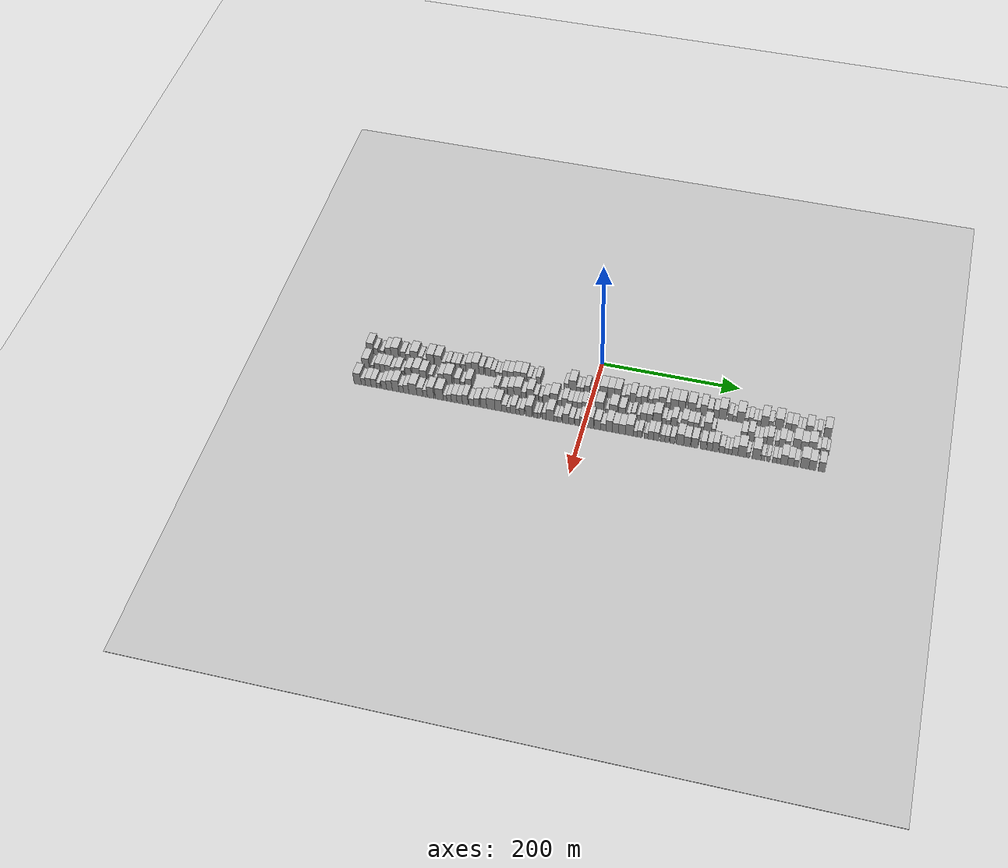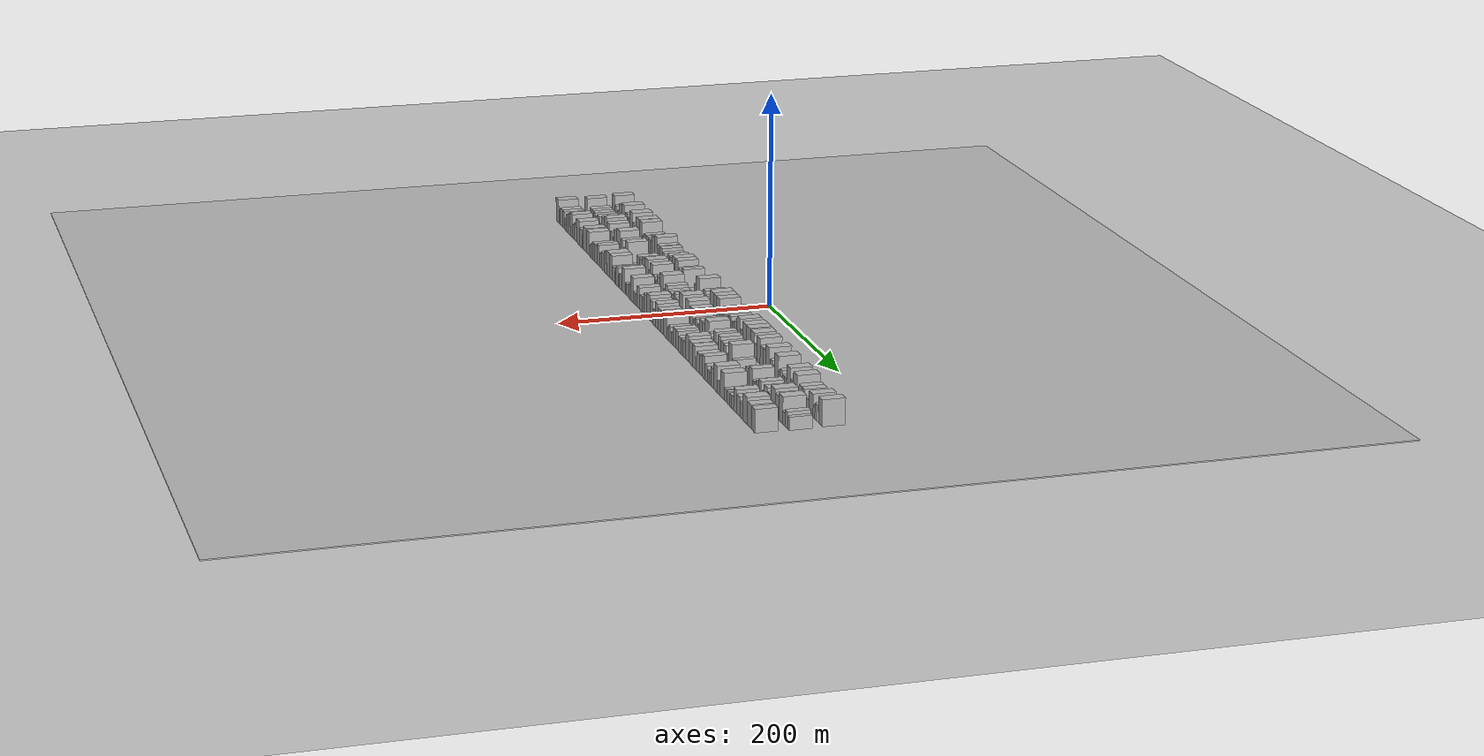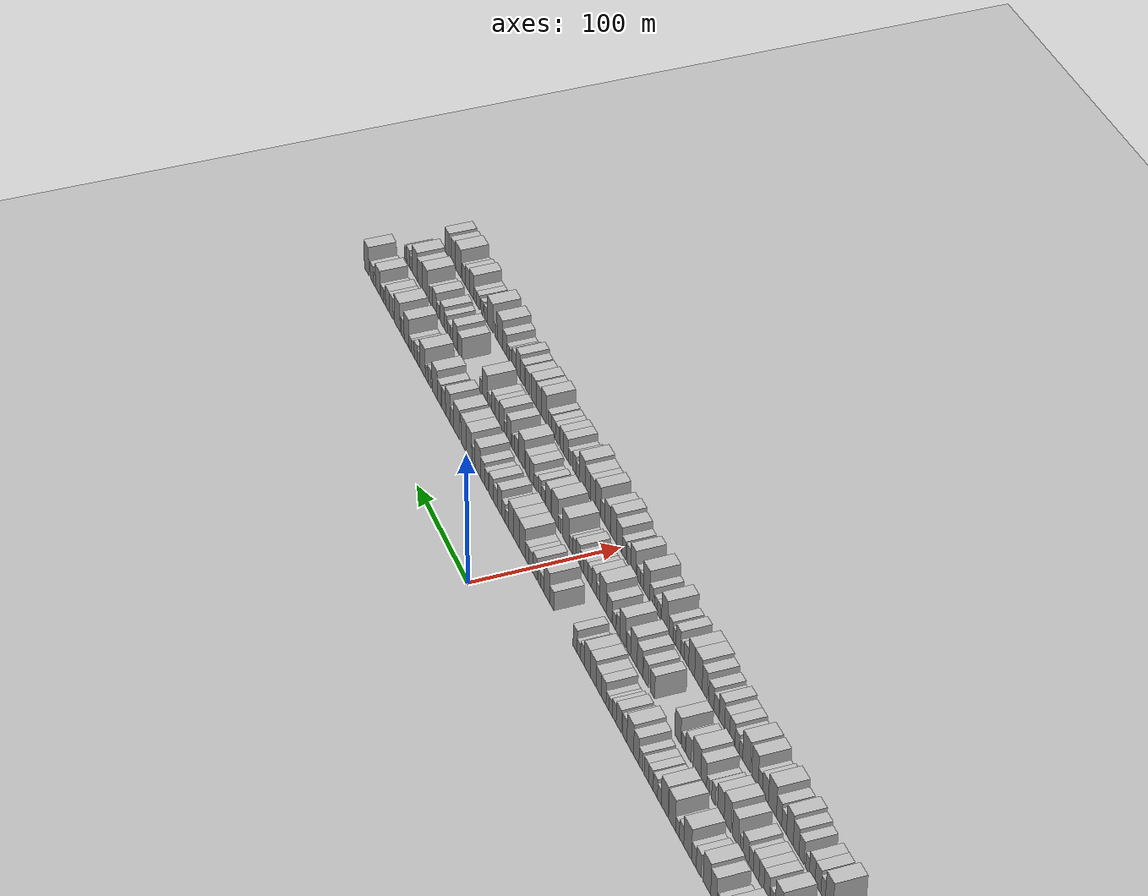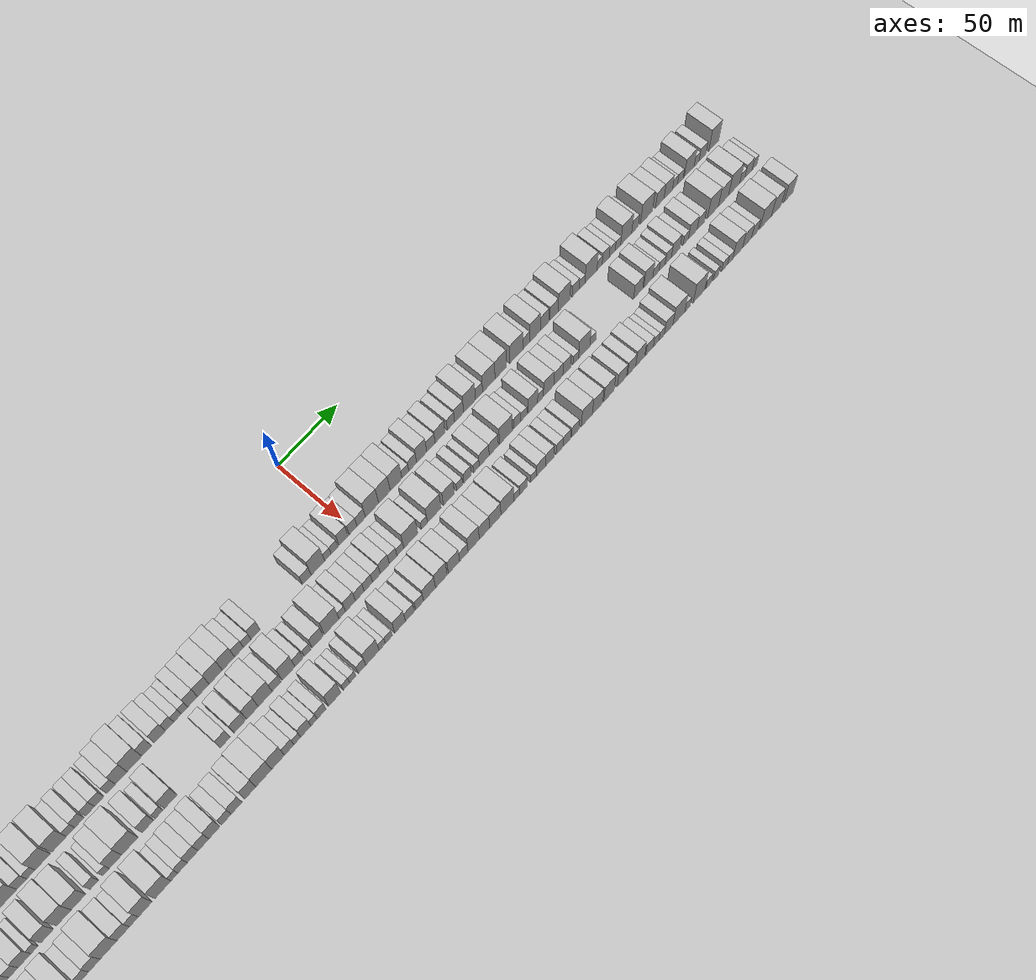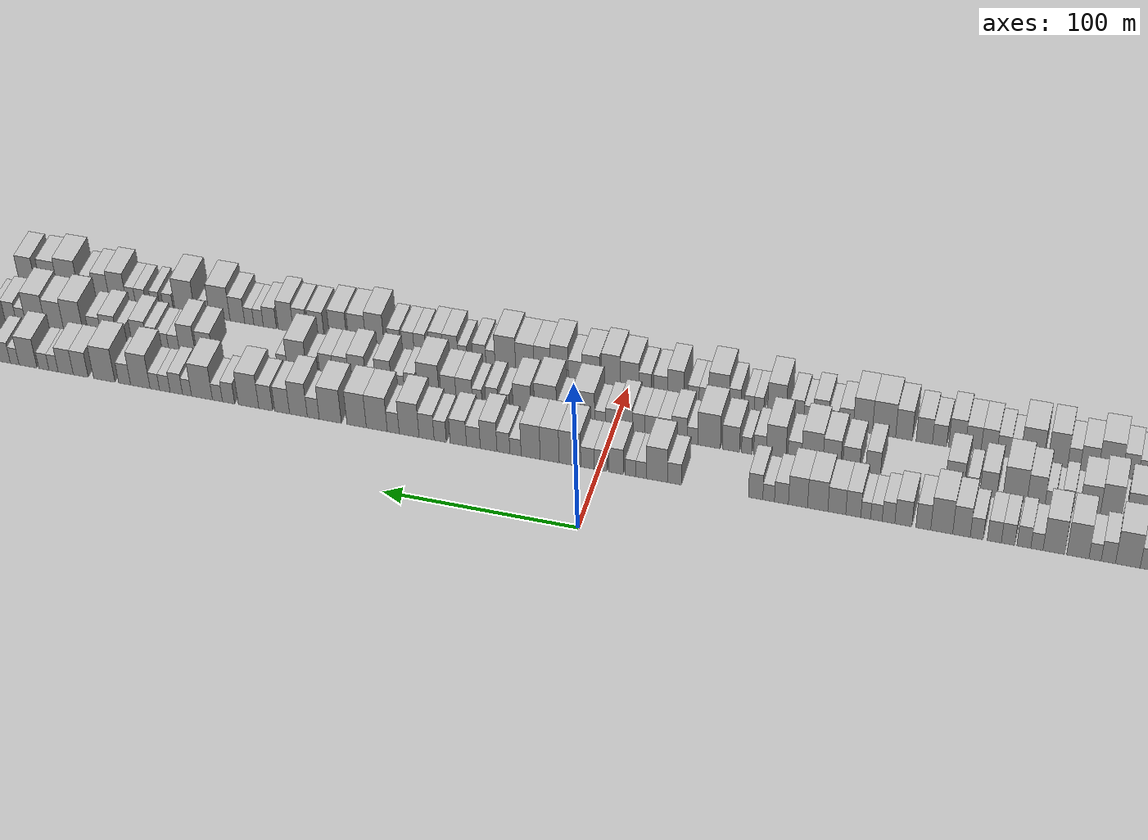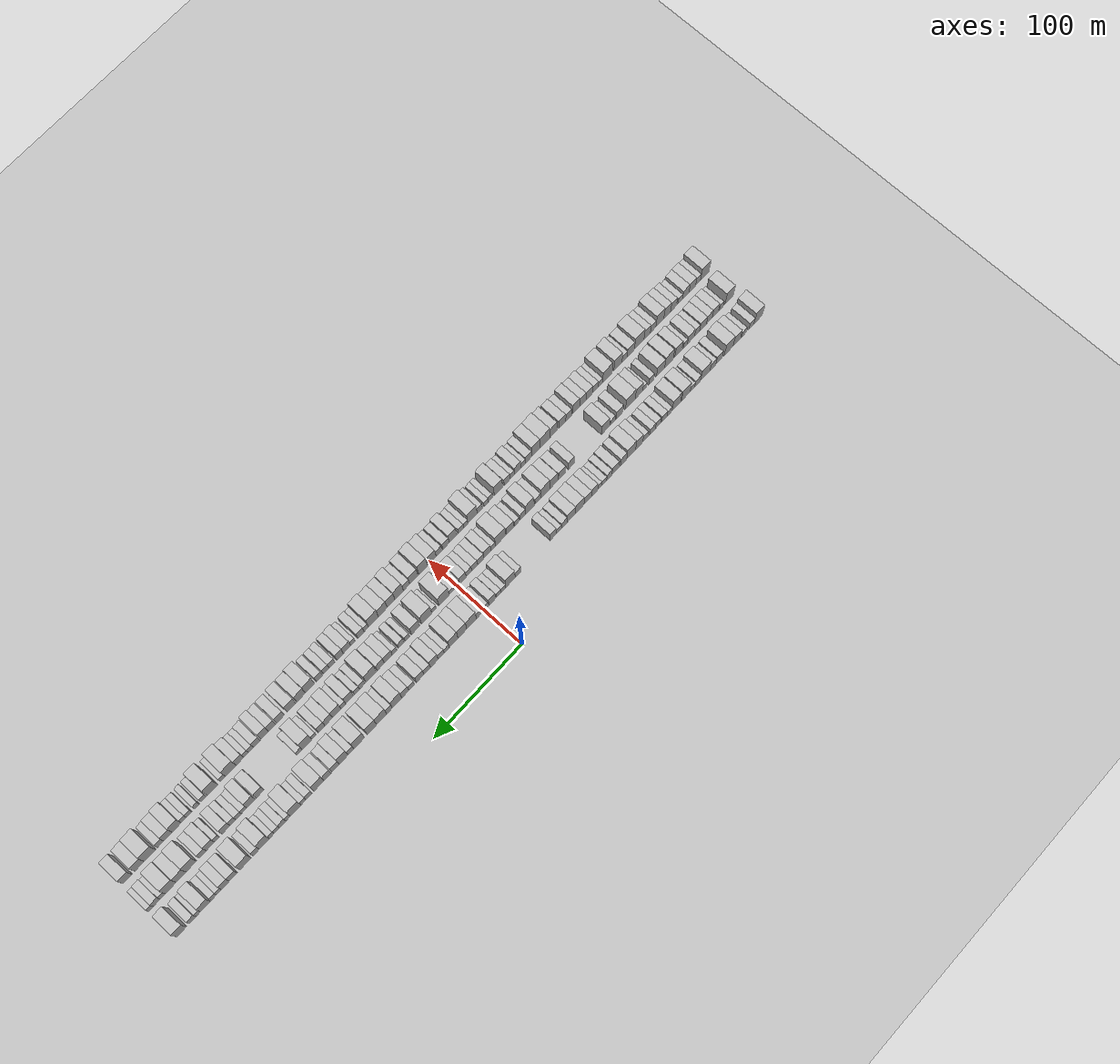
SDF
<?xml version="1.0" encoding="utf-8"?>

<sdf version="1.6">

   <world name="default">

      <gui fullscreen="0">

         <camera name="user_camera">

            <pose>-15 0 4.57585 0 0 0</pose>

            <view_controller>orbit</view_controller>

         </camera>

      </gui>

      <scene>

         <sky>

           <clouds>

             <speed>12</speed>

           </clouds>

         </sky>

         <ambient>0.4 0.4 0.4 1</ambient>

         <background>0.7 0.7 0.7 1</background>

         <shadows>1</shadows>

      </scene>

      <gravity>0 0 -9.8066</gravity>

      <magnetic_field>6e-06 2.3e-05 -4.2e-05</magnetic_field>

      <physics default="0" name="default_physics" type="ode">

         <ode>

            <solver>

               <type>quick</type>

               <iters>10</iters>

               <sor>1.0</sor>

               <use_dynamic_moi_rescaling>0</use_dynamic_moi_rescaling>

            </solver>

            <constraints>

               <cfm>0</cfm>

               <erp>0.2</erp>

               <contact_max_correcting_vel>100</contact_max_correcting_vel>

               <contact_surface_layer>0.001</contact_surface_layer>

            </constraints>

         </ode>

         <max_step_size>0.004</max_step_size>

         <real_time_factor>1</real_time_factor>

         <real_time_update_rate>250</real_time_update_rate>

      </physics>

      <light name="sun" type="directional">

         <cast_shadows>1</cast_shadows>

         <pose>0 0 10 0 0 0</pose>

         <diffuse>0.8 0.8 0.8 1</diffuse>

         <specular>0.2 0.2 0.2 1</specular>

         <attenuation>

            <range>1000</range>

            <constant>0.9</constant>

            <linear>0.01</linear>

            <quadratic>0.001</quadratic>

         </attenuation>

         <direction>-0.5 0.1 -0.9</direction>

      </light>

      <include>

         <name>ground_plane_1</name>

         <uri>model://HANNAS_ground_plane</uri>

         <pose>0 0 0  0 0 0</pose>

      </include>

      <include>

         <name>ground_plane_2</name>

         <uri>model://HANNAS_ground_plane</uri>

         <pose>100 0 0  0 0 0</pose>

      </include>

      <model name="building_1">

         <static>1</static>

         <pose frame="">50.0000 -330.7542 0 0.000000 0.000000 0.000000</pose>

         <link name="link">

            <pose frame="">0 0 12.00 0 0 0</pose>

            <collision name="collision">

               <geometry>

                  <box>

                     <size>20.0000 10.4916 24.0000</size>

                  </box>

               </geometry>

               <max_contacts>10</max_contacts>

               <surface>

                  <contact>

                     <ode/>

                  </contact>

                  <bounce/>

                  <friction>

                     <torsional>

                        <ode/>

                     </torsional>

                     <ode/>

                  </friction>

               </surface>

            </collision>

            <visual name="visual">

               <cast_shadows>0</cast_shadows>

               <geometry>

                  <box>

                     <size>20.0000 10.4916 24.0000</size>

                  </box>

               </geometry>

               <material>

                  <script>

                     <uri>model://HANNAS_wall/materials/scripts</uri>

                     <uri>model://HANNAS_wall/materials/textures</uri>

                     <name>vrc/HANNAS_wall</name>

                  </script>

               </material>

            </visual>

            <self_collide>0</self_collide>

            <enable_wind>0</enable_wind>

            <kinematic>0</kinematic>

         </link>

      </model>

      <model name="building_2">

         <static>1</static>

         <pose frame="">50.0000 -322.2304 0 0.000000 0.000000 0.000000</pose>

         <link name="link">

            <pose frame="">0 0 7.50 0 0 0</pose>

            <collision name="collision">

               <geometry>

                  <box>

                     <size>20.0000 6.5560 15.0000</size>

                  </box>

               </geometry>

               <max_contacts>10</max_contacts>

               <surface>

                  <contact>

                     <ode/>

                  </contact>

                  <bounce/>

                  <friction>

                     <torsional>

                        <ode/>

                     </torsional>

                     <ode/>

                  </friction>

               </surface>

            </collision>

            <visual name="visual">

               <cast_shadows>0</cast_shadows>

               <geometry>

                  <box>

                     <size>20.0000 6.5560 15.0000</size>

                  </box>

               </geometry>

               <material>

                  <script>

                     <uri>model://HANNAS_wall/materials/scripts</uri>

                     <uri>model://HANNAS_wall/materials/textures</uri>

                     <name>vrc/HANNAS_wall</name>

                  </script>

               </material>

            </visual>

            <self_collide>0</self_collide>

            <enable_wind>0</enable_wind>

            <kinematic>0</kinematic>

         </link>

      </model>

      <model name="building_3">

         <static>1</static>

         <pose frame="">50.0000 -313.0369 0 0.000000 0.000000 0.000000</pose>

         <link name="link">

            <pose frame="">0 0 6.00 0 0 0</pose>

            <collision name="collision">

               <geometry>

                  <box>

                     <size>20.0000 5.8309 12.0000</size>

                  </box>

               </geometry>

               <max_contacts>10</max_contacts>

               <surface>

                  <contact>

                     <ode/>

                  </contact>

                  <bounce/>

                  <friction>

                     <torsional>

                        <ode/>

                     </torsional>

                     <ode/>

                  </friction>

               </surface>

            </collision>

            <visual name="visual">

               <cast_shadows>0</cast_shadows>

               <geometry>

                  <box>

                     <size>20.0000 5.8309 12.0000</size>

                  </box>

               </geometry>

               <material>

                  <script>

                     <uri>model://HANNAS_wall/materials/scripts</uri>

                     <uri>model://HANNAS_wall/materials/textures</uri>

                     <name>vrc/HANNAS_wall</name>

                  </script>

               </material>

            </visual>

            <self_collide>0</self_collide>

            <enable_wind>0</enable_wind>

            <kinematic>0</kinematic>

         </link>

      </model>

      <model name="building_4">

         <static>1</static>

         <pose frame="">50.0000 -303.6895 0 0.000000 0.000000 0.000000</pose>

         <link name="link">

            <pose frame="">0 0 10.50 0 0 0</pose>

            <collision name="collision">

               <geometry>

                  <box>

                     <size>20.0000 8.8640 21.0000</size>

                  </box>

               </geometry>

               <max_contacts>10</max_contacts>

               <surface>

                  <contact>

                     <ode/>

                  </contact>

                  <bounce/>

                  <friction>

                     <torsional>

                        <ode/>

                     </torsional>

                     <ode/>

                  </friction>

               </surface>

            </collision>

            <visual name="visual">

               <cast_shadows>0</cast_shadows>

               <geometry>

                  <box>

                     <size>20.0000 8.8640 21.0000</size>

                  </box>

               </geometry>

               <material>

                  <script>

                     <uri>model://HANNAS_wall/materials/scripts</uri>

                     <uri>model://HANNAS_wall/materials/textures</uri>

                     <name>vrc/HANNAS_wall</name>

                  </script>

               </material>

            </visual>

            <self_collide>0</self_collide>

            <enable_wind>0</enable_wind>

            <kinematic>0</kinematic>

         </link>

      </model>

      <model name="building_5">

         <static>1</static>

         <pose frame="">50.0000 -293.6580 0 0.000000 0.000000 0.000000</pose>

         <link name="link">

            <pose frame="">0 0 12.00 0 0 0</pose>

            <collision name="collision">

               <geometry>

                  <box>

                     <size>20.0000 11.1990 24.0000</size>

                  </box>

               </geometry>

               <max_contacts>10</max_contacts>

               <surface>

                  <contact>

                     <ode/>

                  </contact>

                  <bounce/>

                  <friction>

                     <torsional>

                        <ode/>

                     </torsional>

                     <ode/>

                  </friction>

               </surface>

            </collision>

            <visual name="visual">

               <cast_shadows>0</cast_shadows>

               <geometry>

                  <box>

                     <size>20.0000 11.1990 24.0000</size>

                  </box>

               </geometry>

               <material>

                  <script>

                     <uri>model://HANNAS_wall/materials/scripts</uri>

                     <uri>model://HANNAS_wall/materials/textures</uri>

                     <name>vrc/HANNAS_wall</name>

                  </script>

               </material>

            </visual>

            <self_collide>0</self_collide>

            <enable_wind>0</enable_wind>

            <kinematic>0</kinematic>

         </link>

      </model>

      <model name="building_6">

         <static>1</static>

         <pose frame="">50.0000 -281.2292 0 0.000000 0.000000 0.000000</pose>

         <link name="link">

            <pose frame="">0 0 9.00 0 0 0</pose>

            <collision name="collision">

               <geometry>

                  <box>

                     <size>20.0000 7.6587 18.0000</size>

                  </box>

               </geometry>

               <max_contacts>10</max_contacts>

               <surface>

                  <contact>

                     <ode/>

                  </contact>

                  <bounce/>

                  <friction>

                     <torsional>

                        <ode/>

                     </torsional>

                     <ode/>

                  </friction>

               </surface>

            </collision>

            <visual name="visual">

               <cast_shadows>0</cast_shadows>

               <geometry>

                  <box>

                     <size>20.0000 7.6587 18.0000</size>

                  </box>

               </geometry>

               <material>

                  <script>

                     <uri>model://HANNAS_wall/materials/scripts</uri>

                     <uri>model://HANNAS_wall/materials/textures</uri>

                     <name>vrc/HANNAS_wall</name>

                  </script>

               </material>

            </visual>

            <self_collide>0</self_collide>

            <enable_wind>0</enable_wind>

            <kinematic>0</kinematic>

         </link>

      </model>

      <model name="building_7">

         <static>1</static>

         <pose frame="">50.0000 -273.8383 0 0.000000 0.000000 0.000000</pose>

         <link name="link">

            <pose frame="">0 0 7.50 0 0 0</pose>

            <collision name="collision">

               <geometry>

                  <box>

                     <size>20.0000 7.1231 15.0000</size>

                  </box>

               </geometry>

               <max_contacts>10</max_contacts>

               <surface>

                  <contact>

                     <ode/>

                  </contact>

                  <bounce/>

                  <friction>

                     <torsional>

                        <ode/>

                     </torsional>

                     <ode/>

                  </friction>

               </surface>

            </collision>

            <visual name="visual">

               <cast_shadows>0</cast_shadows>

               <geometry>

                  <box>

                     <size>20.0000 7.1231 15.0000</size>

                  </box>

               </geometry>

               <material>

                  <script>

                     <uri>model://HANNAS_wall/materials/scripts</uri>

                     <uri>model://HANNAS_wall/materials/textures</uri>

                     <name>vrc/HANNAS_wall</name>

                  </script>

               </material>

            </visual>

            <self_collide>0</self_collide>

            <enable_wind>0</enable_wind>

            <kinematic>0</kinematic>

         </link>

      </model>

      <model name="building_8">

         <static>1</static>

         <pose frame="">50.0000 -264.3221 0 0.000000 0.000000 0.000000</pose>

         <link name="link">

            <pose frame="">0 0 12.00 0 0 0</pose>

            <collision name="collision">

               <geometry>

                  <box>

                     <size>20.0000 11.9093 24.0000</size>

                  </box>

               </geometry>

               <max_contacts>10</max_contacts>

               <surface>

                  <contact>

                     <ode/>

                  </contact>

                  <bounce/>

                  <friction>

                     <torsional>

                        <ode/>

                     </torsional>

                     <ode/>

                  </friction>

               </surface>

            </collision>

            <visual name="visual">

               <cast_shadows>0</cast_shadows>

               <geometry>

                  <box>

                     <size>20.0000 11.9093 24.0000</size>

                  </box>

               </geometry>

               <material>

                  <script>

                     <uri>model://HANNAS_wall/materials/scripts</uri>

                     <uri>model://HANNAS_wall/materials/textures</uri>

                     <name>vrc/HANNAS_wall</name>

                  </script>

               </material>

            </visual>

            <self_collide>0</self_collide>

            <enable_wind>0</enable_wind>

            <kinematic>0</kinematic>

         </link>

      </model>

      <model name="building_9">

         <static>1</static>

         <pose frame="">50.0000 -254.9074 0 0.000000 0.000000 0.000000</pose>

         <link name="link">

            <pose frame="">0 0 7.50 0 0 0</pose>

            <collision name="collision">

               <geometry>

                  <box>

                     <size>20.0000 6.9201 15.0000</size>

                  </box>

               </geometry>

               <max_contacts>10</max_contacts>

               <surface>

                  <contact>

                     <ode/>

                  </contact>

                  <bounce/>

                  <friction>

                     <torsional>

                        <ode/>

                     </torsional>

                     <ode/>

                  </friction>

               </surface>

            </collision>

            <visual name="visual">

               <cast_shadows>0</cast_shadows>

               <geometry>

                  <box>

                     <size>20.0000 6.9201 15.0000</size>

                  </box>

               </geometry>

               <material>

                  <script>

                     <uri>model://HANNAS_wall/materials/scripts</uri>

                     <uri>model://HANNAS_wall/materials/textures</uri>

                     <name>vrc/HANNAS_wall</name>

                  </script>

               </material>

            </visual>

            <self_collide>0</self_collide>

            <enable_wind>0</enable_wind>

            <kinematic>0</kinematic>

         </link>

      </model>

      <model name="building_10">

         <static>1</static>

         <pose frame="">50.0000 -248.4797 0 0.000000 0.000000 0.000000</pose>

         <link name="link">

            <pose frame="">0 0 6.00 0 0 0</pose>

            <collision name="collision">

               <geometry>

                  <box>

                     <size>20.0000 5.9353 12.0000</size>

                  </box>

               </geometry>

               <max_contacts>10</max_contacts>

               <surface>

                  <contact>

                     <ode/>

                  </contact>

                  <bounce/>

                  <friction>

                     <torsional>

                        <ode/>

                     </torsional>

                     <ode/>

                  </friction>

               </surface>

            </collision>

            <visual name="visual">

               <cast_shadows>0</cast_shadows>

               <geometry>

                  <box>

                     <size>20.0000 5.9353 12.0000</size>

                  </box>

               </geometry>

               <material>

                  <script>

                     <uri>model://HANNAS_wall/materials/scripts</uri>

                     <uri>model://HANNAS_wall/materials/textures</uri>

                     <name>vrc/HANNAS_wall</name>

                  </script>

               </material>

            </visual>

            <self_collide>0</self_collide>

            <enable_wind>0</enable_wind>

            <kinematic>0</kinematic>

         </link>

      </model>

      <model name="building_11">

         <static>1</static>

         <pose frame="">50.0000 -240.1298 0 0.000000 0.000000 0.000000</pose>

         <link name="link">

            <pose frame="">0 0 12.00 0 0 0</pose>

            <collision name="collision">

               <geometry>

                  <box>

                     <size>20.0000 10.7646 24.0000</size>

                  </box>

               </geometry>

               <max_contacts>10</max_contacts>

               <surface>

                  <contact>

                     <ode/>

                  </contact>

                  <bounce/>

                  <friction>

                     <torsional>

                        <ode/>

                     </torsional>

                     <ode/>

                  </friction>

               </surface>

            </collision>

            <visual name="visual">

               <cast_shadows>0</cast_shadows>

               <geometry>

                  <box>

                     <size>20.0000 10.7646 24.0000</size>

                  </box>

               </geometry>

               <material>

                  <script>

                     <uri>model://HANNAS_wall/materials/scripts</uri>

                     <uri>model://HANNAS_wall/materials/textures</uri>

                     <name>vrc/HANNAS_wall</name>

                  </script>

               </material>

            </visual>

            <self_collide>0</self_collide>

            <enable_wind>0</enable_wind>

            <kinematic>0</kinematic>

         </link>

      </model>

      <model name="building_12">

         <static>1</static>

         <pose frame="">50.0000 -228.4766 0 0.000000 0.000000 0.000000</pose>

         <link name="link">

            <pose frame="">0 0 12.00 0 0 0</pose>

            <collision name="collision">

               <geometry>

                  <box>

                     <size>20.0000 10.5418 24.0000</size>

                  </box>

               </geometry>

               <max_contacts>10</max_contacts>

               <surface>

                  <contact>

                     <ode/>

                  </contact>

                  <bounce/>

                  <friction>

                     <torsional>

                        <ode/>

                     </torsional>

                     <ode/>

                  </friction>

               </surface>

            </collision>

            <visual name="visual">

               <cast_shadows>0</cast_shadows>

               <geometry>

                  <box>

                     <size>20.0000 10.5418 24.0000</size>

                  </box>

               </geometry>

               <material>

                  <script>

                     <uri>model://HANNAS_wall/materials/scripts</uri>

                     <uri>model://HANNAS_wall/materials/textures</uri>

                     <name>vrc/HANNAS_wall</name>

                  </script>

               </material>

            </visual>

            <self_collide>0</self_collide>

            <enable_wind>0</enable_wind>

            <kinematic>0</kinematic>

         </link>

      </model>

      <model name="building_13">

         <static>1</static>

         <pose frame="">50.0000 -220.2159 0 0.000000 0.000000 0.000000</pose>

         <link name="link">

            <pose frame="">0 0 6.00 0 0 0</pose>

            <collision name="collision">

               <geometry>

                  <box>

                     <size>20.0000 5.9795 12.0000</size>

                  </box>

               </geometry>

               <max_contacts>10</max_contacts>

               <surface>

                  <contact>

                     <ode/>

                  </contact>

                  <bounce/>

                  <friction>

                     <torsional>

                        <ode/>

                     </torsional>

                     <ode/>

                  </friction>

               </surface>

            </collision>

            <visual name="visual">

               <cast_shadows>0</cast_shadows>

               <geometry>

                  <box>

                     <size>20.0000 5.9795 12.0000</size>

                  </box>

               </geometry>

               <material>

                  <script>

                     <uri>model://HANNAS_wall/materials/scripts</uri>

                     <uri>model://HANNAS_wall/materials/textures</uri>

                     <name>vrc/HANNAS_wall</name>

                  </script>

               </material>

            </visual>

            <self_collide>0</self_collide>

            <enable_wind>0</enable_wind>

            <kinematic>0</kinematic>

         </link>

      </model>

      <model name="building_14">

         <static>1</static>

         <pose frame="">50.0000 -213.8273 0 0.000000 0.000000 0.000000</pose>

         <link name="link">

            <pose frame="">0 0 7.50 0 0 0</pose>

            <collision name="collision">

               <geometry>

                  <box>

                     <size>20.0000 6.7977 15.0000</size>

                  </box>

               </geometry>

               <max_contacts>10</max_contacts>

               <surface>

                  <contact>

                     <ode/>

                  </contact>

                  <bounce/>

                  <friction>

                     <torsional>

                        <ode/>

                     </torsional>

                     <ode/>

                  </friction>

               </surface>

            </collision>

            <visual name="visual">

               <cast_shadows>0</cast_shadows>

               <geometry>

                  <box>

                     <size>20.0000 6.7977 15.0000</size>

                  </box>

               </geometry>

               <material>

                  <script>

                     <uri>model://HANNAS_wall/materials/scripts</uri>

                     <uri>model://HANNAS_wall/materials/textures</uri>

                     <name>vrc/HANNAS_wall</name>

                  </script>

               </material>

            </visual>

            <self_collide>0</self_collide>

            <enable_wind>0</enable_wind>

            <kinematic>0</kinematic>

         </link>

      </model>

      <model name="building_15">

         <static>1</static>

         <pose frame="">50.0000 -206.1261 0 0.000000 0.000000 0.000000</pose>

         <link name="link">

            <pose frame="">0 0 7.50 0 0 0</pose>

            <collision name="collision">

               <geometry>

                  <box>

                     <size>20.0000 6.6046 15.0000</size>

                  </box>

               </geometry>

               <max_contacts>10</max_contacts>

               <surface>

                  <contact>

                     <ode/>

                  </contact>

                  <bounce/>

                  <friction>

                     <torsional>

                        <ode/>

                     </torsional>

                     <ode/>

                  </friction>

               </surface>

            </collision>

            <visual name="visual">

               <cast_shadows>0</cast_shadows>

               <geometry>

                  <box>

                     <size>20.0000 6.6046 15.0000</size>

                  </box>

               </geometry>

               <material>

                  <script>

                     <uri>model://HANNAS_wall/materials/scripts</uri>

                     <uri>model://HANNAS_wall/materials/textures</uri>

                     <name>vrc/HANNAS_wall</name>

                  </script>

               </material>

            </visual>

            <self_collide>0</self_collide>

            <enable_wind>0</enable_wind>

            <kinematic>0</kinematic>

         </link>

      </model>

      <model name="building_16">

         <static>1</static>

         <pose frame="">50.0000 -199.3701 0 0.000000 0.000000 0.000000</pose>

         <link name="link">

            <pose frame="">0 0 7.50 0 0 0</pose>

            <collision name="collision">

               <geometry>

                  <box>

                     <size>20.0000 6.9075 15.0000</size>

                  </box>

               </geometry>

               <max_contacts>10</max_contacts>

               <surface>

                  <contact>

                     <ode/>

                  </contact>

                  <bounce/>

                  <friction>

                     <torsional>

                        <ode/>

                     </torsional>

                     <ode/>

                  </friction>

               </surface>

            </collision>

            <visual name="visual">

               <cast_shadows>0</cast_shadows>

               <geometry>

                  <box>

                     <size>20.0000 6.9075 15.0000</size>

                  </box>

               </geometry>

               <material>

                  <script>

                     <uri>model://HANNAS_wall/materials/scripts</uri>

                     <uri>model://HANNAS_wall/materials/textures</uri>

                     <name>vrc/HANNAS_wall</name>

                  </script>

               </material>

            </visual>

            <self_collide>0</self_collide>

            <enable_wind>0</enable_wind>

            <kinematic>0</kinematic>

         </link>

      </model>

      <model name="building_17">

         <static>1</static>

         <pose frame="">50.0000 -190.7344 0 0.000000 0.000000 0.000000</pose>

         <link name="link">

            <pose frame="">0 0 7.50 0 0 0</pose>

            <collision name="collision">

               <geometry>

                  <box>

                     <size>20.0000 6.3638 15.0000</size>

                  </box>

               </geometry>

               <max_contacts>10</max_contacts>

               <surface>

                  <contact>

                     <ode/>

                  </contact>

                  <bounce/>

                  <friction>

                     <torsional>

                        <ode/>

                     </torsional>

                     <ode/>

                  </friction>

               </surface>

            </collision>

            <visual name="visual">

               <cast_shadows>0</cast_shadows>

               <geometry>

                  <box>

                     <size>20.0000 6.3638 15.0000</size>

                  </box>

               </geometry>

               <material>

                  <script>

                     <uri>model://HANNAS_wall/materials/scripts</uri>

                     <uri>model://HANNAS_wall/materials/textures</uri>

                     <name>vrc/HANNAS_wall</name>

                  </script>

               </material>

            </visual>

            <self_collide>0</self_collide>

            <enable_wind>0</enable_wind>

            <kinematic>0</kinematic>

         </link>

      </model>

      <model name="building_18">

         <static>1</static>

         <pose frame="">50.0000 -183.2185 0 0.000000 0.000000 0.000000</pose>

         <link name="link">

            <pose frame="">0 0 10.50 0 0 0</pose>

            <collision name="collision">

               <geometry>

                  <box>

                     <size>20.0000 8.6681 21.0000</size>

                  </box>

               </geometry>

               <max_contacts>10</max_contacts>

               <surface>

                  <contact>

                     <ode/>

                  </contact>

                  <bounce/>

                  <friction>

                     <torsional>

                        <ode/>

                     </torsional>

                     <ode/>

                  </friction>

               </surface>

            </collision>

            <visual name="visual">

               <cast_shadows>0</cast_shadows>

               <geometry>

                  <box>

                     <size>20.0000 8.6681 21.0000</size>

                  </box>

               </geometry>

               <material>

                  <script>

                     <uri>model://HANNAS_wall/materials/scripts</uri>

                     <uri>model://HANNAS_wall/materials/textures</uri>

                     <name>vrc/HANNAS_wall</name>

                  </script>

               </material>

            </visual>

            <self_collide>0</self_collide>

            <enable_wind>0</enable_wind>

            <kinematic>0</kinematic>

         </link>

      </model>

      <model name="building_19">

         <static>1</static>

         <pose frame="">50.0000 -173.4385 0 0.000000 0.000000 0.000000</pose>

         <link name="link">

            <pose frame="">0 0 12.00 0 0 0</pose>

            <collision name="collision">

               <geometry>

                  <box>

                     <size>20.0000 10.8919 24.0000</size>

                  </box>

               </geometry>

               <max_contacts>10</max_contacts>

               <surface>

                  <contact>

                     <ode/>

                  </contact>

                  <bounce/>

                  <friction>

                     <torsional>

                        <ode/>

                     </torsional>

                     <ode/>

                  </friction>

               </surface>

            </collision>

            <visual name="visual">

               <cast_shadows>0</cast_shadows>

               <geometry>

                  <box>

                     <size>20.0000 10.8919 24.0000</size>

                  </box>

               </geometry>

               <material>

                  <script>

                     <uri>model://HANNAS_wall/materials/scripts</uri>

                     <uri>model://HANNAS_wall/materials/textures</uri>

                     <name>vrc/HANNAS_wall</name>

                  </script>

               </material>

            </visual>

            <self_collide>0</self_collide>

            <enable_wind>0</enable_wind>

            <kinematic>0</kinematic>

         </link>

      </model>

      <model name="building_20">

         <static>1</static>

         <pose frame="">50.0000 -164.3365 0 0.000000 0.000000 0.000000</pose>

         <link name="link">

            <pose frame="">0 0 9.00 0 0 0</pose>

            <collision name="collision">

               <geometry>

                  <box>

                     <size>20.0000 7.3120 18.0000</size>

                  </box>

               </geometry>

               <max_contacts>10</max_contacts>

               <surface>

                  <contact>

                     <ode/>

                  </contact>

                  <bounce/>

                  <friction>

                     <torsional>

                        <ode/>

                     </torsional>

                     <ode/>

                  </friction>

               </surface>

            </collision>

            <visual name="visual">

               <cast_shadows>0</cast_shadows>

               <geometry>

                  <box>

                     <size>20.0000 7.3120 18.0000</size>

                  </box>

               </geometry>

               <material>

                  <script>

                     <uri>model://HANNAS_wall/materials/scripts</uri>

                     <uri>model://HANNAS_wall/materials/textures</uri>

                     <name>vrc/HANNAS_wall</name>

                  </script>

               </material>

            </visual>

            <self_collide>0</self_collide>

            <enable_wind>0</enable_wind>

            <kinematic>0</kinematic>

         </link>

      </model>

      <model name="building_21">

         <static>1</static>

         <pose frame="">50.0000 -154.4508 0 0.000000 0.000000 0.000000</pose>

         <link name="link">

            <pose frame="">0 0 9.00 0 0 0</pose>

            <collision name="collision">

               <geometry>

                  <box>

                     <size>20.0000 8.4593 18.0000</size>

                  </box>

               </geometry>

               <max_contacts>10</max_contacts>

               <surface>

                  <contact>

                     <ode/>

                  </contact>

                  <bounce/>

                  <friction>

                     <torsional>

                        <ode/>

                     </torsional>

                     <ode/>

                  </friction>

               </surface>

            </collision>

            <visual name="visual">

               <cast_shadows>0</cast_shadows>

               <geometry>

                  <box>

                     <size>20.0000 8.4593 18.0000</size>

                  </box>

               </geometry>

               <material>

                  <script>

                     <uri>model://HANNAS_wall/materials/scripts</uri>

                     <uri>model://HANNAS_wall/materials/textures</uri>

                     <name>vrc/HANNAS_wall</name>

                  </script>

               </material>

            </visual>

            <self_collide>0</self_collide>

            <enable_wind>0</enable_wind>

            <kinematic>0</kinematic>

         </link>

      </model>

      <model name="building_22">

         <static>1</static>

         <pose frame="">50.0000 -147.0573 0 0.000000 0.000000 0.000000</pose>

         <link name="link">

            <pose frame="">0 0 7.50 0 0 0</pose>

            <collision name="collision">

               <geometry>

                  <box>

                     <size>20.0000 6.3278 15.0000</size>

                  </box>

               </geometry>

               <max_contacts>10</max_contacts>

               <surface>

                  <contact>

                     <ode/>

                  </contact>

                  <bounce/>

                  <friction>

                     <torsional>

                        <ode/>

                     </torsional>

                     <ode/>

                  </friction>

               </surface>

            </collision>

            <visual name="visual">

               <cast_shadows>0</cast_shadows>

               <geometry>

                  <box>

                     <size>20.0000 6.3278 15.0000</size>

                  </box>

               </geometry>

               <material>

                  <script>

                     <uri>model://HANNAS_wall/materials/scripts</uri>

                     <uri>model://HANNAS_wall/materials/textures</uri>

                     <name>vrc/HANNAS_wall</name>

                  </script>

               </material>

            </visual>

            <self_collide>0</self_collide>

            <enable_wind>0</enable_wind>

            <kinematic>0</kinematic>

         </link>

      </model>

      <model name="building_23">

         <static>1</static>

         <pose frame="">50.0000 -141.0131 0 0.000000 0.000000 0.000000</pose>

         <link name="link">

            <pose frame="">0 0 6.00 0 0 0</pose>

            <collision name="collision">

               <geometry>

                  <box>

                     <size>20.0000 5.7605 12.0000</size>

                  </box>

               </geometry>

               <max_contacts>10</max_contacts>

               <surface>

                  <contact>

                     <ode/>

                  </contact>

                  <bounce/>

                  <friction>

                     <torsional>

                        <ode/>

                     </torsional>

                     <ode/>

                  </friction>

               </surface>

            </collision>

            <visual name="visual">

               <cast_shadows>0</cast_shadows>

               <geometry>

                  <box>

                     <size>20.0000 5.7605 12.0000</size>

                  </box>

               </geometry>

               <material>

                  <script>

                     <uri>model://HANNAS_wall/materials/scripts</uri>

                     <uri>model://HANNAS_wall/materials/textures</uri>

                     <name>vrc/HANNAS_wall</name>

                  </script>

               </material>

            </visual>

            <self_collide>0</self_collide>

            <enable_wind>0</enable_wind>

            <kinematic>0</kinematic>

         </link>

      </model>

      <model name="building_24">

         <static>1</static>

         <pose frame="">50.0000 -135.6958 0 0.000000 0.000000 0.000000</pose>

         <link name="link">

            <pose frame="">0 0 6.00 0 0 0</pose>

            <collision name="collision">

               <geometry>

                  <box>

                     <size>20.0000 4.8741 12.0000</size>

                  </box>

               </geometry>

               <max_contacts>10</max_contacts>

               <surface>

                  <contact>

                     <ode/>

                  </contact>

                  <bounce/>

                  <friction>

                     <torsional>

                        <ode/>

                     </torsional>

                     <ode/>

                  </friction>

               </surface>

            </collision>

            <visual name="visual">

               <cast_shadows>0</cast_shadows>

               <geometry>

                  <box>

                     <size>20.0000 4.8741 12.0000</size>

                  </box>

               </geometry>

               <material>

                  <script>

                     <uri>model://HANNAS_wall/materials/scripts</uri>

                     <uri>model://HANNAS_wall/materials/textures</uri>

                     <name>vrc/HANNAS_wall</name>

                  </script>

               </material>

            </visual>

            <self_collide>0</self_collide>

            <enable_wind>0</enable_wind>

            <kinematic>0</kinematic>

         </link>

      </model>

      <model name="building_25">

         <static>1</static>

         <pose frame="">50.0000 -129.4872 0 0.000000 0.000000 0.000000</pose>

         <link name="link">

            <pose frame="">0 0 9.00 0 0 0</pose>

            <collision name="collision">

               <geometry>

                  <box>

                     <size>20.0000 7.5432 18.0000</size>

                  </box>

               </geometry>

               <max_contacts>10</max_contacts>

               <surface>

                  <contact>

                     <ode/>

                  </contact>

                  <bounce/>

                  <friction>

                     <torsional>

                        <ode/>

                     </torsional>

                     <ode/>

                  </friction>

               </surface>

            </collision>

            <visual name="visual">

               <cast_shadows>0</cast_shadows>

               <geometry>

                  <box>

                     <size>20.0000 7.5432 18.0000</size>

                  </box>

               </geometry>

               <material>

                  <script>

                     <uri>model://HANNAS_wall/materials/scripts</uri>

                     <uri>model://HANNAS_wall/materials/textures</uri>

                     <name>vrc/HANNAS_wall</name>

                  </script>

               </material>

            </visual>

            <self_collide>0</self_collide>

            <enable_wind>0</enable_wind>

            <kinematic>0</kinematic>

         </link>

      </model>

      <model name="building_26">

         <static>1</static>

         <pose frame="">50.0000 -121.2237 0 0.000000 0.000000 0.000000</pose>

         <link name="link">

            <pose frame="">0 0 9.00 0 0 0</pose>

            <collision name="collision">

               <geometry>

                  <box>

                     <size>20.0000 8.9837 18.0000</size>

                  </box>

               </geometry>

               <max_contacts>10</max_contacts>

               <surface>

                  <contact>

                     <ode/>

                  </contact>

                  <bounce/>

                  <friction>

                     <torsional>

                        <ode/>

                     </torsional>

                     <ode/>

                  </friction>

               </surface>

            </collision>

            <visual name="visual">

               <cast_shadows>0</cast_shadows>

               <geometry>

                  <box>

                     <size>20.0000 8.9837 18.0000</size>

                  </box>

               </geometry>

               <material>

                  <script>

                     <uri>model://HANNAS_wall/materials/scripts</uri>

                     <uri>model://HANNAS_wall/materials/textures</uri>

                     <name>vrc/HANNAS_wall</name>

                  </script>

               </material>

            </visual>

            <self_collide>0</self_collide>

            <enable_wind>0</enable_wind>

            <kinematic>0</kinematic>

         </link>

      </model>

      <model name="building_27">

         <static>1</static>

         <pose frame="">50.0000 -111.6392 0 0.000000 0.000000 0.000000</pose>

         <link name="link">

            <pose frame="">0 0 10.50 0 0 0</pose>

            <collision name="collision">

               <geometry>

                  <box>

                     <size>20.0000 10.1853 21.0000</size>

                  </box>

               </geometry>

               <max_contacts>10</max_contacts>

               <surface>

                  <contact>

                     <ode/>

                  </contact>

                  <bounce/>

                  <friction>

                     <torsional>

                        <ode/>

                     </torsional>

                     <ode/>

                  </friction>

               </surface>

            </collision>

            <visual name="visual">

               <cast_shadows>0</cast_shadows>

               <geometry>

                  <box>

                     <size>20.0000 10.1853 21.0000</size>

                  </box>

               </geometry>

               <material>

                  <script>

                     <uri>model://HANNAS_wall/materials/scripts</uri>

                     <uri>model://HANNAS_wall/materials/textures</uri>

                     <name>vrc/HANNAS_wall</name>

                  </script>

               </material>

            </visual>

            <self_collide>0</self_collide>

            <enable_wind>0</enable_wind>

            <kinematic>0</kinematic>

         </link>

      </model>

      <model name="building_28">

         <static>1</static>

         <pose frame="">50.0000 -101.7299 0 0.000000 0.000000 0.000000</pose>

         <link name="link">

            <pose frame="">0 0 10.50 0 0 0</pose>

            <collision name="collision">

               <geometry>

                  <box>

                     <size>20.0000 9.6334 21.0000</size>

                  </box>

               </geometry>

               <max_contacts>10</max_contacts>

               <surface>

                  <contact>

                     <ode/>

                  </contact>

                  <bounce/>

                  <friction>

                     <torsional>

                        <ode/>

                     </torsional>

                     <ode/>

                  </friction>

               </surface>

            </collision>

            <visual name="visual">

               <cast_shadows>0</cast_shadows>

               <geometry>

                  <box>

                     <size>20.0000 9.6334 21.0000</size>

                  </box>

               </geometry>

               <material>

                  <script>

                     <uri>model://HANNAS_wall/materials/scripts</uri>

                     <uri>model://HANNAS_wall/materials/textures</uri>

                     <name>vrc/HANNAS_wall</name>

                  </script>

               </material>

            </visual>

            <self_collide>0</self_collide>

            <enable_wind>0</enable_wind>

            <kinematic>0</kinematic>

         </link>

      </model>

      <model name="building_29">

         <static>1</static>

         <pose frame="">50.0000 -93.3985 0 0.000000 0.000000 0.000000</pose>

         <link name="link">

            <pose frame="">0 0 7.50 0 0 0</pose>

            <collision name="collision">

               <geometry>

                  <box>

                     <size>20.0000 7.0294 15.0000</size>

                  </box>

               </geometry>

               <max_contacts>10</max_contacts>

               <surface>

                  <contact>

                     <ode/>

                  </contact>

                  <bounce/>

                  <friction>

                     <torsional>

                        <ode/>

                     </torsional>

                     <ode/>

                  </friction>

               </surface>

            </collision>

            <visual name="visual">

               <cast_shadows>0</cast_shadows>

               <geometry>

                  <box>

                     <size>20.0000 7.0294 15.0000</size>

                  </box>

               </geometry>

               <material>

                  <script>

                     <uri>model://HANNAS_wall/materials/scripts</uri>

                     <uri>model://HANNAS_wall/materials/textures</uri>

                     <name>vrc/HANNAS_wall</name>

                  </script>

               </material>

            </visual>

            <self_collide>0</self_collide>

            <enable_wind>0</enable_wind>

            <kinematic>0</kinematic>

         </link>

      </model>

      <model name="building_30">

         <static>1</static>

         <pose frame="">50.0000 -86.9318 0 0.000000 0.000000 0.000000</pose>

         <link name="link">

            <pose frame="">0 0 6.00 0 0 0</pose>

            <collision name="collision">

               <geometry>

                  <box>

                     <size>20.0000 5.9041 12.0000</size>

                  </box>

               </geometry>

               <max_contacts>10</max_contacts>

               <surface>

                  <contact>

                     <ode/>

                  </contact>

                  <bounce/>

                  <friction>

                     <torsional>

                        <ode/>

                     </torsional>

                     <ode/>

                  </friction>

               </surface>

            </collision>

            <visual name="visual">

               <cast_shadows>0</cast_shadows>

               <geometry>

                  <box>

                     <size>20.0000 5.9041 12.0000</size>

                  </box>

               </geometry>

               <material>

                  <script>

                     <uri>model://HANNAS_wall/materials/scripts</uri>

                     <uri>model://HANNAS_wall/materials/textures</uri>

                     <name>vrc/HANNAS_wall</name>

                  </script>

               </material>

            </visual>

            <self_collide>0</self_collide>

            <enable_wind>0</enable_wind>

            <kinematic>0</kinematic>

         </link>

      </model>

      <model name="building_31">

         <static>1</static>

         <pose frame="">50.0000 -80.3663 0 0.000000 0.000000 0.000000</pose>

         <link name="link">

            <pose frame="">0 0 9.00 0 0 0</pose>

            <collision name="collision">

               <geometry>

                  <box>

                     <size>20.0000 7.2269 18.0000</size>

                  </box>

               </geometry>

               <max_contacts>10</max_contacts>

               <surface>

                  <contact>

                     <ode/>

                  </contact>

                  <bounce/>

                  <friction>

                     <torsional>

                        <ode/>

                     </torsional>

                     <ode/>

                  </friction>

               </surface>

            </collision>

            <visual name="visual">

               <cast_shadows>0</cast_shadows>

               <geometry>

                  <box>

                     <size>20.0000 7.2269 18.0000</size>

                  </box>

               </geometry>

               <material>

                  <script>

                     <uri>model://HANNAS_wall/materials/scripts</uri>

                     <uri>model://HANNAS_wall/materials/textures</uri>

                     <name>vrc/HANNAS_wall</name>

                  </script>

               </material>

            </visual>

            <self_collide>0</self_collide>

            <enable_wind>0</enable_wind>

            <kinematic>0</kinematic>

         </link>

      </model>

      <model name="building_32">

         <static>1</static>

         <pose frame="">50.0000 -39.1120 0 0.000000 0.000000 0.000000</pose>

         <link name="link">

            <pose frame="">0 0 7.50 0 0 0</pose>

            <collision name="collision">

               <geometry>

                  <box>

                     <size>20.0000 7.0939 15.0000</size>

                  </box>

               </geometry>

               <max_contacts>10</max_contacts>

               <surface>

                  <contact>

                     <ode/>

                  </contact>

                  <bounce/>

                  <friction>

                     <torsional>

                        <ode/>

                     </torsional>

                     <ode/>

                  </friction>

               </surface>

            </collision>

            <visual name="visual">

               <cast_shadows>0</cast_shadows>

               <geometry>

                  <box>

                     <size>20.0000 7.0939 15.0000</size>

                  </box>

               </geometry>

               <material>

                  <script>

                     <uri>model://HANNAS_wall/materials/scripts</uri>

                     <uri>model://HANNAS_wall/materials/textures</uri>

                     <name>vrc/HANNAS_wall</name>

                  </script>

               </material>

            </visual>

            <self_collide>0</self_collide>

            <enable_wind>0</enable_wind>

            <kinematic>0</kinematic>

         </link>

      </model>

      <model name="building_33">

         <static>1</static>

         <pose frame="">50.0000 -30.1010 0 0.000000 0.000000 0.000000</pose>

         <link name="link">

            <pose frame="">0 0 12.00 0 0 0</pose>

            <collision name="collision">

               <geometry>

                  <box>

                     <size>20.0000 10.9281 24.0000</size>

                  </box>

               </geometry>

               <max_contacts>10</max_contacts>

               <surface>

                  <contact>

                     <ode/>

                  </contact>

                  <bounce/>

                  <friction>

                     <torsional>

                        <ode/>

                     </torsional>

                     <ode/>

                  </friction>

               </surface>

            </collision>

            <visual name="visual">

               <cast_shadows>0</cast_shadows>

               <geometry>

                  <box>

                     <size>20.0000 10.9281 24.0000</size>

                  </box>

               </geometry>

               <material>

                  <script>

                     <uri>model://HANNAS_wall/materials/scripts</uri>

                     <uri>model://HANNAS_wall/materials/textures</uri>

                     <name>vrc/HANNAS_wall</name>

                  </script>

               </material>

            </visual>

            <self_collide>0</self_collide>

            <enable_wind>0</enable_wind>

            <kinematic>0</kinematic>

         </link>

      </model>

      <model name="building_34">

         <static>1</static>

         <pose frame="">50.0000 -21.9774 0 0.000000 0.000000 0.000000</pose>

         <link name="link">

            <pose frame="">0 0 6.00 0 0 0</pose>

            <collision name="collision">

               <geometry>

                  <box>

                     <size>20.0000 5.3191 12.0000</size>

                  </box>

               </geometry>

               <max_contacts>10</max_contacts>

               <surface>

                  <contact>

                     <ode/>

                  </contact>

                  <bounce/>

                  <friction>

                     <torsional>

                        <ode/>

                     </torsional>

                     <ode/>

                  </friction>

               </surface>

            </collision>

            <visual name="visual">

               <cast_shadows>0</cast_shadows>

               <geometry>

                  <box>

                     <size>20.0000 5.3191 12.0000</size>

                  </box>

               </geometry>

               <material>

                  <script>

                     <uri>model://HANNAS_wall/materials/scripts</uri>

                     <uri>model://HANNAS_wall/materials/textures</uri>

                     <name>vrc/HANNAS_wall</name>

                  </script>

               </material>

            </visual>

            <self_collide>0</self_collide>

            <enable_wind>0</enable_wind>

            <kinematic>0</kinematic>

         </link>

      </model>

      <model name="building_35">

         <static>1</static>

         <pose frame="">50.0000 -16.5617 0 0.000000 0.000000 0.000000</pose>

         <link name="link">

            <pose frame="">0 0 6.00 0 0 0</pose>

            <collision name="collision">

               <geometry>

                  <box>

                     <size>20.0000 5.5124 12.0000</size>

                  </box>

               </geometry>

               <max_contacts>10</max_contacts>

               <surface>

                  <contact>

                     <ode/>

                  </contact>

                  <bounce/>

                  <friction>

                     <torsional>

                        <ode/>

                     </torsional>

                     <ode/>

                  </friction>

               </surface>

            </collision>

            <visual name="visual">

               <cast_shadows>0</cast_shadows>

               <geometry>

                  <box>

                     <size>20.0000 5.5124 12.0000</size>

                  </box>

               </geometry>

               <material>

                  <script>

                     <uri>model://HANNAS_wall/materials/scripts</uri>

                     <uri>model://HANNAS_wall/materials/textures</uri>

                     <name>vrc/HANNAS_wall</name>

                  </script>

               </material>

            </visual>

            <self_collide>0</self_collide>

            <enable_wind>0</enable_wind>

            <kinematic>0</kinematic>

         </link>

      </model>

      <model name="building_36">

         <static>1</static>

         <pose frame="">50.0000 -9.0830 0 0.000000 0.000000 0.000000</pose>

         <link name="link">

            <pose frame="">0 0 9.00 0 0 0</pose>

            <collision name="collision">

               <geometry>

                  <box>

                     <size>20.0000 7.4450 18.0000</size>

                  </box>

               </geometry>

               <max_contacts>10</max_contacts>

               <surface>

                  <contact>

                     <ode/>

                  </contact>

                  <bounce/>

                  <friction>

                     <torsional>

                        <ode/>

                     </torsional>

                     <ode/>

                  </friction>

               </surface>

            </collision>

            <visual name="visual">

               <cast_shadows>0</cast_shadows>

               <geometry>

                  <box>

                     <size>20.0000 7.4450 18.0000</size>

                  </box>

               </geometry>

               <material>

                  <script>

                     <uri>model://HANNAS_wall/materials/scripts</uri>

                     <uri>model://HANNAS_wall/materials/textures</uri>

                     <name>vrc/HANNAS_wall</name>

                  </script>

               </material>

            </visual>

            <self_collide>0</self_collide>

            <enable_wind>0</enable_wind>

            <kinematic>0</kinematic>

         </link>

      </model>

      <model name="building_37">

         <static>1</static>

         <pose frame="">50.0000 -1.0751 0 0.000000 0.000000 0.000000</pose>

         <link name="link">

            <pose frame="">0 0 7.50 0 0 0</pose>

            <collision name="collision">

               <geometry>

                  <box>

                     <size>20.0000 6.5708 15.0000</size>

                  </box>

               </geometry>

               <max_contacts>10</max_contacts>

               <surface>

                  <contact>

                     <ode/>

                  </contact>

                  <bounce/>

                  <friction>

                     <torsional>

                        <ode/>

                     </torsional>

                     <ode/>

                  </friction>

               </surface>

            </collision>

            <visual name="visual">

               <cast_shadows>0</cast_shadows>

               <geometry>

                  <box>

                     <size>20.0000 6.5708 15.0000</size>

                  </box>

               </geometry>

               <material>

                  <script>

                     <uri>model://HANNAS_wall/materials/scripts</uri>

                     <uri>model://HANNAS_wall/materials/textures</uri>

                     <name>vrc/HANNAS_wall</name>

                  </script>

               </material>

            </visual>

            <self_collide>0</self_collide>

            <enable_wind>0</enable_wind>

            <kinematic>0</kinematic>

         </link>

      </model>

      <model name="building_38">

         <static>1</static>

         <pose frame="">50.0000 5.7067 0 0.000000 0.000000 0.000000</pose>

         <link name="link">

            <pose frame="">0 0 7.50 0 0 0</pose>

            <collision name="collision">

               <geometry>

                  <box>

                     <size>20.0000 6.9927 15.0000</size>

                  </box>

               </geometry>

               <max_contacts>10</max_contacts>

               <surface>

                  <contact>

                     <ode/>

                  </contact>

                  <bounce/>

                  <friction>

                     <torsional>

                        <ode/>

                     </torsional>

                     <ode/>

                  </friction>

               </surface>

            </collision>

            <visual name="visual">

               <cast_shadows>0</cast_shadows>

               <geometry>

                  <box>

                     <size>20.0000 6.9927 15.0000</size>

                  </box>

               </geometry>

               <material>

                  <script>

                     <uri>model://HANNAS_wall/materials/scripts</uri>

                     <uri>model://HANNAS_wall/materials/textures</uri>

                     <name>vrc/HANNAS_wall</name>

                  </script>

               </material>

            </visual>

            <self_collide>0</self_collide>

            <enable_wind>0</enable_wind>

            <kinematic>0</kinematic>

         </link>

      </model>

      <model name="building_39">

         <static>1</static>

         <pose frame="">50.0000 14.8138 0 0.000000 0.000000 0.000000</pose>

         <link name="link">

            <pose frame="">0 0 12.00 0 0 0</pose>

            <collision name="collision">

               <geometry>

                  <box>

                     <size>20.0000 11.2215 24.0000</size>

                  </box>

               </geometry>

               <max_contacts>10</max_contacts>

               <surface>

                  <contact>

                     <ode/>

                  </contact>

                  <bounce/>

                  <friction>

                     <torsional>

                        <ode/>

                     </torsional>

                     <ode/>

                  </friction>

               </surface>

            </collision>

            <visual name="visual">

               <cast_shadows>0</cast_shadows>

               <geometry>

                  <box>

                     <size>20.0000 11.2215 24.0000</size>

                  </box>

               </geometry>

               <material>

                  <script>

                     <uri>model://HANNAS_wall/materials/scripts</uri>

                     <uri>model://HANNAS_wall/materials/textures</uri>

                     <name>vrc/HANNAS_wall</name>

                  </script>

               </material>

            </visual>

            <self_collide>0</self_collide>

            <enable_wind>0</enable_wind>

            <kinematic>0</kinematic>

         </link>

      </model>

      <model name="building_40">

         <static>1</static>

         <pose frame="">50.0000 25.3517 0 0.000000 0.000000 0.000000</pose>

         <link name="link">

            <pose frame="">0 0 12.00 0 0 0</pose>

            <collision name="collision">

               <geometry>

                  <box>

                     <size>20.0000 9.8544 24.0000</size>

                  </box>

               </geometry>

               <max_contacts>10</max_contacts>

               <surface>

                  <contact>

                     <ode/>

                  </contact>

                  <bounce/>

                  <friction>

                     <torsional>

                        <ode/>

                     </torsional>

                     <ode/>

                  </friction>

               </surface>

            </collision>

            <visual name="visual">

               <cast_shadows>0</cast_shadows>

               <geometry>

                  <box>

                     <size>20.0000 9.8544 24.0000</size>

                  </box>

               </geometry>

               <material>

                  <script>

                     <uri>model://HANNAS_wall/materials/scripts</uri>

                     <uri>model://HANNAS_wall/materials/textures</uri>

                     <name>vrc/HANNAS_wall</name>

                  </script>

               </material>

            </visual>

            <self_collide>0</self_collide>

            <enable_wind>0</enable_wind>

            <kinematic>0</kinematic>

         </link>

      </model>

      <model name="building_41">

         <static>1</static>

         <pose frame="">50.0000 35.2717 0 0.000000 0.000000 0.000000</pose>

         <link name="link">

            <pose frame="">0 0 12.00 0 0 0</pose>

            <collision name="collision">

               <geometry>

                  <box>

                     <size>20.0000 9.9855 24.0000</size>

                  </box>

               </geometry>

               <max_contacts>10</max_contacts>

               <surface>

                  <contact>

                     <ode/>

                  </contact>

                  <bounce/>

                  <friction>

                     <torsional>

                        <ode/>

                     </torsional>

                     <ode/>

                  </friction>

               </surface>

            </collision>

            <visual name="visual">

               <cast_shadows>0</cast_shadows>

               <geometry>

                  <box>

                     <size>20.0000 9.9855 24.0000</size>

                  </box>

               </geometry>

               <material>

                  <script>

                     <uri>model://HANNAS_wall/materials/scripts</uri>

                     <uri>model://HANNAS_wall/materials/textures</uri>

                     <name>vrc/HANNAS_wall</name>

                  </script>

               </material>

            </visual>

            <self_collide>0</self_collide>

            <enable_wind>0</enable_wind>

            <kinematic>0</kinematic>

         </link>

      </model>

      <model name="building_42">

         <static>1</static>

         <pose frame="">50.0000 43.2107 0 0.000000 0.000000 0.000000</pose>

         <link name="link">

            <pose frame="">0 0 6.00 0 0 0</pose>

            <collision name="collision">

               <geometry>

                  <box>

                     <size>20.0000 5.8926 12.0000</size>

                  </box>

               </geometry>

               <max_contacts>10</max_contacts>

               <surface>

                  <contact>

                     <ode/>

                  </contact>

                  <bounce/>

                  <friction>

                     <torsional>

                        <ode/>

                     </torsional>

                     <ode/>

                  </friction>

               </surface>

            </collision>

            <visual name="visual">

               <cast_shadows>0</cast_shadows>

               <geometry>

                  <box>

                     <size>20.0000 5.8926 12.0000</size>

                  </box>

               </geometry>

               <material>

                  <script>

                     <uri>model://HANNAS_wall/materials/scripts</uri>

                     <uri>model://HANNAS_wall/materials/textures</uri>

                     <name>vrc/HANNAS_wall</name>

                  </script>

               </material>

            </visual>

            <self_collide>0</self_collide>

            <enable_wind>0</enable_wind>

            <kinematic>0</kinematic>

         </link>

      </model>

      <model name="building_43">

         <static>1</static>

         <pose frame="">50.0000 49.5425 0 0.000000 0.000000 0.000000</pose>

         <link name="link">

            <pose frame="">0 0 7.50 0 0 0</pose>

            <collision name="collision">

               <geometry>

                  <box>

                     <size>20.0000 6.7711 15.0000</size>

                  </box>

               </geometry>

               <max_contacts>10</max_contacts>

               <surface>

                  <contact>

                     <ode/>

                  </contact>

                  <bounce/>

                  <friction>

                     <torsional>

                        <ode/>

                     </torsional>

                     <ode/>

                  </friction>

               </surface>

            </collision>

            <visual name="visual">

               <cast_shadows>0</cast_shadows>

               <geometry>

                  <box>

                     <size>20.0000 6.7711 15.0000</size>

                  </box>

               </geometry>

               <material>

                  <script>

                     <uri>model://HANNAS_wall/materials/scripts</uri>

                     <uri>model://HANNAS_wall/materials/textures</uri>

                     <name>vrc/HANNAS_wall</name>

                  </script>

               </material>

            </visual>

            <self_collide>0</self_collide>

            <enable_wind>0</enable_wind>

            <kinematic>0</kinematic>

         </link>

      </model>

      <model name="building_44">

         <static>1</static>

         <pose frame="">50.0000 57.3023 0 0.000000 0.000000 0.000000</pose>

         <link name="link">

            <pose frame="">0 0 10.50 0 0 0</pose>

            <collision name="collision">

               <geometry>

                  <box>

                     <size>20.0000 8.7485 21.0000</size>

                  </box>

               </geometry>

               <max_contacts>10</max_contacts>

               <surface>

                  <contact>

                     <ode/>

                  </contact>

                  <bounce/>

                  <friction>

                     <torsional>

                        <ode/>

                     </torsional>

                     <ode/>

                  </friction>

               </surface>

            </collision>

            <visual name="visual">

               <cast_shadows>0</cast_shadows>

               <geometry>

                  <box>

                     <size>20.0000 8.7485 21.0000</size>

                  </box>

               </geometry>

               <material>

                  <script>

                     <uri>model://HANNAS_wall/materials/scripts</uri>

                     <uri>model://HANNAS_wall/materials/textures</uri>

                     <name>vrc/HANNAS_wall</name>

                  </script>

               </material>

            </visual>

            <self_collide>0</self_collide>

            <enable_wind>0</enable_wind>

            <kinematic>0</kinematic>

         </link>

      </model>

      <model name="building_45">

         <static>1</static>

         <pose frame="">50.0000 65.3152 0 0.000000 0.000000 0.000000</pose>

         <link name="link">

            <pose frame="">0 0 7.50 0 0 0</pose>

            <collision name="collision">

               <geometry>

                  <box>

                     <size>20.0000 7.2773 15.0000</size>

                  </box>

               </geometry>

               <max_contacts>10</max_contacts>

               <surface>

                  <contact>

                     <ode/>

                  </contact>

                  <bounce/>

                  <friction>

                     <torsional>

                        <ode/>

                     </torsional>

                     <ode/>

                  </friction>

               </surface>

            </collision>

            <visual name="visual">

               <cast_shadows>0</cast_shadows>

               <geometry>

                  <box>

                     <size>20.0000 7.2773 15.0000</size>

                  </box>

               </geometry>

               <material>

                  <script>

                     <uri>model://HANNAS_wall/materials/scripts</uri>

                     <uri>model://HANNAS_wall/materials/textures</uri>

                     <name>vrc/HANNAS_wall</name>

                  </script>

               </material>

            </visual>

            <self_collide>0</self_collide>

            <enable_wind>0</enable_wind>

            <kinematic>0</kinematic>

         </link>

      </model>

      <model name="building_46">

         <static>1</static>

         <pose frame="">50.0000 73.2595 0 0.000000 0.000000 0.000000</pose>

         <link name="link">

            <pose frame="">0 0 9.00 0 0 0</pose>

            <collision name="collision">

               <geometry>

                  <box>

                     <size>20.0000 8.6114 18.0000</size>

                  </box>

               </geometry>

               <max_contacts>10</max_contacts>

               <surface>

                  <contact>

                     <ode/>

                  </contact>

                  <bounce/>

                  <friction>

                     <torsional>

                        <ode/>

                     </torsional>

                     <ode/>

                  </friction>

               </surface>

            </collision>

            <visual name="visual">

               <cast_shadows>0</cast_shadows>

               <geometry>

                  <box>

                     <size>20.0000 8.6114 18.0000</size>

                  </box>

               </geometry>

               <material>

                  <script>

                     <uri>model://HANNAS_wall/materials/scripts</uri>

                     <uri>model://HANNAS_wall/materials/textures</uri>

                     <name>vrc/HANNAS_wall</name>

                  </script>

               </material>

            </visual>

            <self_collide>0</self_collide>

            <enable_wind>0</enable_wind>

            <kinematic>0</kinematic>

         </link>

      </model>

      <model name="building_47">

         <static>1</static>

         <pose frame="">50.0000 82.7994 0 0.000000 0.000000 0.000000</pose>

         <link name="link">

            <pose frame="">0 0 7.50 0 0 0</pose>

            <collision name="collision">

               <geometry>

                  <box>

                     <size>20.0000 6.4683 15.0000</size>

                  </box>

               </geometry>

               <max_contacts>10</max_contacts>

               <surface>

                  <contact>

                     <ode/>

                  </contact>

                  <bounce/>

                  <friction>

                     <torsional>

                        <ode/>

                     </torsional>

                     <ode/>

                  </friction>

               </surface>

            </collision>

            <visual name="visual">

               <cast_shadows>0</cast_shadows>

               <geometry>

                  <box>

                     <size>20.0000 6.4683 15.0000</size>

                  </box>

               </geometry>

               <material>

                  <script>

                     <uri>model://HANNAS_wall/materials/scripts</uri>

                     <uri>model://HANNAS_wall/materials/textures</uri>

                     <name>vrc/HANNAS_wall</name>

                  </script>

               </material>

            </visual>

            <self_collide>0</self_collide>

            <enable_wind>0</enable_wind>

            <kinematic>0</kinematic>

         </link>

      </model>

      <model name="building_48">

         <static>1</static>

         <pose frame="">50.0000 90.0426 0 0.000000 0.000000 0.000000</pose>

         <link name="link">

            <pose frame="">0 0 9.00 0 0 0</pose>

            <collision name="collision">

               <geometry>

                  <box>

                     <size>20.0000 8.0182 18.0000</size>

                  </box>

               </geometry>

               <max_contacts>10</max_contacts>

               <surface>

                  <contact>

                     <ode/>

                  </contact>

                  <bounce/>

                  <friction>

                     <torsional>

                        <ode/>

                     </torsional>

                     <ode/>

                  </friction>

               </surface>

            </collision>

            <visual name="visual">

               <cast_shadows>0</cast_shadows>

               <geometry>

                  <box>

                     <size>20.0000 8.0182 18.0000</size>

                  </box>

               </geometry>

               <material>

                  <script>

                     <uri>model://HANNAS_wall/materials/scripts</uri>

                     <uri>model://HANNAS_wall/materials/textures</uri>

                     <name>vrc/HANNAS_wall</name>

                  </script>

               </material>

            </visual>

            <self_collide>0</self_collide>

            <enable_wind>0</enable_wind>

            <kinematic>0</kinematic>

         </link>

      </model>

      <model name="building_49">

         <static>1</static>

         <pose frame="">50.0000 99.3157 0 0.000000 0.000000 0.000000</pose>

         <link name="link">

            <pose frame="">0 0 12.00 0 0 0</pose>

            <collision name="collision">

               <geometry>

                  <box>

                     <size>20.0000 10.5281 24.0000</size>

                  </box>

               </geometry>

               <max_contacts>10</max_contacts>

               <surface>

                  <contact>

                     <ode/>

                  </contact>

                  <bounce/>

                  <friction>

                     <torsional>

                        <ode/>

                     </torsional>

                     <ode/>

                  </friction>

               </surface>

            </collision>

            <visual name="visual">

               <cast_shadows>0</cast_shadows>

               <geometry>

                  <box>

                     <size>20.0000 10.5281 24.0000</size>

                  </box>

               </geometry>

               <material>

                  <script>

                     <uri>model://HANNAS_wall/materials/scripts</uri>

                     <uri>model://HANNAS_wall/materials/textures</uri>

                     <name>vrc/HANNAS_wall</name>

                  </script>

               </material>

            </visual>

            <self_collide>0</self_collide>

            <enable_wind>0</enable_wind>

            <kinematic>0</kinematic>

         </link>

      </model>

      <model name="building_50">

         <static>1</static>

         <pose frame="">50.0000 107.7363 0 0.000000 0.000000 0.000000</pose>

         <link name="link">

            <pose frame="">0 0 7.50 0 0 0</pose>

            <collision name="collision">

               <geometry>

                  <box>

                     <size>20.0000 6.3132 15.0000</size>

                  </box>

               </geometry>

               <max_contacts>10</max_contacts>

               <surface>

                  <contact>

                     <ode/>

                  </contact>

                  <bounce/>

                  <friction>

                     <torsional>

                        <ode/>

                     </torsional>

                     <ode/>

                  </friction>

               </surface>

            </collision>

            <visual name="visual">

               <cast_shadows>0</cast_shadows>

               <geometry>

                  <box>

                     <size>20.0000 6.3132 15.0000</size>

                  </box>

               </geometry>

               <material>

                  <script>

                     <uri>model://HANNAS_wall/materials/scripts</uri>

                     <uri>model://HANNAS_wall/materials/textures</uri>

                     <name>vrc/HANNAS_wall</name>

                  </script>

               </material>

            </visual>

            <self_collide>0</self_collide>

            <enable_wind>0</enable_wind>

            <kinematic>0</kinematic>

         </link>

      </model>

      <model name="building_51">

         <static>1</static>

         <pose frame="">50.0000 116.4972 0 0.000000 0.000000 0.000000</pose>

         <link name="link">

            <pose frame="">0 0 12.00 0 0 0</pose>

            <collision name="collision">

               <geometry>

                  <box>

                     <size>20.0000 11.2085 24.0000</size>

                  </box>

               </geometry>

               <max_contacts>10</max_contacts>

               <surface>

                  <contact>

                     <ode/>

                  </contact>

                  <bounce/>

                  <friction>

                     <torsional>

                        <ode/>

                     </torsional>

                     <ode/>

                  </friction>

               </surface>

            </collision>

            <visual name="visual">

               <cast_shadows>0</cast_shadows>

               <geometry>

                  <box>

                     <size>20.0000 11.2085 24.0000</size>

                  </box>

               </geometry>

               <material>

                  <script>

                     <uri>model://HANNAS_wall/materials/scripts</uri>

                     <uri>model://HANNAS_wall/materials/textures</uri>

                     <name>vrc/HANNAS_wall</name>

                  </script>

               </material>

            </visual>

            <self_collide>0</self_collide>

            <enable_wind>0</enable_wind>

            <kinematic>0</kinematic>

         </link>

      </model>

      <model name="building_52">

         <static>1</static>

         <pose frame="">50.0000 127.2649 0 0.000000 0.000000 0.000000</pose>

         <link name="link">

            <pose frame="">0 0 12.00 0 0 0</pose>

            <collision name="collision">

               <geometry>

                  <box>

                     <size>20.0000 10.3268 24.0000</size>

                  </box>

               </geometry>

               <max_contacts>10</max_contacts>

               <surface>

                  <contact>

                     <ode/>

                  </contact>

                  <bounce/>

                  <friction>

                     <torsional>

                        <ode/>

                     </torsional>

                     <ode/>

                  </friction>

               </surface>

            </collision>

            <visual name="visual">

               <cast_shadows>0</cast_shadows>

               <geometry>

                  <box>

                     <size>20.0000 10.3268 24.0000</size>

                  </box>

               </geometry>

               <material>

                  <script>

                     <uri>model://HANNAS_wall/materials/scripts</uri>

                     <uri>model://HANNAS_wall/materials/textures</uri>

                     <name>vrc/HANNAS_wall</name>

                  </script>

               </material>

            </visual>

            <self_collide>0</self_collide>

            <enable_wind>0</enable_wind>

            <kinematic>0</kinematic>

         </link>

      </model>

      <model name="building_53">

         <static>1</static>

         <pose frame="">50.0000 141.3543 0 0.000000 0.000000 0.000000</pose>

         <link name="link">

            <pose frame="">0 0 12.00 0 0 0</pose>

            <collision name="collision">

               <geometry>

                  <box>

                     <size>20.0000 11.8520 24.0000</size>

                  </box>

               </geometry>

               <max_contacts>10</max_contacts>

               <surface>

                  <contact>

                     <ode/>

                  </contact>

                  <bounce/>

                  <friction>

                     <torsional>

                        <ode/>

                     </torsional>

                     <ode/>

                  </friction>

               </surface>

            </collision>

            <visual name="visual">

               <cast_shadows>0</cast_shadows>

               <geometry>

                  <box>

                     <size>20.0000 11.8520 24.0000</size>

                  </box>

               </geometry>

               <material>

                  <script>

                     <uri>model://HANNAS_wall/materials/scripts</uri>

                     <uri>model://HANNAS_wall/materials/textures</uri>

                     <name>vrc/HANNAS_wall</name>

                  </script>

               </material>

            </visual>

            <self_collide>0</self_collide>

            <enable_wind>0</enable_wind>

            <kinematic>0</kinematic>

         </link>

      </model>

      <model name="building_54">

         <static>1</static>

         <pose frame="">50.0000 150.4919 0 0.000000 0.000000 0.000000</pose>

         <link name="link">

            <pose frame="">0 0 7.50 0 0 0</pose>

            <collision name="collision">

               <geometry>

                  <box>

                     <size>20.0000 6.4230 15.0000</size>

                  </box>

               </geometry>

               <max_contacts>10</max_contacts>

               <surface>

                  <contact>

                     <ode/>

                  </contact>

                  <bounce/>

                  <friction>

                     <torsional>

                        <ode/>

                     </torsional>

                     <ode/>

                  </friction>

               </surface>

            </collision>

            <visual name="visual">

               <cast_shadows>0</cast_shadows>

               <geometry>

                  <box>

                     <size>20.0000 6.4230 15.0000</size>

                  </box>

               </geometry>

               <material>

                  <script>

                     <uri>model://HANNAS_wall/materials/scripts</uri>

                     <uri>model://HANNAS_wall/materials/textures</uri>

                     <name>vrc/HANNAS_wall</name>

                  </script>

               </material>

            </visual>

            <self_collide>0</self_collide>

            <enable_wind>0</enable_wind>

            <kinematic>0</kinematic>

         </link>

      </model>

      <model name="building_55">

         <static>1</static>

         <pose frame="">50.0000 158.5085 0 0.000000 0.000000 0.000000</pose>

         <link name="link">

            <pose frame="">0 0 12.00 0 0 0</pose>

            <collision name="collision">

               <geometry>

                  <box>

                     <size>20.0000 9.6102 24.0000</size>

                  </box>

               </geometry>

               <max_contacts>10</max_contacts>

               <surface>

                  <contact>

                     <ode/>

                  </contact>

                  <bounce/>

                  <friction>

                     <torsional>

                        <ode/>

                     </torsional>

                     <ode/>

                  </friction>

               </surface>

            </collision>

            <visual name="visual">

               <cast_shadows>0</cast_shadows>

               <geometry>

                  <box>

                     <size>20.0000 9.6102 24.0000</size>

                  </box>

               </geometry>

               <material>

                  <script>

                     <uri>model://HANNAS_wall/materials/scripts</uri>

                     <uri>model://HANNAS_wall/materials/textures</uri>

                     <name>vrc/HANNAS_wall</name>

                  </script>

               </material>

            </visual>

            <self_collide>0</self_collide>

            <enable_wind>0</enable_wind>

            <kinematic>0</kinematic>

         </link>

      </model>

      <model name="building_56">

         <static>1</static>

         <pose frame="">50.0000 167.3190 0 0.000000 0.000000 0.000000</pose>

         <link name="link">

            <pose frame="">0 0 9.00 0 0 0</pose>

            <collision name="collision">

               <geometry>

                  <box>

                     <size>20.0000 8.0108 18.0000</size>

                  </box>

               </geometry>

               <max_contacts>10</max_contacts>

               <surface>

                  <contact>

                     <ode/>

                  </contact>

                  <bounce/>

                  <friction>

                     <torsional>

                        <ode/>

                     </torsional>

                     <ode/>

                  </friction>

               </surface>

            </collision>

            <visual name="visual">

               <cast_shadows>0</cast_shadows>

               <geometry>

                  <box>

                     <size>20.0000 8.0108 18.0000</size>

                  </box>

               </geometry>

               <material>

                  <script>

                     <uri>model://HANNAS_wall/materials/scripts</uri>

                     <uri>model://HANNAS_wall/materials/textures</uri>

                     <name>vrc/HANNAS_wall</name>

                  </script>

               </material>

            </visual>

            <self_collide>0</self_collide>

            <enable_wind>0</enable_wind>

            <kinematic>0</kinematic>

         </link>

      </model>

      <model name="building_57">

         <static>1</static>

         <pose frame="">50.0000 176.1401 0 0.000000 0.000000 0.000000</pose>

         <link name="link">

            <pose frame="">0 0 9.00 0 0 0</pose>

            <collision name="collision">

               <geometry>

                  <box>

                     <size>20.0000 7.6315 18.0000</size>

                  </box>

               </geometry>

               <max_contacts>10</max_contacts>

               <surface>

                  <contact>

                     <ode/>

                  </contact>

                  <bounce/>

                  <friction>

                     <torsional>

                        <ode/>

                     </torsional>

                     <ode/>

                  </friction>

               </surface>

            </collision>

            <visual name="visual">

               <cast_shadows>0</cast_shadows>

               <geometry>

                  <box>

                     <size>20.0000 7.6315 18.0000</size>

                  </box>

               </geometry>

               <material>

                  <script>

                     <uri>model://HANNAS_wall/materials/scripts</uri>

                     <uri>model://HANNAS_wall/materials/textures</uri>

                     <name>vrc/HANNAS_wall</name>

                  </script>

               </material>

            </visual>

            <self_collide>0</self_collide>

            <enable_wind>0</enable_wind>

            <kinematic>0</kinematic>

         </link>

      </model>

      <model name="building_58">

         <static>1</static>

         <pose frame="">50.0000 185.4895 0 0.000000 0.000000 0.000000</pose>

         <link name="link">

            <pose frame="">0 0 12.00 0 0 0</pose>

            <collision name="collision">

               <geometry>

                  <box>

                     <size>20.0000 11.0673 24.0000</size>

                  </box>

               </geometry>

               <max_contacts>10</max_contacts>

               <surface>

                  <contact>

                     <ode/>

                  </contact>

                  <bounce/>

                  <friction>

                     <torsional>

                        <ode/>

                     </torsional>

                     <ode/>

                  </friction>

               </surface>

            </collision>

            <visual name="visual">

               <cast_shadows>0</cast_shadows>

               <geometry>

                  <box>

                     <size>20.0000 11.0673 24.0000</size>

                  </box>

               </geometry>

               <material>

                  <script>

                     <uri>model://HANNAS_wall/materials/scripts</uri>

                     <uri>model://HANNAS_wall/materials/textures</uri>

                     <name>vrc/HANNAS_wall</name>

                  </script>

               </material>

            </visual>

            <self_collide>0</self_collide>

            <enable_wind>0</enable_wind>

            <kinematic>0</kinematic>

         </link>

      </model>

      <model name="building_59">

         <static>1</static>

         <pose frame="">50.0000 196.3591 0 0.000000 0.000000 0.000000</pose>

         <link name="link">

            <pose frame="">0 0 7.50 0 0 0</pose>

            <collision name="collision">

               <geometry>

                  <box>

                     <size>20.0000 6.6718 15.0000</size>

                  </box>

               </geometry>

               <max_contacts>10</max_contacts>

               <surface>

                  <contact>

                     <ode/>

                  </contact>

                  <bounce/>

                  <friction>

                     <torsional>

                        <ode/>

                     </torsional>

                     <ode/>

                  </friction>

               </surface>

            </collision>

            <visual name="visual">

               <cast_shadows>0</cast_shadows>

               <geometry>

                  <box>

                     <size>20.0000 6.6718 15.0000</size>

                  </box>

               </geometry>

               <material>

                  <script>

                     <uri>model://HANNAS_wall/materials/scripts</uri>

                     <uri>model://HANNAS_wall/materials/textures</uri>

                     <name>vrc/HANNAS_wall</name>

                  </script>

               </material>

            </visual>

            <self_collide>0</self_collide>

            <enable_wind>0</enable_wind>

            <kinematic>0</kinematic>

         </link>

      </model>

      <model name="building_60">

         <static>1</static>

         <pose frame="">50.0000 202.4018 0 0.000000 0.000000 0.000000</pose>

         <link name="link">

            <pose frame="">0 0 6.00 0 0 0</pose>

            <collision name="collision">

               <geometry>

                  <box>

                     <size>20.0000 5.4138 12.0000</size>

                  </box>

               </geometry>

               <max_contacts>10</max_contacts>

               <surface>

                  <contact>

                     <ode/>

                  </contact>

                  <bounce/>

                  <friction>

                     <torsional>

                        <ode/>

                     </torsional>

                     <ode/>

                  </friction>

               </surface>

            </collision>

            <visual name="visual">

               <cast_shadows>0</cast_shadows>

               <geometry>

                  <box>

                     <size>20.0000 5.4138 12.0000</size>

                  </box>

               </geometry>

               <material>

                  <script>

                     <uri>model://HANNAS_wall/materials/scripts</uri>

                     <uri>model://HANNAS_wall/materials/textures</uri>

                     <name>vrc/HANNAS_wall</name>

                  </script>

               </material>

            </visual>

            <self_collide>0</self_collide>

            <enable_wind>0</enable_wind>

            <kinematic>0</kinematic>

         </link>

      </model>

      <model name="building_61">

         <static>1</static>

         <pose frame="">50.0000 210.8431 0 0.000000 0.000000 0.000000</pose>

         <link name="link">

            <pose frame="">0 0 12.00 0 0 0</pose>

            <collision name="collision">

               <geometry>

                  <box>

                     <size>20.0000 11.4686 24.0000</size>

                  </box>

               </geometry>

               <max_contacts>10</max_contacts>

               <surface>

                  <contact>

                     <ode/>

                  </contact>

                  <bounce/>

                  <friction>

                     <torsional>

                        <ode/>

                     </torsional>

                     <ode/>

                  </friction>

               </surface>

            </collision>

            <visual name="visual">

               <cast_shadows>0</cast_shadows>

               <geometry>

                  <box>

                     <size>20.0000 11.4686 24.0000</size>

                  </box>

               </geometry>

               <material>

                  <script>

                     <uri>model://HANNAS_wall/materials/scripts</uri>

                     <uri>model://HANNAS_wall/materials/textures</uri>

                     <name>vrc/HANNAS_wall</name>

                  </script>

               </material>

            </visual>

            <self_collide>0</self_collide>

            <enable_wind>0</enable_wind>

            <kinematic>0</kinematic>

         </link>

      </model>

      <model name="building_62">

         <static>1</static>

         <pose frame="">50.0000 219.0421 0 0.000000 0.000000 0.000000</pose>

         <link name="link">

            <pose frame="">0 0 6.00 0 0 0</pose>

            <collision name="collision">

               <geometry>

                  <box>

                     <size>20.0000 4.9295 12.0000</size>

                  </box>

               </geometry>

               <max_contacts>10</max_contacts>

               <surface>

                  <contact>

                     <ode/>

                  </contact>

                  <bounce/>

                  <friction>

                     <torsional>

                        <ode/>

                     </torsional>

                     <ode/>

                  </friction>

               </surface>

            </collision>

            <visual name="visual">

               <cast_shadows>0</cast_shadows>

               <geometry>

                  <box>

                     <size>20.0000 4.9295 12.0000</size>

                  </box>

               </geometry>

               <material>

                  <script>

                     <uri>model://HANNAS_wall/materials/scripts</uri>

                     <uri>model://HANNAS_wall/materials/textures</uri>

                     <name>vrc/HANNAS_wall</name>

                  </script>

               </material>

            </visual>

            <self_collide>0</self_collide>

            <enable_wind>0</enable_wind>

            <kinematic>0</kinematic>

         </link>

      </model>

      <model name="building_63">

         <static>1</static>

         <pose frame="">50.0000 224.8947 0 0.000000 0.000000 0.000000</pose>

         <link name="link">

            <pose frame="">0 0 7.50 0 0 0</pose>

            <collision name="collision">

               <geometry>

                  <box>

                     <size>20.0000 6.7757 15.0000</size>

                  </box>

               </geometry>

               <max_contacts>10</max_contacts>

               <surface>

                  <contact>

                     <ode/>

                  </contact>

                  <bounce/>

                  <friction>

                     <torsional>

                        <ode/>

                     </torsional>

                     <ode/>

                  </friction>

               </surface>

            </collision>

            <visual name="visual">

               <cast_shadows>0</cast_shadows>

               <geometry>

                  <box>

                     <size>20.0000 6.7757 15.0000</size>

                  </box>

               </geometry>

               <material>

                  <script>

                     <uri>model://HANNAS_wall/materials/scripts</uri>

                     <uri>model://HANNAS_wall/materials/textures</uri>

                     <name>vrc/HANNAS_wall</name>

                  </script>

               </material>

            </visual>

            <self_collide>0</self_collide>

            <enable_wind>0</enable_wind>

            <kinematic>0</kinematic>

         </link>

      </model>

      <model name="building_64">

         <static>1</static>

         <pose frame="">50.0000 231.1949 0 0.000000 0.000000 0.000000</pose>

         <link name="link">

            <pose frame="">0 0 6.00 0 0 0</pose>

            <collision name="collision">

               <geometry>

                  <box>

                     <size>20.0000 5.8246 12.0000</size>

                  </box>

               </geometry>

               <max_contacts>10</max_contacts>

               <surface>

                  <contact>

                     <ode/>

                  </contact>

                  <bounce/>

                  <friction>

                     <torsional>

                        <ode/>

                     </torsional>

                     <ode/>

                  </friction>

               </surface>

            </collision>

            <visual name="visual">

               <cast_shadows>0</cast_shadows>

               <geometry>

                  <box>

                     <size>20.0000 5.8246 12.0000</size>

                  </box>

               </geometry>

               <material>

                  <script>

                     <uri>model://HANNAS_wall/materials/scripts</uri>

                     <uri>model://HANNAS_wall/materials/textures</uri>

                     <name>vrc/HANNAS_wall</name>

                  </script>

               </material>

            </visual>

            <self_collide>0</self_collide>

            <enable_wind>0</enable_wind>

            <kinematic>0</kinematic>

         </link>

      </model>

      <model name="building_65">

         <static>1</static>

         <pose frame="">50.0000 236.7126 0 0.000000 0.000000 0.000000</pose>

         <link name="link">

            <pose frame="">0 0 6.00 0 0 0</pose>

            <collision name="collision">

               <geometry>

                  <box>

                     <size>20.0000 5.2108 12.0000</size>

                  </box>

               </geometry>

               <max_contacts>10</max_contacts>

               <surface>

                  <contact>

                     <ode/>

                  </contact>

                  <bounce/>

                  <friction>

                     <torsional>

                        <ode/>

                     </torsional>

                     <ode/>

                  </friction>

               </surface>

            </collision>

            <visual name="visual">

               <cast_shadows>0</cast_shadows>

               <geometry>

                  <box>

                     <size>20.0000 5.2108 12.0000</size>

                  </box>

               </geometry>

               <material>

                  <script>

                     <uri>model://HANNAS_wall/materials/scripts</uri>

                     <uri>model://HANNAS_wall/materials/textures</uri>

                     <name>vrc/HANNAS_wall</name>

                  </script>

               </material>

            </visual>

            <self_collide>0</self_collide>

            <enable_wind>0</enable_wind>

            <kinematic>0</kinematic>

         </link>

      </model>

      <model name="building_66">

         <static>1</static>

         <pose frame="">50.0000 244.6619 0 0.000000 0.000000 0.000000</pose>

         <link name="link">

            <pose frame="">0 0 12.00 0 0 0</pose>

            <collision name="collision">

               <geometry>

                  <box>

                     <size>20.0000 10.6877 24.0000</size>

                  </box>

               </geometry>

               <max_contacts>10</max_contacts>

               <surface>

                  <contact>

                     <ode/>

                  </contact>

                  <bounce/>

                  <friction>

                     <torsional>

                        <ode/>

                     </torsional>

                     <ode/>

                  </friction>

               </surface>

            </collision>

            <visual name="visual">

               <cast_shadows>0</cast_shadows>

               <geometry>

                  <box>

                     <size>20.0000 10.6877 24.0000</size>

                  </box>

               </geometry>

               <material>

                  <script>

                     <uri>model://HANNAS_wall/materials/scripts</uri>

                     <uri>model://HANNAS_wall/materials/textures</uri>

                     <name>vrc/HANNAS_wall</name>

                  </script>

               </material>

            </visual>

            <self_collide>0</self_collide>

            <enable_wind>0</enable_wind>

            <kinematic>0</kinematic>

         </link>

      </model>

      <model name="building_67">

         <static>1</static>

         <pose frame="">50.0000 253.3157 0 0.000000 0.000000 0.000000</pose>

         <link name="link">

            <pose frame="">0 0 7.50 0 0 0</pose>

            <collision name="collision">

               <geometry>

                  <box>

                     <size>20.0000 6.6201 15.0000</size>

                  </box>

               </geometry>

               <max_contacts>10</max_contacts>

               <surface>

                  <contact>

                     <ode/>

                  </contact>

                  <bounce/>

                  <friction>

                     <torsional>

                        <ode/>

                     </torsional>

                     <ode/>

                  </friction>

               </surface>

            </collision>

            <visual name="visual">

               <cast_shadows>0</cast_shadows>

               <geometry>

                  <box>

                     <size>20.0000 6.6201 15.0000</size>

                  </box>

               </geometry>

               <material>

                  <script>

                     <uri>model://HANNAS_wall/materials/scripts</uri>

                     <uri>model://HANNAS_wall/materials/textures</uri>

                     <name>vrc/HANNAS_wall</name>

                  </script>

               </material>

            </visual>

            <self_collide>0</self_collide>

            <enable_wind>0</enable_wind>

            <kinematic>0</kinematic>

         </link>

      </model>

      <model name="building_68">

         <static>1</static>

         <pose frame="">50.0000 264.5630 0 0.000000 0.000000 0.000000</pose>

         <link name="link">

            <pose frame="">0 0 12.00 0 0 0</pose>

            <collision name="collision">

               <geometry>

                  <box>

                     <size>20.0000 11.8744 24.0000</size>

                  </box>

               </geometry>

               <max_contacts>10</max_contacts>

               <surface>

                  <contact>

                     <ode/>

                  </contact>

                  <bounce/>

                  <friction>

                     <torsional>

                        <ode/>

                     </torsional>

                     <ode/>

                  </friction>

               </surface>

            </collision>

            <visual name="visual">

               <cast_shadows>0</cast_shadows>

               <geometry>

                  <box>

                     <size>20.0000 11.8744 24.0000</size>

                  </box>

               </geometry>

               <material>

                  <script>

                     <uri>model://HANNAS_wall/materials/scripts</uri>

                     <uri>model://HANNAS_wall/materials/textures</uri>

                     <name>vrc/HANNAS_wall</name>

                  </script>

               </material>

            </visual>

            <self_collide>0</self_collide>

            <enable_wind>0</enable_wind>

            <kinematic>0</kinematic>

         </link>

      </model>

      <model name="building_69">

         <static>1</static>

         <pose frame="">50.0000 277.6521 0 0.000000 0.000000 0.000000</pose>

         <link name="link">

            <pose frame="">0 0 9.00 0 0 0</pose>

            <collision name="collision">

               <geometry>

                  <box>

                     <size>20.0000 8.3037 18.0000</size>

                  </box>

               </geometry>

               <max_contacts>10</max_contacts>

               <surface>

                  <contact>

                     <ode/>

                  </contact>

                  <bounce/>

                  <friction>

                     <torsional>

                        <ode/>

                     </torsional>

                     <ode/>

                  </friction>

               </surface>

            </collision>

            <visual name="visual">

               <cast_shadows>0</cast_shadows>

               <geometry>

                  <box>

                     <size>20.0000 8.3037 18.0000</size>

                  </box>

               </geometry>

               <material>

                  <script>

                     <uri>model://HANNAS_wall/materials/scripts</uri>

                     <uri>model://HANNAS_wall/materials/textures</uri>

                     <name>vrc/HANNAS_wall</name>

                  </script>

               </material>

            </visual>

            <self_collide>0</self_collide>

            <enable_wind>0</enable_wind>

            <kinematic>0</kinematic>

         </link>

      </model>

      <model name="building_70">

         <static>1</static>

         <pose frame="">50.0000 285.9998 0 0.000000 0.000000 0.000000</pose>

         <link name="link">

            <pose frame="">0 0 9.00 0 0 0</pose>

            <collision name="collision">

               <geometry>

                  <box>

                     <size>20.0000 8.3918 18.0000</size>

                  </box>

               </geometry>

               <max_contacts>10</max_contacts>

               <surface>

                  <contact>

                     <ode/>

                  </contact>

                  <bounce/>

                  <friction>

                     <torsional>

                        <ode/>

                     </torsional>

                     <ode/>

                  </friction>

               </surface>

            </collision>

            <visual name="visual">

               <cast_shadows>0</cast_shadows>

               <geometry>

                  <box>

                     <size>20.0000 8.3918 18.0000</size>

                  </box>

               </geometry>

               <material>

                  <script>

                     <uri>model://HANNAS_wall/materials/scripts</uri>

                     <uri>model://HANNAS_wall/materials/textures</uri>

                     <name>vrc/HANNAS_wall</name>

                  </script>

               </material>

            </visual>

            <self_collide>0</self_collide>

            <enable_wind>0</enable_wind>

            <kinematic>0</kinematic>

         </link>

      </model>

      <model name="building_71">

         <static>1</static>

         <pose frame="">50.0000 292.7558 0 0.000000 0.000000 0.000000</pose>

         <link name="link">

            <pose frame="">0 0 6.00 0 0 0</pose>

            <collision name="collision">

               <geometry>

                  <box>

                     <size>20.0000 5.1201 12.0000</size>

                  </box>

               </geometry>

               <max_contacts>10</max_contacts>

               <surface>

                  <contact>

                     <ode/>

                  </contact>

                  <bounce/>

                  <friction>

                     <torsional>

                        <ode/>

                     </torsional>

                     <ode/>

                  </friction>

               </surface>

            </collision>

            <visual name="visual">

               <cast_shadows>0</cast_shadows>

               <geometry>

                  <box>

                     <size>20.0000 5.1201 12.0000</size>

                  </box>

               </geometry>

               <material>

                  <script>

                     <uri>model://HANNAS_wall/materials/scripts</uri>

                     <uri>model://HANNAS_wall/materials/textures</uri>

                     <name>vrc/HANNAS_wall</name>

                  </script>

               </material>

            </visual>

            <self_collide>0</self_collide>

            <enable_wind>0</enable_wind>

            <kinematic>0</kinematic>

         </link>

      </model>

      <model name="building_72">

         <static>1</static>

         <pose frame="">50.0000 298.1533 0 0.000000 0.000000 0.000000</pose>

         <link name="link">

            <pose frame="">0 0 6.00 0 0 0</pose>

            <collision name="collision">

               <geometry>

                  <box>

                     <size>20.0000 5.6749 12.0000</size>

                  </box>

               </geometry>

               <max_contacts>10</max_contacts>

               <surface>

                  <contact>

                     <ode/>

                  </contact>

                  <bounce/>

                  <friction>

                     <torsional>

                        <ode/>

                     </torsional>

                     <ode/>

                  </friction>

               </surface>

            </collision>

            <visual name="visual">

               <cast_shadows>0</cast_shadows>

               <geometry>

                  <box>

                     <size>20.0000 5.6749 12.0000</size>

                  </box>

               </geometry>

               <material>

                  <script>

                     <uri>model://HANNAS_wall/materials/scripts</uri>

                     <uri>model://HANNAS_wall/materials/textures</uri>

                     <name>vrc/HANNAS_wall</name>

                  </script>

               </material>

            </visual>

            <self_collide>0</self_collide>

            <enable_wind>0</enable_wind>

            <kinematic>0</kinematic>

         </link>

      </model>

      <model name="building_73">

         <static>1</static>

         <pose frame="">50.0000 307.0482 0 0.000000 0.000000 0.000000</pose>

         <link name="link">

            <pose frame="">0 0 10.50 0 0 0</pose>

            <collision name="collision">

               <geometry>

                  <box>

                     <size>20.0000 10.1150 21.0000</size>

                  </box>

               </geometry>

               <max_contacts>10</max_contacts>

               <surface>

                  <contact>

                     <ode/>

                  </contact>

                  <bounce/>

                  <friction>

                     <torsional>

                        <ode/>

                     </torsional>

                     <ode/>

                  </friction>

               </surface>

            </collision>

            <visual name="visual">

               <cast_shadows>0</cast_shadows>

               <geometry>

                  <box>

                     <size>20.0000 10.1150 21.0000</size>

                  </box>

               </geometry>

               <material>

                  <script>

                     <uri>model://HANNAS_wall/materials/scripts</uri>

                     <uri>model://HANNAS_wall/materials/textures</uri>

                     <name>vrc/HANNAS_wall</name>

                  </script>

               </material>

            </visual>

            <self_collide>0</self_collide>

            <enable_wind>0</enable_wind>

            <kinematic>0</kinematic>

         </link>

      </model>

      <model name="building_74">

         <static>1</static>

         <pose frame="">50.0000 314.5281 0 0.000000 0.000000 0.000000</pose>

         <link name="link">

            <pose frame="">0 0 6.00 0 0 0</pose>

            <collision name="collision">

               <geometry>

                  <box>

                     <size>20.0000 4.8448 12.0000</size>

                  </box>

               </geometry>

               <max_contacts>10</max_contacts>

               <surface>

                  <contact>

                     <ode/>

                  </contact>

                  <bounce/>

                  <friction>

                     <torsional>

                        <ode/>

                     </torsional>

                     <ode/>

                  </friction>

               </surface>

            </collision>

            <visual name="visual">

               <cast_shadows>0</cast_shadows>

               <geometry>

                  <box>

                     <size>20.0000 4.8448 12.0000</size>

                  </box>

               </geometry>

               <material>

                  <script>

                     <uri>model://HANNAS_wall/materials/scripts</uri>

                     <uri>model://HANNAS_wall/materials/textures</uri>

                     <name>vrc/HANNAS_wall</name>

                  </script>

               </material>

            </visual>

            <self_collide>0</self_collide>

            <enable_wind>0</enable_wind>

            <kinematic>0</kinematic>

         </link>

      </model>

      <model name="building_75">

         <static>1</static>

         <pose frame="">50.0000 320.4189 0 0.000000 0.000000 0.000000</pose>

         <link name="link">

            <pose frame="">0 0 7.50 0 0 0</pose>

            <collision name="collision">

               <geometry>

                  <box>

                     <size>20.0000 6.9368 15.0000</size>

                  </box>

               </geometry>

               <max_contacts>10</max_contacts>

               <surface>

                  <contact>

                     <ode/>

                  </contact>

                  <bounce/>

                  <friction>

                     <torsional>

                        <ode/>

                     </torsional>

                     <ode/>

                  </friction>

               </surface>

            </collision>

            <visual name="visual">

               <cast_shadows>0</cast_shadows>

               <geometry>

                  <box>

                     <size>20.0000 6.9368 15.0000</size>

                  </box>

               </geometry>

               <material>

                  <script>

                     <uri>model://HANNAS_wall/materials/scripts</uri>

                     <uri>model://HANNAS_wall/materials/textures</uri>

                     <name>vrc/HANNAS_wall</name>

                  </script>

               </material>

            </visual>

            <self_collide>0</self_collide>

            <enable_wind>0</enable_wind>

            <kinematic>0</kinematic>

         </link>

      </model>

      <model name="building_76">

         <static>1</static>

         <pose frame="">50.0000 332.0120 0 0.000000 0.000000 0.000000</pose>

         <link name="link">

            <pose frame="">0 0 12.00 0 0 0</pose>

            <collision name="collision">

               <geometry>

                  <box>

                     <size>20.0000 10.2495 24.0000</size>

                  </box>

               </geometry>

               <max_contacts>10</max_contacts>

               <surface>

                  <contact>

                     <ode/>

                  </contact>

                  <bounce/>

                  <friction>

                     <torsional>

                        <ode/>

                     </torsional>

                     <ode/>

                  </friction>

               </surface>

            </collision>

            <visual name="visual">

               <cast_shadows>0</cast_shadows>

               <geometry>

                  <box>

                     <size>20.0000 10.2495 24.0000</size>

                  </box>

               </geometry>

               <material>

                  <script>

                     <uri>model://HANNAS_wall/materials/scripts</uri>

                     <uri>model://HANNAS_wall/materials/textures</uri>

                     <name>vrc/HANNAS_wall</name>

                  </script>

               </material>

            </visual>

            <self_collide>0</self_collide>

            <enable_wind>0</enable_wind>

            <kinematic>0</kinematic>

         </link>

      </model>

      <model name="building_77">

         <static>1</static>

         <pose frame="">79.0000 -327.7335 0 0.000000 0.000000 0.000000</pose>

         <link name="link">

            <pose frame="">0 0 12.00 0 0 0</pose>

            <collision name="collision">

               <geometry>

                  <box>

                     <size>20.0000 10.5329 24.0000</size>

                  </box>

               </geometry>

               <max_contacts>10</max_contacts>

               <surface>

                  <contact>

                     <ode/>

                  </contact>

                  <bounce/>

                  <friction>

                     <torsional>

                        <ode/>

                     </torsional>

                     <ode/>

                  </friction>

               </surface>

            </collision>

            <visual name="visual">

               <cast_shadows>0</cast_shadows>

               <geometry>

                  <box>

                     <size>20.0000 10.5329 24.0000</size>

                  </box>

               </geometry>

               <material>

                  <script>

                     <uri>model://HANNAS_wall/materials/scripts</uri>

                     <uri>model://HANNAS_wall/materials/textures</uri>

                     <name>vrc/HANNAS_wall</name>

                  </script>

               </material>

            </visual>

            <self_collide>0</self_collide>

            <enable_wind>0</enable_wind>

            <kinematic>0</kinematic>

         </link>

      </model>

      <model name="building_78">

         <static>1</static>

         <pose frame="">79.0000 -317.9651 0 0.000000 0.000000 0.000000</pose>

         <link name="link">

            <pose frame="">0 0 6.00 0 0 0</pose>

            <collision name="collision">

               <geometry>

                  <box>

                     <size>20.0000 5.0040 12.0000</size>

                  </box>

               </geometry>

               <max_contacts>10</max_contacts>

               <surface>

                  <contact>

                     <ode/>

                  </contact>

                  <bounce/>

                  <friction>

                     <torsional>

                        <ode/>

                     </torsional>

                     <ode/>

                  </friction>

               </surface>

            </collision>

            <visual name="visual">

               <cast_shadows>0</cast_shadows>

               <geometry>

                  <box>

                     <size>20.0000 5.0040 12.0000</size>

                  </box>

               </geometry>

               <material>

                  <script>

                     <uri>model://HANNAS_wall/materials/scripts</uri>

                     <uri>model://HANNAS_wall/materials/textures</uri>

                     <name>vrc/HANNAS_wall</name>

                  </script>

               </material>

            </visual>

            <self_collide>0</self_collide>

            <enable_wind>0</enable_wind>

            <kinematic>0</kinematic>

         </link>

      </model>

      <model name="building_79">

         <static>1</static>

         <pose frame="">79.0000 -310.4684 0 0.000000 0.000000 0.000000</pose>

         <link name="link">

            <pose frame="">0 0 9.00 0 0 0</pose>

            <collision name="collision">

               <geometry>

                  <box>

                     <size>20.0000 7.9895 18.0000</size>

                  </box>

               </geometry>

               <max_contacts>10</max_contacts>

               <surface>

                  <contact>

                     <ode/>

                  </contact>

                  <bounce/>

                  <friction>

                     <torsional>

                        <ode/>

                     </torsional>

                     <ode/>

                  </friction>

               </surface>

            </collision>

            <visual name="visual">

               <cast_shadows>0</cast_shadows>

               <geometry>

                  <box>

                     <size>20.0000 7.9895 18.0000</size>

                  </box>

               </geometry>

               <material>

                  <script>

                     <uri>model://HANNAS_wall/materials/scripts</uri>

                     <uri>model://HANNAS_wall/materials/textures</uri>

                     <name>vrc/HANNAS_wall</name>

                  </script>

               </material>

            </visual>

            <self_collide>0</self_collide>

            <enable_wind>0</enable_wind>

            <kinematic>0</kinematic>

         </link>

      </model>

      <model name="building_80">

         <static>1</static>

         <pose frame="">79.0000 -302.8256 0 0.000000 0.000000 0.000000</pose>

         <link name="link">

            <pose frame="">0 0 9.00 0 0 0</pose>

            <collision name="collision">

               <geometry>

                  <box>

                     <size>20.0000 7.2963 18.0000</size>

                  </box>

               </geometry>

               <max_contacts>10</max_contacts>

               <surface>

                  <contact>

                     <ode/>

                  </contact>

                  <bounce/>

                  <friction>

                     <torsional>

                        <ode/>

                     </torsional>

                     <ode/>

                  </friction>

               </surface>

            </collision>

            <visual name="visual">

               <cast_shadows>0</cast_shadows>

               <geometry>

                  <box>

                     <size>20.0000 7.2963 18.0000</size>

                  </box>

               </geometry>

               <material>

                  <script>

                     <uri>model://HANNAS_wall/materials/scripts</uri>

                     <uri>model://HANNAS_wall/materials/textures</uri>

                     <name>vrc/HANNAS_wall</name>

                  </script>

               </material>

            </visual>

            <self_collide>0</self_collide>

            <enable_wind>0</enable_wind>

            <kinematic>0</kinematic>

         </link>

      </model>

      <model name="building_81">

         <static>1</static>

         <pose frame="">79.0000 -294.9675 0 0.000000 0.000000 0.000000</pose>

         <link name="link">

            <pose frame="">0 0 9.00 0 0 0</pose>

            <collision name="collision">

               <geometry>

                  <box>

                     <size>20.0000 8.4199 18.0000</size>

                  </box>

               </geometry>

               <max_contacts>10</max_contacts>

               <surface>

                  <contact>

                     <ode/>

                  </contact>

                  <bounce/>

                  <friction>

                     <torsional>

                        <ode/>

                     </torsional>

                     <ode/>

                  </friction>

               </surface>

            </collision>

            <visual name="visual">

               <cast_shadows>0</cast_shadows>

               <geometry>

                  <box>

                     <size>20.0000 8.4199 18.0000</size>

                  </box>

               </geometry>

               <material>

                  <script>

                     <uri>model://HANNAS_wall/materials/scripts</uri>

                     <uri>model://HANNAS_wall/materials/textures</uri>

                     <name>vrc/HANNAS_wall</name>

                  </script>

               </material>

            </visual>

            <self_collide>0</self_collide>

            <enable_wind>0</enable_wind>

            <kinematic>0</kinematic>

         </link>

      </model>

      <model name="building_82">

         <static>1</static>

         <pose frame="">79.0000 -287.5718 0 0.000000 0.000000 0.000000</pose>

         <link name="link">

            <pose frame="">0 0 7.50 0 0 0</pose>

            <collision name="collision">

               <geometry>

                  <box>

                     <size>20.0000 6.3714 15.0000</size>

                  </box>

               </geometry>

               <max_contacts>10</max_contacts>

               <surface>

                  <contact>

                     <ode/>

                  </contact>

                  <bounce/>

                  <friction>

                     <torsional>

                        <ode/>

                     </torsional>

                     <ode/>

                  </friction>

               </surface>

            </collision>

            <visual name="visual">

               <cast_shadows>0</cast_shadows>

               <geometry>

                  <box>

                     <size>20.0000 6.3714 15.0000</size>

                  </box>

               </geometry>

               <material>

                  <script>

                     <uri>model://HANNAS_wall/materials/scripts</uri>

                     <uri>model://HANNAS_wall/materials/textures</uri>

                     <name>vrc/HANNAS_wall</name>

                  </script>

               </material>

            </visual>

            <self_collide>0</self_collide>

            <enable_wind>0</enable_wind>

            <kinematic>0</kinematic>

         </link>

      </model>

      <model name="building_83">

         <static>1</static>

         <pose frame="">79.0000 -279.9257 0 0.000000 0.000000 0.000000</pose>

         <link name="link">

            <pose frame="">0 0 9.00 0 0 0</pose>

            <collision name="collision">

               <geometry>

                  <box>

                     <size>20.0000 8.9208 18.0000</size>

                  </box>

               </geometry>

               <max_contacts>10</max_contacts>

               <surface>

                  <contact>

                     <ode/>

                  </contact>

                  <bounce/>

                  <friction>

                     <torsional>

                        <ode/>

                     </torsional>

                     <ode/>

                  </friction>

               </surface>

            </collision>

            <visual name="visual">

               <cast_shadows>0</cast_shadows>

               <geometry>

                  <box>

                     <size>20.0000 8.9208 18.0000</size>

                  </box>

               </geometry>

               <material>

                  <script>

                     <uri>model://HANNAS_wall/materials/scripts</uri>

                     <uri>model://HANNAS_wall/materials/textures</uri>

                     <name>vrc/HANNAS_wall</name>

                  </script>

               </material>

            </visual>

            <self_collide>0</self_collide>

            <enable_wind>0</enable_wind>

            <kinematic>0</kinematic>

         </link>

      </model>

      <model name="building_84">

         <static>1</static>

         <pose frame="">79.0000 -273.0476 0 0.000000 0.000000 0.000000</pose>

         <link name="link">

            <pose frame="">0 0 6.00 0 0 0</pose>

            <collision name="collision">

               <geometry>

                  <box>

                     <size>20.0000 4.8353 12.0000</size>

                  </box>

               </geometry>

               <max_contacts>10</max_contacts>

               <surface>

                  <contact>

                     <ode/>

                  </contact>

                  <bounce/>

                  <friction>

                     <torsional>

                        <ode/>

                     </torsional>

                     <ode/>

                  </friction>

               </surface>

            </collision>

            <visual name="visual">

               <cast_shadows>0</cast_shadows>

               <geometry>

                  <box>

                     <size>20.0000 4.8353 12.0000</size>

                  </box>

               </geometry>

               <material>

                  <script>

                     <uri>model://HANNAS_wall/materials/scripts</uri>

                     <uri>model://HANNAS_wall/materials/textures</uri>

                     <name>vrc/HANNAS_wall</name>

                  </script>

               </material>

            </visual>

            <self_collide>0</self_collide>

            <enable_wind>0</enable_wind>

            <kinematic>0</kinematic>

         </link>

      </model>

      <model name="building_85">

         <static>1</static>

         <pose frame="">79.0000 -264.1736 0 0.000000 0.000000 0.000000</pose>

         <link name="link">

            <pose frame="">0 0 10.50 0 0 0</pose>

            <collision name="collision">

               <geometry>

                  <box>

                     <size>20.0000 8.9127 21.0000</size>

                  </box>

               </geometry>

               <max_contacts>10</max_contacts>

               <surface>

                  <contact>

                     <ode/>

                  </contact>

                  <bounce/>

                  <friction>

                     <torsional>

                        <ode/>

                     </torsional>

                     <ode/>

                  </friction>

               </surface>

            </collision>

            <visual name="visual">

               <cast_shadows>0</cast_shadows>

               <geometry>

                  <box>

                     <size>20.0000 8.9127 21.0000</size>

                  </box>

               </geometry>

               <material>

                  <script>

                     <uri>model://HANNAS_wall/materials/scripts</uri>

                     <uri>model://HANNAS_wall/materials/textures</uri>

                     <name>vrc/HANNAS_wall</name>

                  </script>

               </material>

            </visual>

            <self_collide>0</self_collide>

            <enable_wind>0</enable_wind>

            <kinematic>0</kinematic>

         </link>

      </model>

      <model name="building_86">

         <static>1</static>

         <pose frame="">79.0000 -252.4840 0 0.000000 0.000000 0.000000</pose>

         <link name="link">

            <pose frame="">0 0 12.00 0 0 0</pose>

            <collision name="collision">

               <geometry>

                  <box>

                     <size>20.0000 10.4665 24.0000</size>

                  </box>

               </geometry>

               <max_contacts>10</max_contacts>

               <surface>

                  <contact>

                     <ode/>

                  </contact>

                  <bounce/>

                  <friction>

                     <torsional>

                        <ode/>

                     </torsional>

                     <ode/>

                  </friction>

               </surface>

            </collision>

            <visual name="visual">

               <cast_shadows>0</cast_shadows>

               <geometry>

                  <box>

                     <size>20.0000 10.4665 24.0000</size>

                  </box>

               </geometry>

               <material>

                  <script>

                     <uri>model://HANNAS_wall/materials/scripts</uri>

                     <uri>model://HANNAS_wall/materials/textures</uri>

                     <name>vrc/HANNAS_wall</name>

                  </script>

               </material>

            </visual>

            <self_collide>0</self_collide>

            <enable_wind>0</enable_wind>

            <kinematic>0</kinematic>

         </link>

      </model>

      <model name="building_87">

         <static>1</static>

         <pose frame="">79.0000 -242.1128 0 0.000000 0.000000 0.000000</pose>

         <link name="link">

            <pose frame="">0 0 10.50 0 0 0</pose>

            <collision name="collision">

               <geometry>

                  <box>

                     <size>20.0000 10.2759 21.0000</size>

                  </box>

               </geometry>

               <max_contacts>10</max_contacts>

               <surface>

                  <contact>

                     <ode/>

                  </contact>

                  <bounce/>

                  <friction>

                     <torsional>

                        <ode/>

                     </torsional>

                     <ode/>

                  </friction>

               </surface>

            </collision>

            <visual name="visual">

               <cast_shadows>0</cast_shadows>

               <geometry>

                  <box>

                     <size>20.0000 10.2759 21.0000</size>

                  </box>

               </geometry>

               <material>

                  <script>

                     <uri>model://HANNAS_wall/materials/scripts</uri>

                     <uri>model://HANNAS_wall/materials/textures</uri>

                     <name>vrc/HANNAS_wall</name>

                  </script>

               </material>

            </visual>

            <self_collide>0</self_collide>

            <enable_wind>0</enable_wind>

            <kinematic>0</kinematic>

         </link>

      </model>

      <model name="building_88">

         <static>1</static>

         <pose frame="">79.0000 -230.9351 0 0.000000 0.000000 0.000000</pose>

         <link name="link">

            <pose frame="">0 0 7.50 0 0 0</pose>

            <collision name="collision">

               <geometry>

                  <box>

                     <size>20.0000 6.0795 15.0000</size>

                  </box>

               </geometry>

               <max_contacts>10</max_contacts>

               <surface>

                  <contact>

                     <ode/>

                  </contact>

                  <bounce/>

                  <friction>

                     <torsional>

                        <ode/>

                     </torsional>

                     <ode/>

                  </friction>

               </surface>

            </collision>

            <visual name="visual">

               <cast_shadows>0</cast_shadows>

               <geometry>

                  <box>

                     <size>20.0000 6.0795 15.0000</size>

                  </box>

               </geometry>

               <material>

                  <script>

                     <uri>model://HANNAS_wall/materials/scripts</uri>

                     <uri>model://HANNAS_wall/materials/textures</uri>

                     <name>vrc/HANNAS_wall</name>

                  </script>

               </material>

            </visual>

            <self_collide>0</self_collide>

            <enable_wind>0</enable_wind>

            <kinematic>0</kinematic>

         </link>

      </model>

      <model name="building_89">

         <static>1</static>

         <pose frame="">79.0000 -222.4726 0 0.000000 0.000000 0.000000</pose>

         <link name="link">

            <pose frame="">0 0 6.00 0 0 0</pose>

            <collision name="collision">

               <geometry>

                  <box>

                     <size>20.0000 4.8457 12.0000</size>

                  </box>

               </geometry>

               <max_contacts>10</max_contacts>

               <surface>

                  <contact>

                     <ode/>

                  </contact>

                  <bounce/>

                  <friction>

                     <torsional>

                        <ode/>

                     </torsional>

                     <ode/>

                  </friction>

               </surface>

            </collision>

            <visual name="visual">

               <cast_shadows>0</cast_shadows>

               <geometry>

                  <box>

                     <size>20.0000 4.8457 12.0000</size>

                  </box>

               </geometry>

               <material>

                  <script>

                     <uri>model://HANNAS_wall/materials/scripts</uri>

                     <uri>model://HANNAS_wall/materials/textures</uri>

                     <name>vrc/HANNAS_wall</name>

                  </script>

               </material>

            </visual>

            <self_collide>0</self_collide>

            <enable_wind>0</enable_wind>

            <kinematic>0</kinematic>

         </link>

      </model>

      <model name="building_90">

         <static>1</static>

         <pose frame="">79.0000 -215.5887 0 0.000000 0.000000 0.000000</pose>

         <link name="link">

            <pose frame="">0 0 10.50 0 0 0</pose>

            <collision name="collision">

               <geometry>

                  <box>

                     <size>20.0000 8.9220 21.0000</size>

                  </box>

               </geometry>

               <max_contacts>10</max_contacts>

               <surface>

                  <contact>

                     <ode/>

                  </contact>

                  <bounce/>

                  <friction>

                     <torsional>

                        <ode/>

                     </torsional>

                     <ode/>

                  </friction>

               </surface>

            </collision>

            <visual name="visual">

               <cast_shadows>0</cast_shadows>

               <geometry>

                  <box>

                     <size>20.0000 8.9220 21.0000</size>

                  </box>

               </geometry>

               <material>

                  <script>

                     <uri>model://HANNAS_wall/materials/scripts</uri>

                     <uri>model://HANNAS_wall/materials/textures</uri>

                     <name>vrc/HANNAS_wall</name>

                  </script>

               </material>

            </visual>

            <self_collide>0</self_collide>

            <enable_wind>0</enable_wind>

            <kinematic>0</kinematic>

         </link>

      </model>

      <model name="building_91">

         <static>1</static>

         <pose frame="">79.0000 -205.1289 0 0.000000 0.000000 0.000000</pose>

         <link name="link">

            <pose frame="">0 0 12.00 0 0 0</pose>

            <collision name="collision">

               <geometry>

                  <box>

                     <size>20.0000 11.9976 24.0000</size>

                  </box>

               </geometry>

               <max_contacts>10</max_contacts>

               <surface>

                  <contact>

                     <ode/>

                  </contact>

                  <bounce/>

                  <friction>

                     <torsional>

                        <ode/>

                     </torsional>

                     <ode/>

                  </friction>

               </surface>

            </collision>

            <visual name="visual">

               <cast_shadows>0</cast_shadows>

               <geometry>

                  <box>

                     <size>20.0000 11.9976 24.0000</size>

                  </box>

               </geometry>

               <material>

                  <script>

                     <uri>model://HANNAS_wall/materials/scripts</uri>

                     <uri>model://HANNAS_wall/materials/textures</uri>

                     <name>vrc/HANNAS_wall</name>

                  </script>

               </material>

            </visual>

            <self_collide>0</self_collide>

            <enable_wind>0</enable_wind>

            <kinematic>0</kinematic>

         </link>

      </model>

      <model name="building_92">

         <static>1</static>

         <pose frame="">79.0000 -191.9037 0 0.000000 0.000000 0.000000</pose>

         <link name="link">

            <pose frame="">0 0 9.00 0 0 0</pose>

            <collision name="collision">

               <geometry>

                  <box>

                     <size>20.0000 8.4530 18.0000</size>

                  </box>

               </geometry>

               <max_contacts>10</max_contacts>

               <surface>

                  <contact>

                     <ode/>

                  </contact>

                  <bounce/>

                  <friction>

                     <torsional>

                        <ode/>

                     </torsional>

                     <ode/>

                  </friction>

               </surface>

            </collision>

            <visual name="visual">

               <cast_shadows>0</cast_shadows>

               <geometry>

                  <box>

                     <size>20.0000 8.4530 18.0000</size>

                  </box>

               </geometry>

               <material>

                  <script>

                     <uri>model://HANNAS_wall/materials/scripts</uri>

                     <uri>model://HANNAS_wall/materials/textures</uri>

                     <name>vrc/HANNAS_wall</name>

                  </script>

               </material>

            </visual>

            <self_collide>0</self_collide>

            <enable_wind>0</enable_wind>

            <kinematic>0</kinematic>

         </link>

      </model>

      <model name="building_93">

         <static>1</static>

         <pose frame="">79.0000 -183.7079 0 0.000000 0.000000 0.000000</pose>

         <link name="link">

            <pose frame="">0 0 6.00 0 0 0</pose>

            <collision name="collision">

               <geometry>

                  <box>

                     <size>20.0000 5.9385 12.0000</size>

                  </box>

               </geometry>

               <max_contacts>10</max_contacts>

               <surface>

                  <contact>

                     <ode/>

                  </contact>

                  <bounce/>

                  <friction>

                     <torsional>

                        <ode/>

                     </torsional>

                     <ode/>

                  </friction>

               </surface>

            </collision>

            <visual name="visual">

               <cast_shadows>0</cast_shadows>

               <geometry>

                  <box>

                     <size>20.0000 5.9385 12.0000</size>

                  </box>

               </geometry>

               <material>

                  <script>

                     <uri>model://HANNAS_wall/materials/scripts</uri>

                     <uri>model://HANNAS_wall/materials/textures</uri>

                     <name>vrc/HANNAS_wall</name>

                  </script>

               </material>

            </visual>

            <self_collide>0</self_collide>

            <enable_wind>0</enable_wind>

            <kinematic>0</kinematic>

         </link>

      </model>

      <model name="building_94">

         <static>1</static>

         <pose frame="">79.0000 -174.9735 0 0.000000 0.000000 0.000000</pose>

         <link name="link">

            <pose frame="">0 0 10.50 0 0 0</pose>

            <collision name="collision">

               <geometry>

                  <box>

                     <size>20.0000 9.5304 21.0000</size>

                  </box>

               </geometry>

               <max_contacts>10</max_contacts>

               <surface>

                  <contact>

                     <ode/>

                  </contact>

                  <bounce/>

                  <friction>

                     <torsional>

                        <ode/>

                     </torsional>

                     <ode/>

                  </friction>

               </surface>

            </collision>

            <visual name="visual">

               <cast_shadows>0</cast_shadows>

               <geometry>

                  <box>

                     <size>20.0000 9.5304 21.0000</size>

                  </box>

               </geometry>

               <material>

                  <script>

                     <uri>model://HANNAS_wall/materials/scripts</uri>

                     <uri>model://HANNAS_wall/materials/textures</uri>

                     <name>vrc/HANNAS_wall</name>

                  </script>

               </material>

            </visual>

            <self_collide>0</self_collide>

            <enable_wind>0</enable_wind>

            <kinematic>0</kinematic>

         </link>

      </model>

      <model name="building_95">

         <static>1</static>

         <pose frame="">79.0000 -133.8592 0 0.000000 0.000000 0.000000</pose>

         <link name="link">

            <pose frame="">0 0 9.00 0 0 0</pose>

            <collision name="collision">

               <geometry>

                  <box>

                     <size>20.0000 7.5661 18.0000</size>

                  </box>

               </geometry>

               <max_contacts>10</max_contacts>

               <surface>

                  <contact>

                     <ode/>

                  </contact>

                  <bounce/>

                  <friction>

                     <torsional>

                        <ode/>

                     </torsional>

                     <ode/>

                  </friction>

               </surface>

            </collision>

            <visual name="visual">

               <cast_shadows>0</cast_shadows>

               <geometry>

                  <box>

                     <size>20.0000 7.5661 18.0000</size>

                  </box>

               </geometry>

               <material>

                  <script>

                     <uri>model://HANNAS_wall/materials/scripts</uri>

                     <uri>model://HANNAS_wall/materials/textures</uri>

                     <name>vrc/HANNAS_wall</name>

                  </script>

               </material>

            </visual>

            <self_collide>0</self_collide>

            <enable_wind>0</enable_wind>

            <kinematic>0</kinematic>

         </link>

      </model>

      <model name="building_96">

         <static>1</static>

         <pose frame="">79.0000 -122.7537 0 0.000000 0.000000 0.000000</pose>

         <link name="link">

            <pose frame="">0 0 9.00 0 0 0</pose>

            <collision name="collision">

               <geometry>

                  <box>

                     <size>20.0000 8.6448 18.0000</size>

                  </box>

               </geometry>

               <max_contacts>10</max_contacts>

               <surface>

                  <contact>

                     <ode/>

                  </contact>

                  <bounce/>

                  <friction>

                     <torsional>

                        <ode/>

                     </torsional>

                     <ode/>

                  </friction>

               </surface>

            </collision>

            <visual name="visual">

               <cast_shadows>0</cast_shadows>

               <geometry>

                  <box>

                     <size>20.0000 8.6448 18.0000</size>

                  </box>

               </geometry>

               <material>

                  <script>

                     <uri>model://HANNAS_wall/materials/scripts</uri>

                     <uri>model://HANNAS_wall/materials/textures</uri>

                     <name>vrc/HANNAS_wall</name>

                  </script>

               </material>

            </visual>

            <self_collide>0</self_collide>

            <enable_wind>0</enable_wind>

            <kinematic>0</kinematic>

         </link>

      </model>

      <model name="building_97">

         <static>1</static>

         <pose frame="">79.0000 -112.8935 0 0.000000 0.000000 0.000000</pose>

         <link name="link">

            <pose frame="">0 0 10.50 0 0 0</pose>

            <collision name="collision">

               <geometry>

                  <box>

                     <size>20.0000 9.0756 21.0000</size>

                  </box>

               </geometry>

               <max_contacts>10</max_contacts>

               <surface>

                  <contact>

                     <ode/>

                  </contact>

                  <bounce/>

                  <friction>

                     <torsional>

                        <ode/>

                     </torsional>

                     <ode/>

                  </friction>

               </surface>

            </collision>

            <visual name="visual">

               <cast_shadows>0</cast_shadows>

               <geometry>

                  <box>

                     <size>20.0000 9.0756 21.0000</size>

                  </box>

               </geometry>

               <material>

                  <script>

                     <uri>model://HANNAS_wall/materials/scripts</uri>

                     <uri>model://HANNAS_wall/materials/textures</uri>

                     <name>vrc/HANNAS_wall</name>

                  </script>

               </material>

            </visual>

            <self_collide>0</self_collide>

            <enable_wind>0</enable_wind>

            <kinematic>0</kinematic>

         </link>

      </model>

      <model name="building_98">

         <static>1</static>

         <pose frame="">79.0000 -102.9243 0 0.000000 0.000000 0.000000</pose>

         <link name="link">

            <pose frame="">0 0 12.00 0 0 0</pose>

            <collision name="collision">

               <geometry>

                  <box>

                     <size>20.0000 10.8627 24.0000</size>

                  </box>

               </geometry>

               <max_contacts>10</max_contacts>

               <surface>

                  <contact>

                     <ode/>

                  </contact>

                  <bounce/>

                  <friction>

                     <torsional>

                        <ode/>

                     </torsional>

                     <ode/>

                  </friction>

               </surface>

            </collision>

            <visual name="visual">

               <cast_shadows>0</cast_shadows>

               <geometry>

                  <box>

                     <size>20.0000 10.8627 24.0000</size>

                  </box>

               </geometry>

               <material>

                  <script>

                     <uri>model://HANNAS_wall/materials/scripts</uri>

                     <uri>model://HANNAS_wall/materials/textures</uri>

                     <name>vrc/HANNAS_wall</name>

                  </script>

               </material>

            </visual>

            <self_collide>0</self_collide>

            <enable_wind>0</enable_wind>

            <kinematic>0</kinematic>

         </link>

      </model>

      <model name="building_99">

         <static>1</static>

         <pose frame="">79.0000 -93.9970 0 0.000000 0.000000 0.000000</pose>

         <link name="link">

            <pose frame="">0 0 7.50 0 0 0</pose>

            <collision name="collision">

               <geometry>

                  <box>

                     <size>20.0000 6.9919 15.0000</size>

                  </box>

               </geometry>

               <max_contacts>10</max_contacts>

               <surface>

                  <contact>

                     <ode/>

                  </contact>

                  <bounce/>

                  <friction>

                     <torsional>

                        <ode/>

                     </torsional>

                     <ode/>

                  </friction>

               </surface>

            </collision>

            <visual name="visual">

               <cast_shadows>0</cast_shadows>

               <geometry>

                  <box>

                     <size>20.0000 6.9919 15.0000</size>

                  </box>

               </geometry>

               <material>

                  <script>

                     <uri>model://HANNAS_wall/materials/scripts</uri>

                     <uri>model://HANNAS_wall/materials/textures</uri>

                     <name>vrc/HANNAS_wall</name>

                  </script>

               </material>

            </visual>

            <self_collide>0</self_collide>

            <enable_wind>0</enable_wind>

            <kinematic>0</kinematic>

         </link>

      </model>

      <model name="building_100">

         <static>1</static>

         <pose frame="">79.0000 -84.4837 0 0.000000 0.000000 0.000000</pose>

         <link name="link">

            <pose frame="">0 0 12.00 0 0 0</pose>

            <collision name="collision">

               <geometry>

                  <box>

                     <size>20.0000 10.0348 24.0000</size>

                  </box>

               </geometry>

               <max_contacts>10</max_contacts>

               <surface>

                  <contact>

                     <ode/>

                  </contact>

                  <bounce/>

                  <friction>

                     <torsional>

                        <ode/>

                     </torsional>

                     <ode/>

                  </friction>

               </surface>

            </collision>

            <visual name="visual">

               <cast_shadows>0</cast_shadows>

               <geometry>

                  <box>

                     <size>20.0000 10.0348 24.0000</size>

                  </box>

               </geometry>

               <material>

                  <script>

                     <uri>model://HANNAS_wall/materials/scripts</uri>

                     <uri>model://HANNAS_wall/materials/textures</uri>

                     <name>vrc/HANNAS_wall</name>

                  </script>

               </material>

            </visual>

            <self_collide>0</self_collide>

            <enable_wind>0</enable_wind>

            <kinematic>0</kinematic>

         </link>

      </model>

      <model name="building_101">

         <static>1</static>

         <pose frame="">79.0000 -76.2423 0 0.000000 0.000000 0.000000</pose>

         <link name="link">

            <pose frame="">0 0 7.50 0 0 0</pose>

            <collision name="collision">

               <geometry>

                  <box>

                     <size>20.0000 6.4479 15.0000</size>

                  </box>

               </geometry>

               <max_contacts>10</max_contacts>

               <surface>

                  <contact>

                     <ode/>

                  </contact>

                  <bounce/>

                  <friction>

                     <torsional>

                        <ode/>

                     </torsional>

                     <ode/>

                  </friction>

               </surface>

            </collision>

            <visual name="visual">

               <cast_shadows>0</cast_shadows>

               <geometry>

                  <box>

                     <size>20.0000 6.4479 15.0000</size>

                  </box>

               </geometry>

               <material>

                  <script>

                     <uri>model://HANNAS_wall/materials/scripts</uri>

                     <uri>model://HANNAS_wall/materials/textures</uri>

                     <name>vrc/HANNAS_wall</name>

                  </script>

               </material>

            </visual>

            <self_collide>0</self_collide>

            <enable_wind>0</enable_wind>

            <kinematic>0</kinematic>

         </link>

      </model>

      <model name="building_102">

         <static>1</static>

         <pose frame="">79.0000 -69.3883 0 0.000000 0.000000 0.000000</pose>

         <link name="link">

            <pose frame="">0 0 6.00 0 0 0</pose>

            <collision name="collision">

               <geometry>

                  <box>

                     <size>20.0000 5.2602 12.0000</size>

                  </box>

               </geometry>

               <max_contacts>10</max_contacts>

               <surface>

                  <contact>

                     <ode/>

                  </contact>

                  <bounce/>

                  <friction>

                     <torsional>

                        <ode/>

                     </torsional>

                     <ode/>

                  </friction>

               </surface>

            </collision>

            <visual name="visual">

               <cast_shadows>0</cast_shadows>

               <geometry>

                  <box>

                     <size>20.0000 5.2602 12.0000</size>

                  </box>

               </geometry>

               <material>

                  <script>

                     <uri>model://HANNAS_wall/materials/scripts</uri>

                     <uri>model://HANNAS_wall/materials/textures</uri>

                     <name>vrc/HANNAS_wall</name>

                  </script>

               </material>

            </visual>

            <self_collide>0</self_collide>

            <enable_wind>0</enable_wind>

            <kinematic>0</kinematic>

         </link>

      </model>

      <model name="building_103">

         <static>1</static>

         <pose frame="">79.0000 -61.3197 0 0.000000 0.000000 0.000000</pose>

         <link name="link">

            <pose frame="">0 0 9.00 0 0 0</pose>

            <collision name="collision">

               <geometry>

                  <box>

                     <size>20.0000 8.8769 18.0000</size>

                  </box>

               </geometry>

               <max_contacts>10</max_contacts>

               <surface>

                  <contact>

                     <ode/>

                  </contact>

                  <bounce/>

                  <friction>

                     <torsional>

                        <ode/>

                     </torsional>

                     <ode/>

                  </friction>

               </surface>

            </collision>

            <visual name="visual">

               <cast_shadows>0</cast_shadows>

               <geometry>

                  <box>

                     <size>20.0000 8.8769 18.0000</size>

                  </box>

               </geometry>

               <material>

                  <script>

                     <uri>model://HANNAS_wall/materials/scripts</uri>

                     <uri>model://HANNAS_wall/materials/textures</uri>

                     <name>vrc/HANNAS_wall</name>

                  </script>

               </material>

            </visual>

            <self_collide>0</self_collide>

            <enable_wind>0</enable_wind>

            <kinematic>0</kinematic>

         </link>

      </model>

      <model name="building_104">

         <static>1</static>

         <pose frame="">79.0000 -49.9984 0 0.000000 0.000000 0.000000</pose>

         <link name="link">

            <pose frame="">0 0 12.00 0 0 0</pose>

            <collision name="collision">

               <geometry>

                  <box>

                     <size>20.0000 11.7656 24.0000</size>

                  </box>

               </geometry>

               <max_contacts>10</max_contacts>

               <surface>

                  <contact>

                     <ode/>

                  </contact>

                  <bounce/>

                  <friction>

                     <torsional>

                        <ode/>

                     </torsional>

                     <ode/>

                  </friction>

               </surface>

            </collision>

            <visual name="visual">

               <cast_shadows>0</cast_shadows>

               <geometry>

                  <box>

                     <size>20.0000 11.7656 24.0000</size>

                  </box>

               </geometry>

               <material>

                  <script>

                     <uri>model://HANNAS_wall/materials/scripts</uri>

                     <uri>model://HANNAS_wall/materials/textures</uri>

                     <name>vrc/HANNAS_wall</name>

                  </script>

               </material>

            </visual>

            <self_collide>0</self_collide>

            <enable_wind>0</enable_wind>

            <kinematic>0</kinematic>

         </link>

      </model>

      <model name="building_105">

         <static>1</static>

         <pose frame="">79.0000 -41.4154 0 0.000000 0.000000 0.000000</pose>

         <link name="link">

            <pose frame="">0 0 6.00 0 0 0</pose>

            <collision name="collision">

               <geometry>

                  <box>

                     <size>20.0000 5.4003 12.0000</size>

                  </box>

               </geometry>

               <max_contacts>10</max_contacts>

               <surface>

                  <contact>

                     <ode/>

                  </contact>

                  <bounce/>

                  <friction>

                     <torsional>

                        <ode/>

                     </torsional>

                     <ode/>

                  </friction>

               </surface>

            </collision>

            <visual name="visual">

               <cast_shadows>0</cast_shadows>

               <geometry>

                  <box>

                     <size>20.0000 5.4003 12.0000</size>

                  </box>

               </geometry>

               <material>

                  <script>

                     <uri>model://HANNAS_wall/materials/scripts</uri>

                     <uri>model://HANNAS_wall/materials/textures</uri>

                     <name>vrc/HANNAS_wall</name>

                  </script>

               </material>

            </visual>

            <self_collide>0</self_collide>

            <enable_wind>0</enable_wind>

            <kinematic>0</kinematic>

         </link>

      </model>

      <model name="building_106">

         <static>1</static>

         <pose frame="">79.0000 -34.6339 0 0.000000 0.000000 0.000000</pose>

         <link name="link">

            <pose frame="">0 0 9.00 0 0 0</pose>

            <collision name="collision">

               <geometry>

                  <box>

                     <size>20.0000 8.1629 18.0000</size>

                  </box>

               </geometry>

               <max_contacts>10</max_contacts>

               <surface>

                  <contact>

                     <ode/>

                  </contact>

                  <bounce/>

                  <friction>

                     <torsional>

                        <ode/>

                     </torsional>

                     <ode/>

                  </friction>

               </surface>

            </collision>

            <visual name="visual">

               <cast_shadows>0</cast_shadows>

               <geometry>

                  <box>

                     <size>20.0000 8.1629 18.0000</size>

                  </box>

               </geometry>

               <material>

                  <script>

                     <uri>model://HANNAS_wall/materials/scripts</uri>

                     <uri>model://HANNAS_wall/materials/textures</uri>

                     <name>vrc/HANNAS_wall</name>

                  </script>

               </material>

            </visual>

            <self_collide>0</self_collide>

            <enable_wind>0</enable_wind>

            <kinematic>0</kinematic>

         </link>

      </model>

      <model name="building_107">

         <static>1</static>

         <pose frame="">79.0000 -26.9475 0 0.000000 0.000000 0.000000</pose>

         <link name="link">

            <pose frame="">0 0 7.50 0 0 0</pose>

            <collision name="collision">

               <geometry>

                  <box>

                     <size>20.0000 7.2099 15.0000</size>

                  </box>

               </geometry>

               <max_contacts>10</max_contacts>

               <surface>

                  <contact>

                     <ode/>

                  </contact>

                  <bounce/>

                  <friction>

                     <torsional>

                        <ode/>

                     </torsional>

                     <ode/>

                  </friction>

               </surface>

            </collision>

            <visual name="visual">

               <cast_shadows>0</cast_shadows>

               <geometry>

                  <box>

                     <size>20.0000 7.2099 15.0000</size>

                  </box>

               </geometry>

               <material>

                  <script>

                     <uri>model://HANNAS_wall/materials/scripts</uri>

                     <uri>model://HANNAS_wall/materials/textures</uri>

                     <name>vrc/HANNAS_wall</name>

                  </script>

               </material>

            </visual>

            <self_collide>0</self_collide>

            <enable_wind>0</enable_wind>

            <kinematic>0</kinematic>

         </link>

      </model>

      <model name="building_108">

         <static>1</static>

         <pose frame="">79.0000 -19.9120 0 0.000000 0.000000 0.000000</pose>

         <link name="link">

            <pose frame="">0 0 7.50 0 0 0</pose>

            <collision name="collision">

               <geometry>

                  <box>

                     <size>20.0000 6.8610 15.0000</size>

                  </box>

               </geometry>

               <max_contacts>10</max_contacts>

               <surface>

                  <contact>

                     <ode/>

                  </contact>

                  <bounce/>

                  <friction>

                     <torsional>

                        <ode/>

                     </torsional>

                     <ode/>

                  </friction>

               </surface>

            </collision>

            <visual name="visual">

               <cast_shadows>0</cast_shadows>

               <geometry>

                  <box>

                     <size>20.0000 6.8610 15.0000</size>

                  </box>

               </geometry>

               <material>

                  <script>

                     <uri>model://HANNAS_wall/materials/scripts</uri>

                     <uri>model://HANNAS_wall/materials/textures</uri>

                     <name>vrc/HANNAS_wall</name>

                  </script>

               </material>

            </visual>

            <self_collide>0</self_collide>

            <enable_wind>0</enable_wind>

            <kinematic>0</kinematic>

         </link>

      </model>

      <model name="building_109">

         <static>1</static>

         <pose frame="">79.0000 -13.2968 0 0.000000 0.000000 0.000000</pose>

         <link name="link">

            <pose frame="">0 0 7.50 0 0 0</pose>

            <collision name="collision">

               <geometry>

                  <box>

                     <size>20.0000 6.3694 15.0000</size>

                  </box>

               </geometry>

               <max_contacts>10</max_contacts>

               <surface>

                  <contact>

                     <ode/>

                  </contact>

                  <bounce/>

                  <friction>

                     <torsional>

                        <ode/>

                     </torsional>

                     <ode/>

                  </friction>

               </surface>

            </collision>

            <visual name="visual">

               <cast_shadows>0</cast_shadows>

               <geometry>

                  <box>

                     <size>20.0000 6.3694 15.0000</size>

                  </box>

               </geometry>

               <material>

                  <script>

                     <uri>model://HANNAS_wall/materials/scripts</uri>

                     <uri>model://HANNAS_wall/materials/textures</uri>

                     <name>vrc/HANNAS_wall</name>

                  </script>

               </material>

            </visual>

            <self_collide>0</self_collide>

            <enable_wind>0</enable_wind>

            <kinematic>0</kinematic>

         </link>

      </model>

      <model name="building_110">

         <static>1</static>

         <pose frame="">79.0000 -6.2791 0 0.000000 0.000000 0.000000</pose>

         <link name="link">

            <pose frame="">0 0 9.00 0 0 0</pose>

            <collision name="collision">

               <geometry>

                  <box>

                     <size>20.0000 7.6660 18.0000</size>

                  </box>

               </geometry>

               <max_contacts>10</max_contacts>

               <surface>

                  <contact>

                     <ode/>

                  </contact>

                  <bounce/>

                  <friction>

                     <torsional>

                        <ode/>

                     </torsional>

                     <ode/>

                  </friction>

               </surface>

            </collision>

            <visual name="visual">

               <cast_shadows>0</cast_shadows>

               <geometry>

                  <box>

                     <size>20.0000 7.6660 18.0000</size>

                  </box>

               </geometry>

               <material>

                  <script>

                     <uri>model://HANNAS_wall/materials/scripts</uri>

                     <uri>model://HANNAS_wall/materials/textures</uri>

                     <name>vrc/HANNAS_wall</name>

                  </script>

               </material>

            </visual>

            <self_collide>0</self_collide>

            <enable_wind>0</enable_wind>

            <kinematic>0</kinematic>

         </link>

      </model>

      <model name="building_111">

         <static>1</static>

         <pose frame="">79.0000 0.7079 0 0.000000 0.000000 0.000000</pose>

         <link name="link">

            <pose frame="">0 0 7.50 0 0 0</pose>

            <collision name="collision">

               <geometry>

                  <box>

                     <size>20.0000 6.3080 15.0000</size>

                  </box>

               </geometry>

               <max_contacts>10</max_contacts>

               <surface>

                  <contact>

                     <ode/>

                  </contact>

                  <bounce/>

                  <friction>

                     <torsional>

                        <ode/>

                     </torsional>

                     <ode/>

                  </friction>

               </surface>

            </collision>

            <visual name="visual">

               <cast_shadows>0</cast_shadows>

               <geometry>

                  <box>

                     <size>20.0000 6.3080 15.0000</size>

                  </box>

               </geometry>

               <material>

                  <script>

                     <uri>model://HANNAS_wall/materials/scripts</uri>

                     <uri>model://HANNAS_wall/materials/textures</uri>

                     <name>vrc/HANNAS_wall</name>

                  </script>

               </material>

            </visual>

            <self_collide>0</self_collide>

            <enable_wind>0</enable_wind>

            <kinematic>0</kinematic>

         </link>

      </model>

      <model name="building_112">

         <static>1</static>

         <pose frame="">79.0000 6.7208 0 0.000000 0.000000 0.000000</pose>

         <link name="link">

            <pose frame="">0 0 6.00 0 0 0</pose>

            <collision name="collision">

               <geometry>

                  <box>

                     <size>20.0000 5.7177 12.0000</size>

                  </box>

               </geometry>

               <max_contacts>10</max_contacts>

               <surface>

                  <contact>

                     <ode/>

                  </contact>

                  <bounce/>

                  <friction>

                     <torsional>

                        <ode/>

                     </torsional>

                     <ode/>

                  </friction>

               </surface>

            </collision>

            <visual name="visual">

               <cast_shadows>0</cast_shadows>

               <geometry>

                  <box>

                     <size>20.0000 5.7177 12.0000</size>

                  </box>

               </geometry>

               <material>

                  <script>

                     <uri>model://HANNAS_wall/materials/scripts</uri>

                     <uri>model://HANNAS_wall/materials/textures</uri>

                     <name>vrc/HANNAS_wall</name>

                  </script>

               </material>

            </visual>

            <self_collide>0</self_collide>

            <enable_wind>0</enable_wind>

            <kinematic>0</kinematic>

         </link>

      </model>

      <model name="building_113">

         <static>1</static>

         <pose frame="">79.0000 15.4665 0 0.000000 0.000000 0.000000</pose>

         <link name="link">

            <pose frame="">0 0 12.00 0 0 0</pose>

            <collision name="collision">

               <geometry>

                  <box>

                     <size>20.0000 11.7737 24.0000</size>

                  </box>

               </geometry>

               <max_contacts>10</max_contacts>

               <surface>

                  <contact>

                     <ode/>

                  </contact>

                  <bounce/>

                  <friction>

                     <torsional>

                        <ode/>

                     </torsional>

                     <ode/>

                  </friction>

               </surface>

            </collision>

            <visual name="visual">

               <cast_shadows>0</cast_shadows>

               <geometry>

                  <box>

                     <size>20.0000 11.7737 24.0000</size>

                  </box>

               </geometry>

               <material>

                  <script>

                     <uri>model://HANNAS_wall/materials/scripts</uri>

                     <uri>model://HANNAS_wall/materials/textures</uri>

                     <name>vrc/HANNAS_wall</name>

                  </script>

               </material>

            </visual>

            <self_collide>0</self_collide>

            <enable_wind>0</enable_wind>

            <kinematic>0</kinematic>

         </link>

      </model>

      <model name="building_114">

         <static>1</static>

         <pose frame="">79.0000 26.9741 0 0.000000 0.000000 0.000000</pose>

         <link name="link">

            <pose frame="">0 0 6.00 0 0 0</pose>

            <collision name="collision">

               <geometry>

                  <box>

                     <size>20.0000 5.2415 12.0000</size>

                  </box>

               </geometry>

               <max_contacts>10</max_contacts>

               <surface>

                  <contact>

                     <ode/>

                  </contact>

                  <bounce/>

                  <friction>

                     <torsional>

                        <ode/>

                     </torsional>

                     <ode/>

                  </friction>

               </surface>

            </collision>

            <visual name="visual">

               <cast_shadows>0</cast_shadows>

               <geometry>

                  <box>

                     <size>20.0000 5.2415 12.0000</size>

                  </box>

               </geometry>

               <material>

                  <script>

                     <uri>model://HANNAS_wall/materials/scripts</uri>

                     <uri>model://HANNAS_wall/materials/textures</uri>

                     <name>vrc/HANNAS_wall</name>

                  </script>

               </material>

            </visual>

            <self_collide>0</self_collide>

            <enable_wind>0</enable_wind>

            <kinematic>0</kinematic>

         </link>

      </model>

      <model name="building_115">

         <static>1</static>

         <pose frame="">79.0000 35.4389 0 0.000000 0.000000 0.000000</pose>

         <link name="link">

            <pose frame="">0 0 12.00 0 0 0</pose>

            <collision name="collision">

               <geometry>

                  <box>

                     <size>20.0000 11.6882 24.0000</size>

                  </box>

               </geometry>

               <max_contacts>10</max_contacts>

               <surface>

                  <contact>

                     <ode/>

                  </contact>

                  <bounce/>

                  <friction>

                     <torsional>

                        <ode/>

                     </torsional>

                     <ode/>

                  </friction>

               </surface>

            </collision>

            <visual name="visual">

               <cast_shadows>0</cast_shadows>

               <geometry>

                  <box>

                     <size>20.0000 11.6882 24.0000</size>

                  </box>

               </geometry>

               <material>

                  <script>

                     <uri>model://HANNAS_wall/materials/scripts</uri>

                     <uri>model://HANNAS_wall/materials/textures</uri>

                     <name>vrc/HANNAS_wall</name>

                  </script>

               </material>

            </visual>

            <self_collide>0</self_collide>

            <enable_wind>0</enable_wind>

            <kinematic>0</kinematic>

         </link>

      </model>

      <model name="building_116">

         <static>1</static>

         <pose frame="">79.0000 47.9972 0 0.000000 0.000000 0.000000</pose>

         <link name="link">

            <pose frame="">0 0 10.50 0 0 0</pose>

            <collision name="collision">

               <geometry>

                  <box>

                     <size>20.0000 9.4284 21.0000</size>

                  </box>

               </geometry>

               <max_contacts>10</max_contacts>

               <surface>

                  <contact>

                     <ode/>

                  </contact>

                  <bounce/>

                  <friction>

                     <torsional>

                        <ode/>

                     </torsional>

                     <ode/>

                  </friction>

               </surface>

            </collision>

            <visual name="visual">

               <cast_shadows>0</cast_shadows>

               <geometry>

                  <box>

                     <size>20.0000 9.4284 21.0000</size>

                  </box>

               </geometry>

               <material>

                  <script>

                     <uri>model://HANNAS_wall/materials/scripts</uri>

                     <uri>model://HANNAS_wall/materials/textures</uri>

                     <name>vrc/HANNAS_wall</name>

                  </script>

               </material>

            </visual>

            <self_collide>0</self_collide>

            <enable_wind>0</enable_wind>

            <kinematic>0</kinematic>

         </link>

      </model>

      <model name="building_117">

         <static>1</static>

         <pose frame="">79.0000 57.2919 0 0.000000 0.000000 0.000000</pose>

         <link name="link">

            <pose frame="">0 0 6.00 0 0 0</pose>

            <collision name="collision">

               <geometry>

                  <box>

                     <size>20.0000 5.1611 12.0000</size>

                  </box>

               </geometry>

               <max_contacts>10</max_contacts>

               <surface>

                  <contact>

                     <ode/>

                  </contact>

                  <bounce/>

                  <friction>

                     <torsional>

                        <ode/>

                     </torsional>

                     <ode/>

                  </friction>

               </surface>

            </collision>

            <visual name="visual">

               <cast_shadows>0</cast_shadows>

               <geometry>

                  <box>

                     <size>20.0000 5.1611 12.0000</size>

                  </box>

               </geometry>

               <material>

                  <script>

                     <uri>model://HANNAS_wall/materials/scripts</uri>

                     <uri>model://HANNAS_wall/materials/textures</uri>

                     <name>vrc/HANNAS_wall</name>

                  </script>

               </material>

            </visual>

            <self_collide>0</self_collide>

            <enable_wind>0</enable_wind>

            <kinematic>0</kinematic>

         </link>

      </model>

      <model name="building_118">

         <static>1</static>

         <pose frame="">79.0000 64.1013 0 0.000000 0.000000 0.000000</pose>

         <link name="link">

            <pose frame="">0 0 7.50 0 0 0</pose>

            <collision name="collision">

               <geometry>

                  <box>

                     <size>20.0000 6.4576 15.0000</size>

                  </box>

               </geometry>

               <max_contacts>10</max_contacts>

               <surface>

                  <contact>

                     <ode/>

                  </contact>

                  <bounce/>

                  <friction>

                     <torsional>

                        <ode/>

                     </torsional>

                     <ode/>

                  </friction>

               </surface>

            </collision>

            <visual name="visual">

               <cast_shadows>0</cast_shadows>

               <geometry>

                  <box>

                     <size>20.0000 6.4576 15.0000</size>

                  </box>

               </geometry>

               <material>

                  <script>

                     <uri>model://HANNAS_wall/materials/scripts</uri>

                     <uri>model://HANNAS_wall/materials/textures</uri>

                     <name>vrc/HANNAS_wall</name>

                  </script>

               </material>

            </visual>

            <self_collide>0</self_collide>

            <enable_wind>0</enable_wind>

            <kinematic>0</kinematic>

         </link>

      </model>

      <model name="building_119">

         <static>1</static>

         <pose frame="">79.0000 71.8822 0 0.000000 0.000000 0.000000</pose>

         <link name="link">

            <pose frame="">0 0 6.00 0 0 0</pose>

            <collision name="collision">

               <geometry>

                  <box>

                     <size>20.0000 5.1043 12.0000</size>

                  </box>

               </geometry>

               <max_contacts>10</max_contacts>

               <surface>

                  <contact>

                     <ode/>

                  </contact>

                  <bounce/>

                  <friction>

                     <torsional>

                        <ode/>

                     </torsional>

                     <ode/>

                  </friction>

               </surface>

            </collision>

            <visual name="visual">

               <cast_shadows>0</cast_shadows>

               <geometry>

                  <box>

                     <size>20.0000 5.1043 12.0000</size>

                  </box>

               </geometry>

               <material>

                  <script>

                     <uri>model://HANNAS_wall/materials/scripts</uri>

                     <uri>model://HANNAS_wall/materials/textures</uri>

                     <name>vrc/HANNAS_wall</name>

                  </script>

               </material>

            </visual>

            <self_collide>0</self_collide>

            <enable_wind>0</enable_wind>

            <kinematic>0</kinematic>

         </link>

      </model>

      <model name="building_120">

         <static>1</static>

         <pose frame="">79.0000 78.8102 0 0.000000 0.000000 0.000000</pose>

         <link name="link">

            <pose frame="">0 0 9.00 0 0 0</pose>

            <collision name="collision">

               <geometry>

                  <box>

                     <size>20.0000 8.7517 18.0000</size>

                  </box>

               </geometry>

               <max_contacts>10</max_contacts>

               <surface>

                  <contact>

                     <ode/>

                  </contact>

                  <bounce/>

                  <friction>

                     <torsional>

                        <ode/>

                     </torsional>

                     <ode/>

                  </friction>

               </surface>

            </collision>

            <visual name="visual">

               <cast_shadows>0</cast_shadows>

               <geometry>

                  <box>

                     <size>20.0000 8.7517 18.0000</size>

                  </box>

               </geometry>

               <material>

                  <script>

                     <uri>model://HANNAS_wall/materials/scripts</uri>

                     <uri>model://HANNAS_wall/materials/textures</uri>

                     <name>vrc/HANNAS_wall</name>

                  </script>

               </material>

            </visual>

            <self_collide>0</self_collide>

            <enable_wind>0</enable_wind>

            <kinematic>0</kinematic>

         </link>

      </model>

      <model name="building_121">

         <static>1</static>

         <pose frame="">79.0000 87.2160 0 0.000000 0.000000 0.000000</pose>

         <link name="link">

            <pose frame="">0 0 9.00 0 0 0</pose>

            <collision name="collision">

               <geometry>

                  <box>

                     <size>20.0000 8.0597 18.0000</size>

                  </box>

               </geometry>

               <max_contacts>10</max_contacts>

               <surface>

                  <contact>

                     <ode/>

                  </contact>

                  <bounce/>

                  <friction>

                     <torsional>

                        <ode/>

                     </torsional>

                     <ode/>

                  </friction>

               </surface>

            </collision>

            <visual name="visual">

               <cast_shadows>0</cast_shadows>

               <geometry>

                  <box>

                     <size>20.0000 8.0597 18.0000</size>

                  </box>

               </geometry>

               <material>

                  <script>

                     <uri>model://HANNAS_wall/materials/scripts</uri>

                     <uri>model://HANNAS_wall/materials/textures</uri>

                     <name>vrc/HANNAS_wall</name>

                  </script>

               </material>

            </visual>

            <self_collide>0</self_collide>

            <enable_wind>0</enable_wind>

            <kinematic>0</kinematic>

         </link>

      </model>

      <model name="building_122">

         <static>1</static>

         <pose frame="">79.0000 98.0609 0 0.000000 0.000000 0.000000</pose>

         <link name="link">

            <pose frame="">0 0 12.00 0 0 0</pose>

            <collision name="collision">

               <geometry>

                  <box>

                     <size>20.0000 11.6303 24.0000</size>

                  </box>

               </geometry>

               <max_contacts>10</max_contacts>

               <surface>

                  <contact>

                     <ode/>

                  </contact>

                  <bounce/>

                  <friction>

                     <torsional>

                        <ode/>

                     </torsional>

                     <ode/>

                  </friction>

               </surface>

            </collision>

            <visual name="visual">

               <cast_shadows>0</cast_shadows>

               <geometry>

                  <box>

                     <size>20.0000 11.6303 24.0000</size>

                  </box>

               </geometry>

               <material>

                  <script>

                     <uri>model://HANNAS_wall/materials/scripts</uri>

                     <uri>model://HANNAS_wall/materials/textures</uri>

                     <name>vrc/HANNAS_wall</name>

                  </script>

               </material>

            </visual>

            <self_collide>0</self_collide>

            <enable_wind>0</enable_wind>

            <kinematic>0</kinematic>

         </link>

      </model>

      <model name="building_123">

         <static>1</static>

         <pose frame="">79.0000 107.9271 0 0.000000 0.000000 0.000000</pose>

         <link name="link">

            <pose frame="">0 0 7.50 0 0 0</pose>

            <collision name="collision">

               <geometry>

                  <box>

                     <size>20.0000 6.1020 15.0000</size>

                  </box>

               </geometry>

               <max_contacts>10</max_contacts>

               <surface>

                  <contact>

                     <ode/>

                  </contact>

                  <bounce/>

                  <friction>

                     <torsional>

                        <ode/>

                     </torsional>

                     <ode/>

                  </friction>

               </surface>

            </collision>

            <visual name="visual">

               <cast_shadows>0</cast_shadows>

               <geometry>

                  <box>

                     <size>20.0000 6.1020 15.0000</size>

                  </box>

               </geometry>

               <material>

                  <script>

                     <uri>model://HANNAS_wall/materials/scripts</uri>

                     <uri>model://HANNAS_wall/materials/textures</uri>

                     <name>vrc/HANNAS_wall</name>

                  </script>

               </material>

            </visual>

            <self_collide>0</self_collide>

            <enable_wind>0</enable_wind>

            <kinematic>0</kinematic>

         </link>

      </model>

      <model name="building_124">

         <static>1</static>

         <pose frame="">79.0000 113.8951 0 0.000000 0.000000 0.000000</pose>

         <link name="link">

            <pose frame="">0 0 6.00 0 0 0</pose>

            <collision name="collision">

               <geometry>

                  <box>

                     <size>20.0000 5.8340 12.0000</size>

                  </box>

               </geometry>

               <max_contacts>10</max_contacts>

               <surface>

                  <contact>

                     <ode/>

                  </contact>

                  <bounce/>

                  <friction>

                     <torsional>

                        <ode/>

                     </torsional>

                     <ode/>

                  </friction>

               </surface>

            </collision>

            <visual name="visual">

               <cast_shadows>0</cast_shadows>

               <geometry>

                  <box>

                     <size>20.0000 5.8340 12.0000</size>

                  </box>

               </geometry>

               <material>

                  <script>

                     <uri>model://HANNAS_wall/materials/scripts</uri>

                     <uri>model://HANNAS_wall/materials/textures</uri>

                     <name>vrc/HANNAS_wall</name>

                  </script>

               </material>

            </visual>

            <self_collide>0</self_collide>

            <enable_wind>0</enable_wind>

            <kinematic>0</kinematic>

         </link>

      </model>

      <model name="building_125">

         <static>1</static>

         <pose frame="">79.0000 122.1447 0 0.000000 0.000000 0.000000</pose>

         <link name="link">

            <pose frame="">0 0 10.50 0 0 0</pose>

            <collision name="collision">

               <geometry>

                  <box>

                     <size>20.0000 8.6652 21.0000</size>

                  </box>

               </geometry>

               <max_contacts>10</max_contacts>

               <surface>

                  <contact>

                     <ode/>

                  </contact>

                  <bounce/>

                  <friction>

                     <torsional>

                        <ode/>

                     </torsional>

                     <ode/>

                  </friction>

               </surface>

            </collision>

            <visual name="visual">

               <cast_shadows>0</cast_shadows>

               <geometry>

                  <box>

                     <size>20.0000 8.6652 21.0000</size>

                  </box>

               </geometry>

               <material>

                  <script>

                     <uri>model://HANNAS_wall/materials/scripts</uri>

                     <uri>model://HANNAS_wall/materials/textures</uri>

                     <name>vrc/HANNAS_wall</name>

                  </script>

               </material>

            </visual>

            <self_collide>0</self_collide>

            <enable_wind>0</enable_wind>

            <kinematic>0</kinematic>

         </link>

      </model>

      <model name="building_126">

         <static>1</static>

         <pose frame="">79.0000 129.1047 0 0.000000 0.000000 0.000000</pose>

         <link name="link">

            <pose frame="">0 0 6.00 0 0 0</pose>

            <collision name="collision">

               <geometry>

                  <box>

                     <size>20.0000 5.2549 12.0000</size>

                  </box>

               </geometry>

               <max_contacts>10</max_contacts>

               <surface>

                  <contact>

                     <ode/>

                  </contact>

                  <bounce/>

                  <friction>

                     <torsional>

                        <ode/>

                     </torsional>

                     <ode/>

                  </friction>

               </surface>

            </collision>

            <visual name="visual">

               <cast_shadows>0</cast_shadows>

               <geometry>

                  <box>

                     <size>20.0000 5.2549 12.0000</size>

                  </box>

               </geometry>

               <material>

                  <script>

                     <uri>model://HANNAS_wall/materials/scripts</uri>

                     <uri>model://HANNAS_wall/materials/textures</uri>

                     <name>vrc/HANNAS_wall</name>

                  </script>

               </material>

            </visual>

            <self_collide>0</self_collide>

            <enable_wind>0</enable_wind>

            <kinematic>0</kinematic>

         </link>

      </model>

      <model name="building_127">

         <static>1</static>

         <pose frame="">79.0000 136.4122 0 0.000000 0.000000 0.000000</pose>

         <link name="link">

            <pose frame="">0 0 10.50 0 0 0</pose>

            <collision name="collision">

               <geometry>

                  <box>

                     <size>20.0000 9.3601 21.0000</size>

                  </box>

               </geometry>

               <max_contacts>10</max_contacts>

               <surface>

                  <contact>

                     <ode/>

                  </contact>

                  <bounce/>

                  <friction>

                     <torsional>

                        <ode/>

                     </torsional>

                     <ode/>

                  </friction>

               </surface>

            </collision>

            <visual name="visual">

               <cast_shadows>0</cast_shadows>

               <geometry>

                  <box>

                     <size>20.0000 9.3601 21.0000</size>

                  </box>

               </geometry>

               <material>

                  <script>

                     <uri>model://HANNAS_wall/materials/scripts</uri>

                     <uri>model://HANNAS_wall/materials/textures</uri>

                     <name>vrc/HANNAS_wall</name>

                  </script>

               </material>

            </visual>

            <self_collide>0</self_collide>

            <enable_wind>0</enable_wind>

            <kinematic>0</kinematic>

         </link>

      </model>

      <model name="building_128">

         <static>1</static>

         <pose frame="">79.0000 145.2906 0 0.000000 0.000000 0.000000</pose>

         <link name="link">

            <pose frame="">0 0 9.00 0 0 0</pose>

            <collision name="collision">

               <geometry>

                  <box>

                     <size>20.0000 8.3967 18.0000</size>

                  </box>

               </geometry>

               <max_contacts>10</max_contacts>

               <surface>

                  <contact>

                     <ode/>

                  </contact>

                  <bounce/>

                  <friction>

                     <torsional>

                        <ode/>

                     </torsional>

                     <ode/>

                  </friction>

               </surface>

            </collision>

            <visual name="visual">

               <cast_shadows>0</cast_shadows>

               <geometry>

                  <box>

                     <size>20.0000 8.3967 18.0000</size>

                  </box>

               </geometry>

               <material>

                  <script>

                     <uri>model://HANNAS_wall/materials/scripts</uri>

                     <uri>model://HANNAS_wall/materials/textures</uri>

                     <name>vrc/HANNAS_wall</name>

                  </script>

               </material>

            </visual>

            <self_collide>0</self_collide>

            <enable_wind>0</enable_wind>

            <kinematic>0</kinematic>

         </link>

      </model>

      <model name="building_129">

         <static>1</static>

         <pose frame="">79.0000 153.1274 0 0.000000 0.000000 0.000000</pose>

         <link name="link">

            <pose frame="">0 0 9.00 0 0 0</pose>

            <collision name="collision">

               <geometry>

                  <box>

                     <size>20.0000 7.2769 18.0000</size>

                  </box>

               </geometry>

               <max_contacts>10</max_contacts>

               <surface>

                  <contact>

                     <ode/>

                  </contact>

                  <bounce/>

                  <friction>

                     <torsional>

                        <ode/>

                     </torsional>

                     <ode/>

                  </friction>

               </surface>

            </collision>

            <visual name="visual">

               <cast_shadows>0</cast_shadows>

               <geometry>

                  <box>

                     <size>20.0000 7.2769 18.0000</size>

                  </box>

               </geometry>

               <material>

                  <script>

                     <uri>model://HANNAS_wall/materials/scripts</uri>

                     <uri>model://HANNAS_wall/materials/textures</uri>

                     <name>vrc/HANNAS_wall</name>

                  </script>

               </material>

            </visual>

            <self_collide>0</self_collide>

            <enable_wind>0</enable_wind>

            <kinematic>0</kinematic>

         </link>

      </model>

      <model name="building_130">

         <static>1</static>

         <pose frame="">79.0000 161.3744 0 0.000000 0.000000 0.000000</pose>

         <link name="link">

            <pose frame="">0 0 6.00 0 0 0</pose>

            <collision name="collision">

               <geometry>

                  <box>

                     <size>20.0000 5.2171 12.0000</size>

                  </box>

               </geometry>

               <max_contacts>10</max_contacts>

               <surface>

                  <contact>

                     <ode/>

                  </contact>

                  <bounce/>

                  <friction>

                     <torsional>

                        <ode/>

                     </torsional>

                     <ode/>

                  </friction>

               </surface>

            </collision>

            <visual name="visual">

               <cast_shadows>0</cast_shadows>

               <geometry>

                  <box>

                     <size>20.0000 5.2171 12.0000</size>

                  </box>

               </geometry>

               <material>

                  <script>

                     <uri>model://HANNAS_wall/materials/scripts</uri>

                     <uri>model://HANNAS_wall/materials/textures</uri>

                     <name>vrc/HANNAS_wall</name>

                  </script>

               </material>

            </visual>

            <self_collide>0</self_collide>

            <enable_wind>0</enable_wind>

            <kinematic>0</kinematic>

         </link>

      </model>

      <model name="building_131">

         <static>1</static>

         <pose frame="">79.0000 169.3148 0 0.000000 0.000000 0.000000</pose>

         <link name="link">

            <pose frame="">0 0 12.00 0 0 0</pose>

            <collision name="collision">

               <geometry>

                  <box>

                     <size>20.0000 10.6636 24.0000</size>

                  </box>

               </geometry>

               <max_contacts>10</max_contacts>

               <surface>

                  <contact>

                     <ode/>

                  </contact>

                  <bounce/>

                  <friction>

                     <torsional>

                        <ode/>

                     </torsional>

                     <ode/>

                  </friction>

               </surface>

            </collision>

            <visual name="visual">

               <cast_shadows>0</cast_shadows>

               <geometry>

                  <box>

                     <size>20.0000 10.6636 24.0000</size>

                  </box>

               </geometry>

               <material>

                  <script>

                     <uri>model://HANNAS_wall/materials/scripts</uri>

                     <uri>model://HANNAS_wall/materials/textures</uri>

                     <name>vrc/HANNAS_wall</name>

                  </script>

               </material>

            </visual>

            <self_collide>0</self_collide>

            <enable_wind>0</enable_wind>

            <kinematic>0</kinematic>

         </link>

      </model>

      <model name="building_132">

         <static>1</static>

         <pose frame="">79.0000 177.3720 0 0.000000 0.000000 0.000000</pose>

         <link name="link">

            <pose frame="">0 0 6.00 0 0 0</pose>

            <collision name="collision">

               <geometry>

                  <box>

                     <size>20.0000 5.4509 12.0000</size>

                  </box>

               </geometry>

               <max_contacts>10</max_contacts>

               <surface>

                  <contact>

                     <ode/>

                  </contact>

                  <bounce/>

                  <friction>

                     <torsional>

                        <ode/>

                     </torsional>

                     <ode/>

                  </friction>

               </surface>

            </collision>

            <visual name="visual">

               <cast_shadows>0</cast_shadows>

               <geometry>

                  <box>

                     <size>20.0000 5.4509 12.0000</size>

                  </box>

               </geometry>

               <material>

                  <script>

                     <uri>model://HANNAS_wall/materials/scripts</uri>

                     <uri>model://HANNAS_wall/materials/textures</uri>

                     <name>vrc/HANNAS_wall</name>

                  </script>

               </material>

            </visual>

            <self_collide>0</self_collide>

            <enable_wind>0</enable_wind>

            <kinematic>0</kinematic>

         </link>

      </model>

      <model name="building_133">

         <static>1</static>

         <pose frame="">79.0000 220.1348 0 0.000000 0.000000 0.000000</pose>

         <link name="link">

            <pose frame="">0 0 9.00 0 0 0</pose>

            <collision name="collision">

               <geometry>

                  <box>

                     <size>20.0000 8.6915 18.0000</size>

                  </box>

               </geometry>

               <max_contacts>10</max_contacts>

               <surface>

                  <contact>

                     <ode/>

                  </contact>

                  <bounce/>

                  <friction>

                     <torsional>

                        <ode/>

                     </torsional>

                     <ode/>

                  </friction>

               </surface>

            </collision>

            <visual name="visual">

               <cast_shadows>0</cast_shadows>

               <geometry>

                  <box>

                     <size>20.0000 8.6915 18.0000</size>

                  </box>

               </geometry>

               <material>

                  <script>

                     <uri>model://HANNAS_wall/materials/scripts</uri>

                     <uri>model://HANNAS_wall/materials/textures</uri>

                     <name>vrc/HANNAS_wall</name>

                  </script>

               </material>

            </visual>

            <self_collide>0</self_collide>

            <enable_wind>0</enable_wind>

            <kinematic>0</kinematic>

         </link>

      </model>

      <model name="building_134">

         <static>1</static>

         <pose frame="">79.0000 229.9188 0 0.000000 0.000000 0.000000</pose>

         <link name="link">

            <pose frame="">0 0 10.50 0 0 0</pose>

            <collision name="collision">

               <geometry>

                  <box>

                     <size>20.0000 8.8765 21.0000</size>

                  </box>

               </geometry>

               <max_contacts>10</max_contacts>

               <surface>

                  <contact>

                     <ode/>

                  </contact>

                  <bounce/>

                  <friction>

                     <torsional>

                        <ode/>

                     </torsional>

                     <ode/>

                  </friction>

               </surface>

            </collision>

            <visual name="visual">

               <cast_shadows>0</cast_shadows>

               <geometry>

                  <box>

                     <size>20.0000 8.8765 21.0000</size>

                  </box>

               </geometry>

               <material>

                  <script>

                     <uri>model://HANNAS_wall/materials/scripts</uri>

                     <uri>model://HANNAS_wall/materials/textures</uri>

                     <name>vrc/HANNAS_wall</name>

                  </script>

               </material>

            </visual>

            <self_collide>0</self_collide>

            <enable_wind>0</enable_wind>

            <kinematic>0</kinematic>

         </link>

      </model>

      <model name="building_135">

         <static>1</static>

         <pose frame="">79.0000 237.3336 0 0.000000 0.000000 0.000000</pose>

         <link name="link">

            <pose frame="">0 0 6.00 0 0 0</pose>

            <collision name="collision">

               <geometry>

                  <box>

                     <size>20.0000 5.9530 12.0000</size>

                  </box>

               </geometry>

               <max_contacts>10</max_contacts>

               <surface>

                  <contact>

                     <ode/>

                  </contact>

                  <bounce/>

                  <friction>

                     <torsional>

                        <ode/>

                     </torsional>

                     <ode/>

                  </friction>

               </surface>

            </collision>

            <visual name="visual">

               <cast_shadows>0</cast_shadows>

               <geometry>

                  <box>

                     <size>20.0000 5.9530 12.0000</size>

                  </box>

               </geometry>

               <material>

                  <script>

                     <uri>model://HANNAS_wall/materials/scripts</uri>

                     <uri>model://HANNAS_wall/materials/textures</uri>

                     <name>vrc/HANNAS_wall</name>

                  </script>

               </material>

            </visual>

            <self_collide>0</self_collide>

            <enable_wind>0</enable_wind>

            <kinematic>0</kinematic>

         </link>

      </model>

      <model name="building_136">

         <static>1</static>

         <pose frame="">79.0000 243.2887 0 0.000000 0.000000 0.000000</pose>

         <link name="link">

            <pose frame="">0 0 6.00 0 0 0</pose>

            <collision name="collision">

               <geometry>

                  <box>

                     <size>20.0000 5.9573 12.0000</size>

                  </box>

               </geometry>

               <max_contacts>10</max_contacts>

               <surface>

                  <contact>

                     <ode/>

                  </contact>

                  <bounce/>

                  <friction>

                     <torsional>

                        <ode/>

                     </torsional>

                     <ode/>

                  </friction>

               </surface>

            </collision>

            <visual name="visual">

               <cast_shadows>0</cast_shadows>

               <geometry>

                  <box>

                     <size>20.0000 5.9573 12.0000</size>

                  </box>

               </geometry>

               <material>

                  <script>

                     <uri>model://HANNAS_wall/materials/scripts</uri>

                     <uri>model://HANNAS_wall/materials/textures</uri>

                     <name>vrc/HANNAS_wall</name>

                  </script>

               </material>

            </visual>

            <self_collide>0</self_collide>

            <enable_wind>0</enable_wind>

            <kinematic>0</kinematic>

         </link>

      </model>

      <model name="building_137">

         <static>1</static>

         <pose frame="">79.0000 249.3193 0 0.000000 0.000000 0.000000</pose>

         <link name="link">

            <pose frame="">0 0 7.50 0 0 0</pose>

            <collision name="collision">

               <geometry>

                  <box>

                     <size>20.0000 6.1040 15.0000</size>

                  </box>

               </geometry>

               <max_contacts>10</max_contacts>

               <surface>

                  <contact>

                     <ode/>

                  </contact>

                  <bounce/>

                  <friction>

                     <torsional>

                        <ode/>

                     </torsional>

                     <ode/>

                  </friction>

               </surface>

            </collision>

            <visual name="visual">

               <cast_shadows>0</cast_shadows>

               <geometry>

                  <box>

                     <size>20.0000 6.1040 15.0000</size>

                  </box>

               </geometry>

               <material>

                  <script>

                     <uri>model://HANNAS_wall/materials/scripts</uri>

                     <uri>model://HANNAS_wall/materials/textures</uri>

                     <name>vrc/HANNAS_wall</name>

                  </script>

               </material>

            </visual>

            <self_collide>0</self_collide>

            <enable_wind>0</enable_wind>

            <kinematic>0</kinematic>

         </link>

      </model>

      <model name="building_138">

         <static>1</static>

         <pose frame="">79.0000 256.5971 0 0.000000 0.000000 0.000000</pose>

         <link name="link">

            <pose frame="">0 0 9.00 0 0 0</pose>

            <collision name="collision">

               <geometry>

                  <box>

                     <size>20.0000 8.4516 18.0000</size>

                  </box>

               </geometry>

               <max_contacts>10</max_contacts>

               <surface>

                  <contact>

                     <ode/>

                  </contact>

                  <bounce/>

                  <friction>

                     <torsional>

                        <ode/>

                     </torsional>

                     <ode/>

                  </friction>

               </surface>

            </collision>

            <visual name="visual">

               <cast_shadows>0</cast_shadows>

               <geometry>

                  <box>

                     <size>20.0000 8.4516 18.0000</size>

                  </box>

               </geometry>

               <material>

                  <script>

                     <uri>model://HANNAS_wall/materials/scripts</uri>

                     <uri>model://HANNAS_wall/materials/textures</uri>

                     <name>vrc/HANNAS_wall</name>

                  </script>

               </material>

            </visual>

            <self_collide>0</self_collide>

            <enable_wind>0</enable_wind>

            <kinematic>0</kinematic>

         </link>

      </model>

      <model name="building_139">

         <static>1</static>

         <pose frame="">79.0000 266.4188 0 0.000000 0.000000 0.000000</pose>

         <link name="link">

            <pose frame="">0 0 6.00 0 0 0</pose>

            <collision name="collision">

               <geometry>

                  <box>

                     <size>20.0000 5.1918 12.0000</size>

                  </box>

               </geometry>

               <max_contacts>10</max_contacts>

               <surface>

                  <contact>

                     <ode/>

                  </contact>

                  <bounce/>

                  <friction>

                     <torsional>

                        <ode/>

                     </torsional>

                     <ode/>

                  </friction>

               </surface>

            </collision>

            <visual name="visual">

               <cast_shadows>0</cast_shadows>

               <geometry>

                  <box>

                     <size>20.0000 5.1918 12.0000</size>

                  </box>

               </geometry>

               <material>

                  <script>

                     <uri>model://HANNAS_wall/materials/scripts</uri>

                     <uri>model://HANNAS_wall/materials/textures</uri>

                     <name>vrc/HANNAS_wall</name>

                  </script>

               </material>

            </visual>

            <self_collide>0</self_collide>

            <enable_wind>0</enable_wind>

            <kinematic>0</kinematic>

         </link>

      </model>

      <model name="building_140">

         <static>1</static>

         <pose frame="">79.0000 273.4318 0 0.000000 0.000000 0.000000</pose>

         <link name="link">

            <pose frame="">0 0 9.00 0 0 0</pose>

            <collision name="collision">

               <geometry>

                  <box>

                     <size>20.0000 8.8342 18.0000</size>

                  </box>

               </geometry>

               <max_contacts>10</max_contacts>

               <surface>

                  <contact>

                     <ode/>

                  </contact>

                  <bounce/>

                  <friction>

                     <torsional>

                        <ode/>

                     </torsional>

                     <ode/>

                  </friction>

               </surface>

            </collision>

            <visual name="visual">

               <cast_shadows>0</cast_shadows>

               <geometry>

                  <box>

                     <size>20.0000 8.8342 18.0000</size>

                  </box>

               </geometry>

               <material>

                  <script>

                     <uri>model://HANNAS_wall/materials/scripts</uri>

                     <uri>model://HANNAS_wall/materials/textures</uri>

                     <name>vrc/HANNAS_wall</name>

                  </script>

               </material>

            </visual>

            <self_collide>0</self_collide>

            <enable_wind>0</enable_wind>

            <kinematic>0</kinematic>

         </link>

      </model>

      <model name="building_141">

         <static>1</static>

         <pose frame="">79.0000 281.4601 0 0.000000 0.000000 0.000000</pose>

         <link name="link">

            <pose frame="">0 0 7.50 0 0 0</pose>

            <collision name="collision">

               <geometry>

                  <box>

                     <size>20.0000 7.2224 15.0000</size>

                  </box>

               </geometry>

               <max_contacts>10</max_contacts>

               <surface>

                  <contact>

                     <ode/>

                  </contact>

                  <bounce/>

                  <friction>

                     <torsional>

                        <ode/>

                     </torsional>

                     <ode/>

                  </friction>

               </surface>

            </collision>

            <visual name="visual">

               <cast_shadows>0</cast_shadows>

               <geometry>

                  <box>

                     <size>20.0000 7.2224 15.0000</size>

                  </box>

               </geometry>

               <material>

                  <script>

                     <uri>model://HANNAS_wall/materials/scripts</uri>

                     <uri>model://HANNAS_wall/materials/textures</uri>

                     <name>vrc/HANNAS_wall</name>

                  </script>

               </material>

            </visual>

            <self_collide>0</self_collide>

            <enable_wind>0</enable_wind>

            <kinematic>0</kinematic>

         </link>

      </model>

      <model name="building_142">

         <static>1</static>

         <pose frame="">79.0000 293.6248 0 0.000000 0.000000 0.000000</pose>

         <link name="link">

            <pose frame="">0 0 12.00 0 0 0</pose>

            <collision name="collision">

               <geometry>

                  <box>

                     <size>20.0000 11.1070 24.0000</size>

                  </box>

               </geometry>

               <max_contacts>10</max_contacts>

               <surface>

                  <contact>

                     <ode/>

                  </contact>

                  <bounce/>

                  <friction>

                     <torsional>

                        <ode/>

                     </torsional>

                     <ode/>

                  </friction>

               </surface>

            </collision>

            <visual name="visual">

               <cast_shadows>0</cast_shadows>

               <geometry>

                  <box>

                     <size>20.0000 11.1070 24.0000</size>

                  </box>

               </geometry>

               <material>

                  <script>

                     <uri>model://HANNAS_wall/materials/scripts</uri>

                     <uri>model://HANNAS_wall/materials/textures</uri>

                     <name>vrc/HANNAS_wall</name>

                  </script>

               </material>

            </visual>

            <self_collide>0</self_collide>

            <enable_wind>0</enable_wind>

            <kinematic>0</kinematic>

         </link>

      </model>

      <model name="building_143">

         <static>1</static>

         <pose frame="">79.0000 304.3255 0 0.000000 0.000000 0.000000</pose>

         <link name="link">

            <pose frame="">0 0 10.50 0 0 0</pose>

            <collision name="collision">

               <geometry>

                  <box>

                     <size>20.0000 10.2944 21.0000</size>

                  </box>

               </geometry>

               <max_contacts>10</max_contacts>

               <surface>

                  <contact>

                     <ode/>

                  </contact>

                  <bounce/>

                  <friction>

                     <torsional>

                        <ode/>

                     </torsional>

                     <ode/>

                  </friction>

               </surface>

            </collision>

            <visual name="visual">

               <cast_shadows>0</cast_shadows>

               <geometry>

                  <box>

                     <size>20.0000 10.2944 21.0000</size>

                  </box>

               </geometry>

               <material>

                  <script>

                     <uri>model://HANNAS_wall/materials/scripts</uri>

                     <uri>model://HANNAS_wall/materials/textures</uri>

                     <name>vrc/HANNAS_wall</name>

                  </script>

               </material>

            </visual>

            <self_collide>0</self_collide>

            <enable_wind>0</enable_wind>

            <kinematic>0</kinematic>

         </link>

      </model>

      <model name="building_144">

         <static>1</static>

         <pose frame="">79.0000 315.1258 0 0.000000 0.000000 0.000000</pose>

         <link name="link">

            <pose frame="">0 0 12.00 0 0 0</pose>

            <collision name="collision">

               <geometry>

                  <box>

                     <size>20.0000 11.3062 24.0000</size>

                  </box>

               </geometry>

               <max_contacts>10</max_contacts>

               <surface>

                  <contact>

                     <ode/>

                  </contact>

                  <bounce/>

                  <friction>

                     <torsional>

                        <ode/>

                     </torsional>

                     <ode/>

                  </friction>

               </surface>

            </collision>

            <visual name="visual">

               <cast_shadows>0</cast_shadows>

               <geometry>

                  <box>

                     <size>20.0000 11.3062 24.0000</size>

                  </box>

               </geometry>

               <material>

                  <script>

                     <uri>model://HANNAS_wall/materials/scripts</uri>

                     <uri>model://HANNAS_wall/materials/textures</uri>

                     <name>vrc/HANNAS_wall</name>

                  </script>

               </material>

            </visual>

            <self_collide>0</self_collide>

            <enable_wind>0</enable_wind>

            <kinematic>0</kinematic>

         </link>

      </model>

      <model name="building_145">

         <static>1</static>

         <pose frame="">79.0000 323.4766 0 0.000000 0.000000 0.000000</pose>

         <link name="link">

            <pose frame="">0 0 6.00 0 0 0</pose>

            <collision name="collision">

               <geometry>

                  <box>

                     <size>20.0000 5.3956 12.0000</size>

                  </box>

               </geometry>

               <max_contacts>10</max_contacts>

               <surface>

                  <contact>

                     <ode/>

                  </contact>

                  <bounce/>

                  <friction>

                     <torsional>

                        <ode/>

                     </torsional>

                     <ode/>

                  </friction>

               </surface>

            </collision>

            <visual name="visual">

               <cast_shadows>0</cast_shadows>

               <geometry>

                  <box>

                     <size>20.0000 5.3956 12.0000</size>

                  </box>

               </geometry>

               <material>

                  <script>

                     <uri>model://HANNAS_wall/materials/scripts</uri>

                     <uri>model://HANNAS_wall/materials/textures</uri>

                     <name>vrc/HANNAS_wall</name>

                  </script>

               </material>

            </visual>

            <self_collide>0</self_collide>

            <enable_wind>0</enable_wind>

            <kinematic>0</kinematic>

         </link>

      </model>

      <model name="building_146">

         <static>1</static>

         <pose frame="">79.0000 329.8544 0 0.000000 0.000000 0.000000</pose>

         <link name="link">

            <pose frame="">0 0 7.50 0 0 0</pose>

            <collision name="collision">

               <geometry>

                  <box>

                     <size>20.0000 7.3600 15.0000</size>

                  </box>

               </geometry>

               <max_contacts>10</max_contacts>

               <surface>

                  <contact>

                     <ode/>

                  </contact>

                  <bounce/>

                  <friction>

                     <torsional>

                        <ode/>

                     </torsional>

                     <ode/>

                  </friction>

               </surface>

            </collision>

            <visual name="visual">

               <cast_shadows>0</cast_shadows>

               <geometry>

                  <box>

                     <size>20.0000 7.3600 15.0000</size>

                  </box>

               </geometry>

               <material>

                  <script>

                     <uri>model://HANNAS_wall/materials/scripts</uri>

                     <uri>model://HANNAS_wall/materials/textures</uri>

                     <name>vrc/HANNAS_wall</name>

                  </script>

               </material>

            </visual>

            <self_collide>0</self_collide>

            <enable_wind>0</enable_wind>

            <kinematic>0</kinematic>

         </link>

      </model>

      <model name="building_147">

         <static>1</static>

         <pose frame="">79.0000 335.9683 0 0.000000 0.000000 0.000000</pose>

         <link name="link">

            <pose frame="">0 0 6.00 0 0 0</pose>

            <collision name="collision">

               <geometry>

                  <box>

                     <size>20.0000 4.8679 12.0000</size>

                  </box>

               </geometry>

               <max_contacts>10</max_contacts>

               <surface>

                  <contact>

                     <ode/>

                  </contact>

                  <bounce/>

                  <friction>

                     <torsional>

                        <ode/>

                     </torsional>

                     <ode/>

                  </friction>

               </surface>

            </collision>

            <visual name="visual">

               <cast_shadows>0</cast_shadows>

               <geometry>

                  <box>

                     <size>20.0000 4.8679 12.0000</size>

                  </box>

               </geometry>

               <material>

                  <script>

                     <uri>model://HANNAS_wall/materials/scripts</uri>

                     <uri>model://HANNAS_wall/materials/textures</uri>

                     <name>vrc/HANNAS_wall</name>

                  </script>

               </material>

            </visual>

            <self_collide>0</self_collide>

            <enable_wind>0</enable_wind>

            <kinematic>0</kinematic>

         </link>

      </model>

      <model name="building_148">

         <static>1</static>

         <pose frame="">108.0000 -330.6023 0 0.000000 0.000000 0.000000</pose>

         <link name="link">

            <pose frame="">0 0 12.00 0 0 0</pose>

            <collision name="collision">

               <geometry>

                  <box>

                     <size>20.0000 10.7953 24.0000</size>

                  </box>

               </geometry>

               <max_contacts>10</max_contacts>

               <surface>

                  <contact>

                     <ode/>

                  </contact>

                  <bounce/>

                  <friction>

                     <torsional>

                        <ode/>

                     </torsional>

                     <ode/>

                  </friction>

               </surface>

            </collision>

            <visual name="visual">

               <cast_shadows>0</cast_shadows>

               <geometry>

                  <box>

                     <size>20.0000 10.7953 24.0000</size>

                  </box>

               </geometry>

               <material>

                  <script>

                     <uri>model://HANNAS_wall/materials/scripts</uri>

                     <uri>model://HANNAS_wall/materials/textures</uri>

                     <name>vrc/HANNAS_wall</name>

                  </script>

               </material>

            </visual>

            <self_collide>0</self_collide>

            <enable_wind>0</enable_wind>

            <kinematic>0</kinematic>

         </link>

      </model>

      <model name="building_149">

         <static>1</static>

         <pose frame="">108.0000 -322.1263 0 0.000000 0.000000 0.000000</pose>

         <link name="link">

            <pose frame="">0 0 7.50 0 0 0</pose>

            <collision name="collision">

               <geometry>

                  <box>

                     <size>20.0000 6.1567 15.0000</size>

                  </box>

               </geometry>

               <max_contacts>10</max_contacts>

               <surface>

                  <contact>

                     <ode/>

                  </contact>

                  <bounce/>

                  <friction>

                     <torsional>

                        <ode/>

                     </torsional>

                     <ode/>

                  </friction>

               </surface>

            </collision>

            <visual name="visual">

               <cast_shadows>0</cast_shadows>

               <geometry>

                  <box>

                     <size>20.0000 6.1567 15.0000</size>

                  </box>

               </geometry>

               <material>

                  <script>

                     <uri>model://HANNAS_wall/materials/scripts</uri>

                     <uri>model://HANNAS_wall/materials/textures</uri>

                     <name>vrc/HANNAS_wall</name>

                  </script>

               </material>

            </visual>

            <self_collide>0</self_collide>

            <enable_wind>0</enable_wind>

            <kinematic>0</kinematic>

         </link>

      </model>

      <model name="building_150">

         <static>1</static>

         <pose frame="">108.0000 -314.8632 0 0.000000 0.000000 0.000000</pose>

         <link name="link">

            <pose frame="">0 0 9.00 0 0 0</pose>

            <collision name="collision">

               <geometry>

                  <box>

                     <size>20.0000 8.3695 18.0000</size>

                  </box>

               </geometry>

               <max_contacts>10</max_contacts>

               <surface>

                  <contact>

                     <ode/>

                  </contact>

                  <bounce/>

                  <friction>

                     <torsional>

                        <ode/>

                     </torsional>

                     <ode/>

                  </friction>

               </surface>

            </collision>

            <visual name="visual">

               <cast_shadows>0</cast_shadows>

               <geometry>

                  <box>

                     <size>20.0000 8.3695 18.0000</size>

                  </box>

               </geometry>

               <material>

                  <script>

                     <uri>model://HANNAS_wall/materials/scripts</uri>

                     <uri>model://HANNAS_wall/materials/textures</uri>

                     <name>vrc/HANNAS_wall</name>

                  </script>

               </material>

            </visual>

            <self_collide>0</self_collide>

            <enable_wind>0</enable_wind>

            <kinematic>0</kinematic>

         </link>

      </model>

      <model name="building_151">

         <static>1</static>

         <pose frame="">108.0000 -306.5923 0 0.000000 0.000000 0.000000</pose>

         <link name="link">

            <pose frame="">0 0 9.00 0 0 0</pose>

            <collision name="collision">

               <geometry>

                  <box>

                     <size>20.0000 8.1722 18.0000</size>

                  </box>

               </geometry>

               <max_contacts>10</max_contacts>

               <surface>

                  <contact>

                     <ode/>

                  </contact>

                  <bounce/>

                  <friction>

                     <torsional>

                        <ode/>

                     </torsional>

                     <ode/>

                  </friction>

               </surface>

            </collision>

            <visual name="visual">

               <cast_shadows>0</cast_shadows>

               <geometry>

                  <box>

                     <size>20.0000 8.1722 18.0000</size>

                  </box>

               </geometry>

               <material>

                  <script>

                     <uri>model://HANNAS_wall/materials/scripts</uri>

                     <uri>model://HANNAS_wall/materials/textures</uri>

                     <name>vrc/HANNAS_wall</name>

                  </script>

               </material>

            </visual>

            <self_collide>0</self_collide>

            <enable_wind>0</enable_wind>

            <kinematic>0</kinematic>

         </link>

      </model>

      <model name="building_152">

         <static>1</static>

         <pose frame="">108.0000 -299.7460 0 0.000000 0.000000 0.000000</pose>

         <link name="link">

            <pose frame="">0 0 6.00 0 0 0</pose>

            <collision name="collision">

               <geometry>

                  <box>

                     <size>20.0000 5.5204 12.0000</size>

                  </box>

               </geometry>

               <max_contacts>10</max_contacts>

               <surface>

                  <contact>

                     <ode/>

                  </contact>

                  <bounce/>

                  <friction>

                     <torsional>

                        <ode/>

                     </torsional>

                     <ode/>

                  </friction>

               </surface>

            </collision>

            <visual name="visual">

               <cast_shadows>0</cast_shadows>

               <geometry>

                  <box>

                     <size>20.0000 5.5204 12.0000</size>

                  </box>

               </geometry>

               <material>

                  <script>

                     <uri>model://HANNAS_wall/materials/scripts</uri>

                     <uri>model://HANNAS_wall/materials/textures</uri>

                     <name>vrc/HANNAS_wall</name>

                  </script>

               </material>

            </visual>

            <self_collide>0</self_collide>

            <enable_wind>0</enable_wind>

            <kinematic>0</kinematic>

         </link>

      </model>

      <model name="building_153">

         <static>1</static>

         <pose frame="">108.0000 -291.3064 0 0.000000 0.000000 0.000000</pose>

         <link name="link">

            <pose frame="">0 0 9.00 0 0 0</pose>

            <collision name="collision">

               <geometry>

                  <box>

                     <size>20.0000 7.3590 18.0000</size>

                  </box>

               </geometry>

               <max_contacts>10</max_contacts>

               <surface>

                  <contact>

                     <ode/>

                  </contact>

                  <bounce/>

                  <friction>

                     <torsional>

                        <ode/>

                     </torsional>

                     <ode/>

                  </friction>

               </surface>

            </collision>

            <visual name="visual">

               <cast_shadows>0</cast_shadows>

               <geometry>

                  <box>

                     <size>20.0000 7.3590 18.0000</size>

                  </box>

               </geometry>

               <material>

                  <script>

                     <uri>model://HANNAS_wall/materials/scripts</uri>

                     <uri>model://HANNAS_wall/materials/textures</uri>

                     <name>vrc/HANNAS_wall</name>

                  </script>

               </material>

            </visual>

            <self_collide>0</self_collide>

            <enable_wind>0</enable_wind>

            <kinematic>0</kinematic>

         </link>

      </model>

      <model name="building_154">

         <static>1</static>

         <pose frame="">108.0000 -283.4145 0 0.000000 0.000000 0.000000</pose>

         <link name="link">

            <pose frame="">0 0 10.50 0 0 0</pose>

            <collision name="collision">

               <geometry>

                  <box>

                     <size>20.0000 8.4247 21.0000</size>

                  </box>

               </geometry>

               <max_contacts>10</max_contacts>

               <surface>

                  <contact>

                     <ode/>

                  </contact>

                  <bounce/>

                  <friction>

                     <torsional>

                        <ode/>

                     </torsional>

                     <ode/>

                  </friction>

               </surface>

            </collision>

            <visual name="visual">

               <cast_shadows>0</cast_shadows>

               <geometry>

                  <box>

                     <size>20.0000 8.4247 21.0000</size>

                  </box>

               </geometry>

               <material>

                  <script>

                     <uri>model://HANNAS_wall/materials/scripts</uri>

                     <uri>model://HANNAS_wall/materials/textures</uri>

                     <name>vrc/HANNAS_wall</name>

                  </script>

               </material>

            </visual>

            <self_collide>0</self_collide>

            <enable_wind>0</enable_wind>

            <kinematic>0</kinematic>

         </link>

      </model>

      <model name="building_155">

         <static>1</static>

         <pose frame="">108.0000 -274.2490 0 0.000000 0.000000 0.000000</pose>

         <link name="link">

            <pose frame="">0 0 12.00 0 0 0</pose>

            <collision name="collision">

               <geometry>

                  <box>

                     <size>20.0000 9.9064 24.0000</size>

                  </box>

               </geometry>

               <max_contacts>10</max_contacts>

               <surface>

                  <contact>

                     <ode/>

                  </contact>

                  <bounce/>

                  <friction>

                     <torsional>

                        <ode/>

                     </torsional>

                     <ode/>

                  </friction>

               </surface>

            </collision>

            <visual name="visual">

               <cast_shadows>0</cast_shadows>

               <geometry>

                  <box>

                     <size>20.0000 9.9064 24.0000</size>

                  </box>

               </geometry>

               <material>

                  <script>

                     <uri>model://HANNAS_wall/materials/scripts</uri>

                     <uri>model://HANNAS_wall/materials/textures</uri>

                     <name>vrc/HANNAS_wall</name>

                  </script>

               </material>

            </visual>

            <self_collide>0</self_collide>

            <enable_wind>0</enable_wind>

            <kinematic>0</kinematic>

         </link>

      </model>

      <model name="building_156">

         <static>1</static>

         <pose frame="">108.0000 -265.9204 0 0.000000 0.000000 0.000000</pose>

         <link name="link">

            <pose frame="">0 0 7.50 0 0 0</pose>

            <collision name="collision">

               <geometry>

                  <box>

                     <size>20.0000 6.7509 15.0000</size>

                  </box>

               </geometry>

               <max_contacts>10</max_contacts>

               <surface>

                  <contact>

                     <ode/>

                  </contact>

                  <bounce/>

                  <friction>

                     <torsional>

                        <ode/>

                     </torsional>

                     <ode/>

                  </friction>

               </surface>

            </collision>

            <visual name="visual">

               <cast_shadows>0</cast_shadows>

               <geometry>

                  <box>

                     <size>20.0000 6.7509 15.0000</size>

                  </box>

               </geometry>

               <material>

                  <script>

                     <uri>model://HANNAS_wall/materials/scripts</uri>

                     <uri>model://HANNAS_wall/materials/textures</uri>

                     <name>vrc/HANNAS_wall</name>

                  </script>

               </material>

            </visual>

            <self_collide>0</self_collide>

            <enable_wind>0</enable_wind>

            <kinematic>0</kinematic>

         </link>

      </model>

      <model name="building_157">

         <static>1</static>

         <pose frame="">108.0000 -258.5558 0 0.000000 0.000000 0.000000</pose>

         <link name="link">

            <pose frame="">0 0 9.00 0 0 0</pose>

            <collision name="collision">

               <geometry>

                  <box>

                     <size>20.0000 7.9782 18.0000</size>

                  </box>

               </geometry>

               <max_contacts>10</max_contacts>

               <surface>

                  <contact>

                     <ode/>

                  </contact>

                  <bounce/>

                  <friction>

                     <torsional>

                        <ode/>

                     </torsional>

                     <ode/>

                  </friction>

               </surface>

            </collision>

            <visual name="visual">

               <cast_shadows>0</cast_shadows>

               <geometry>

                  <box>

                     <size>20.0000 7.9782 18.0000</size>

                  </box>

               </geometry>

               <material>

                  <script>

                     <uri>model://HANNAS_wall/materials/scripts</uri>

                     <uri>model://HANNAS_wall/materials/textures</uri>

                     <name>vrc/HANNAS_wall</name>

                  </script>

               </material>

            </visual>

            <self_collide>0</self_collide>

            <enable_wind>0</enable_wind>

            <kinematic>0</kinematic>

         </link>

      </model>

      <model name="building_158">

         <static>1</static>

         <pose frame="">108.0000 -248.6374 0 0.000000 0.000000 0.000000</pose>

         <link name="link">

            <pose frame="">0 0 12.00 0 0 0</pose>

            <collision name="collision">

               <geometry>

                  <box>

                     <size>20.0000 11.8586 24.0000</size>

                  </box>

               </geometry>

               <max_contacts>10</max_contacts>

               <surface>

                  <contact>

                     <ode/>

                  </contact>

                  <bounce/>

                  <friction>

                     <torsional>

                        <ode/>

                     </torsional>

                     <ode/>

                  </friction>

               </surface>

            </collision>

            <visual name="visual">

               <cast_shadows>0</cast_shadows>

               <geometry>

                  <box>

                     <size>20.0000 11.8586 24.0000</size>

                  </box>

               </geometry>

               <material>

                  <script>

                     <uri>model://HANNAS_wall/materials/scripts</uri>

                     <uri>model://HANNAS_wall/materials/textures</uri>

                     <name>vrc/HANNAS_wall</name>

                  </script>

               </material>

            </visual>

            <self_collide>0</self_collide>

            <enable_wind>0</enable_wind>

            <kinematic>0</kinematic>

         </link>

      </model>

      <model name="building_159">

         <static>1</static>

         <pose frame="">108.0000 -238.2218 0 0.000000 0.000000 0.000000</pose>

         <link name="link">

            <pose frame="">0 0 9.00 0 0 0</pose>

            <collision name="collision">

               <geometry>

                  <box>

                     <size>20.0000 8.9726 18.0000</size>

                  </box>

               </geometry>

               <max_contacts>10</max_contacts>

               <surface>

                  <contact>

                     <ode/>

                  </contact>

                  <bounce/>

                  <friction>

                     <torsional>

                        <ode/>

                     </torsional>

                     <ode/>

                  </friction>

               </surface>

            </collision>

            <visual name="visual">

               <cast_shadows>0</cast_shadows>

               <geometry>

                  <box>

                     <size>20.0000 8.9726 18.0000</size>

                  </box>

               </geometry>

               <material>

                  <script>

                     <uri>model://HANNAS_wall/materials/scripts</uri>

                     <uri>model://HANNAS_wall/materials/textures</uri>

                     <name>vrc/HANNAS_wall</name>

                  </script>

               </material>

            </visual>

            <self_collide>0</self_collide>

            <enable_wind>0</enable_wind>

            <kinematic>0</kinematic>

         </link>

      </model>

      <model name="building_160">

         <static>1</static>

         <pose frame="">108.0000 -230.5594 0 0.000000 0.000000 0.000000</pose>

         <link name="link">

            <pose frame="">0 0 7.50 0 0 0</pose>

            <collision name="collision">

               <geometry>

                  <box>

                     <size>20.0000 6.3523 15.0000</size>

                  </box>

               </geometry>

               <max_contacts>10</max_contacts>

               <surface>

                  <contact>

                     <ode/>

                  </contact>

                  <bounce/>

                  <friction>

                     <torsional>

                        <ode/>

                     </torsional>

                     <ode/>

                  </friction>

               </surface>

            </collision>

            <visual name="visual">

               <cast_shadows>0</cast_shadows>

               <geometry>

                  <box>

                     <size>20.0000 6.3523 15.0000</size>

                  </box>

               </geometry>

               <material>

                  <script>

                     <uri>model://HANNAS_wall/materials/scripts</uri>

                     <uri>model://HANNAS_wall/materials/textures</uri>

                     <name>vrc/HANNAS_wall</name>

                  </script>

               </material>

            </visual>

            <self_collide>0</self_collide>

            <enable_wind>0</enable_wind>

            <kinematic>0</kinematic>

         </link>

      </model>

      <model name="building_161">

         <static>1</static>

         <pose frame="">108.0000 -222.4048 0 0.000000 0.000000 0.000000</pose>

         <link name="link">

            <pose frame="">0 0 12.00 0 0 0</pose>

            <collision name="collision">

               <geometry>

                  <box>

                     <size>20.0000 9.9569 24.0000</size>

                  </box>

               </geometry>

               <max_contacts>10</max_contacts>

               <surface>

                  <contact>

                     <ode/>

                  </contact>

                  <bounce/>

                  <friction>

                     <torsional>

                        <ode/>

                     </torsional>

                     <ode/>

                  </friction>

               </surface>

            </collision>

            <visual name="visual">

               <cast_shadows>0</cast_shadows>

               <geometry>

                  <box>

                     <size>20.0000 9.9569 24.0000</size>

                  </box>

               </geometry>

               <material>

                  <script>

                     <uri>model://HANNAS_wall/materials/scripts</uri>

                     <uri>model://HANNAS_wall/materials/textures</uri>

                     <name>vrc/HANNAS_wall</name>

                  </script>

               </material>

            </visual>

            <self_collide>0</self_collide>

            <enable_wind>0</enable_wind>

            <kinematic>0</kinematic>

         </link>

      </model>

      <model name="building_162">

         <static>1</static>

         <pose frame="">108.0000 -209.5897 0 0.000000 0.000000 0.000000</pose>

         <link name="link">

            <pose frame="">0 0 12.00 0 0 0</pose>

            <collision name="collision">

               <geometry>

                  <box>

                     <size>20.0000 11.6733 24.0000</size>

                  </box>

               </geometry>

               <max_contacts>10</max_contacts>

               <surface>

                  <contact>

                     <ode/>

                  </contact>

                  <bounce/>

                  <friction>

                     <torsional>

                        <ode/>

                     </torsional>

                     <ode/>

                  </friction>

               </surface>

            </collision>

            <visual name="visual">

               <cast_shadows>0</cast_shadows>

               <geometry>

                  <box>

                     <size>20.0000 11.6733 24.0000</size>

                  </box>

               </geometry>

               <material>

                  <script>

                     <uri>model://HANNAS_wall/materials/scripts</uri>

                     <uri>model://HANNAS_wall/materials/textures</uri>

                     <name>vrc/HANNAS_wall</name>

                  </script>

               </material>

            </visual>

            <self_collide>0</self_collide>

            <enable_wind>0</enable_wind>

            <kinematic>0</kinematic>

         </link>

      </model>

      <model name="building_163">

         <static>1</static>

         <pose frame="">108.0000 -201.1613 0 0.000000 0.000000 0.000000</pose>

         <link name="link">

            <pose frame="">0 0 6.00 0 0 0</pose>

            <collision name="collision">

               <geometry>

                  <box>

                     <size>20.0000 5.1834 12.0000</size>

                  </box>

               </geometry>

               <max_contacts>10</max_contacts>

               <surface>

                  <contact>

                     <ode/>

                  </contact>

                  <bounce/>

                  <friction>

                     <torsional>

                        <ode/>

                     </torsional>

                     <ode/>

                  </friction>

               </surface>

            </collision>

            <visual name="visual">

               <cast_shadows>0</cast_shadows>

               <geometry>

                  <box>

                     <size>20.0000 5.1834 12.0000</size>

                  </box>

               </geometry>

               <material>

                  <script>

                     <uri>model://HANNAS_wall/materials/scripts</uri>

                     <uri>model://HANNAS_wall/materials/textures</uri>

                     <name>vrc/HANNAS_wall</name>

                  </script>

               </material>

            </visual>

            <self_collide>0</self_collide>

            <enable_wind>0</enable_wind>

            <kinematic>0</kinematic>

         </link>

      </model>

      <model name="building_164">

         <static>1</static>

         <pose frame="">108.0000 -195.1907 0 0.000000 0.000000 0.000000</pose>

         <link name="link">

            <pose frame="">0 0 7.50 0 0 0</pose>

            <collision name="collision">

               <geometry>

                  <box>

                     <size>20.0000 6.7578 15.0000</size>

                  </box>

               </geometry>

               <max_contacts>10</max_contacts>

               <surface>

                  <contact>

                     <ode/>

                  </contact>

                  <bounce/>

                  <friction>

                     <torsional>

                        <ode/>

                     </torsional>

                     <ode/>

                  </friction>

               </surface>

            </collision>

            <visual name="visual">

               <cast_shadows>0</cast_shadows>

               <geometry>

                  <box>

                     <size>20.0000 6.7578 15.0000</size>

                  </box>

               </geometry>

               <material>

                  <script>

                     <uri>model://HANNAS_wall/materials/scripts</uri>

                     <uri>model://HANNAS_wall/materials/textures</uri>

                     <name>vrc/HANNAS_wall</name>

                  </script>

               </material>

            </visual>

            <self_collide>0</self_collide>

            <enable_wind>0</enable_wind>

            <kinematic>0</kinematic>

         </link>

      </model>

      <model name="building_165">

         <static>1</static>

         <pose frame="">108.0000 -187.7732 0 0.000000 0.000000 0.000000</pose>

         <link name="link">

            <pose frame="">0 0 9.00 0 0 0</pose>

            <collision name="collision">

               <geometry>

                  <box>

                     <size>20.0000 8.0772 18.0000</size>

                  </box>

               </geometry>

               <max_contacts>10</max_contacts>

               <surface>

                  <contact>

                     <ode/>

                  </contact>

                  <bounce/>

                  <friction>

                     <torsional>

                        <ode/>

                     </torsional>

                     <ode/>

                  </friction>

               </surface>

            </collision>

            <visual name="visual">

               <cast_shadows>0</cast_shadows>

               <geometry>

                  <box>

                     <size>20.0000 8.0772 18.0000</size>

                  </box>

               </geometry>

               <material>

                  <script>

                     <uri>model://HANNAS_wall/materials/scripts</uri>

                     <uri>model://HANNAS_wall/materials/textures</uri>

                     <name>vrc/HANNAS_wall</name>

                  </script>

               </material>

            </visual>

            <self_collide>0</self_collide>

            <enable_wind>0</enable_wind>

            <kinematic>0</kinematic>

         </link>

      </model>

      <model name="building_166">

         <static>1</static>

         <pose frame="">108.0000 -179.7486 0 0.000000 0.000000 0.000000</pose>

         <link name="link">

            <pose frame="">0 0 9.00 0 0 0</pose>

            <collision name="collision">

               <geometry>

                  <box>

                     <size>20.0000 7.9721 18.0000</size>

                  </box>

               </geometry>

               <max_contacts>10</max_contacts>

               <surface>

                  <contact>

                     <ode/>

                  </contact>

                  <bounce/>

                  <friction>

                     <torsional>

                        <ode/>

                     </torsional>

                     <ode/>

                  </friction>

               </surface>

            </collision>

            <visual name="visual">

               <cast_shadows>0</cast_shadows>

               <geometry>

                  <box>

                     <size>20.0000 7.9721 18.0000</size>

                  </box>

               </geometry>

               <material>

                  <script>

                     <uri>model://HANNAS_wall/materials/scripts</uri>

                     <uri>model://HANNAS_wall/materials/textures</uri>

                     <name>vrc/HANNAS_wall</name>

                  </script>

               </material>

            </visual>

            <self_collide>0</self_collide>

            <enable_wind>0</enable_wind>

            <kinematic>0</kinematic>

         </link>

      </model>

      <model name="building_167">

         <static>1</static>

         <pose frame="">108.0000 -171.5546 0 0.000000 0.000000 0.000000</pose>

         <link name="link">

            <pose frame="">0 0 10.50 0 0 0</pose>

            <collision name="collision">

               <geometry>

                  <box>

                     <size>20.0000 8.4159 21.0000</size>

                  </box>

               </geometry>

               <max_contacts>10</max_contacts>

               <surface>

                  <contact>

                     <ode/>

                  </contact>

                  <bounce/>

                  <friction>

                     <torsional>

                        <ode/>

                     </torsional>

                     <ode/>

                  </friction>

               </surface>

            </collision>

            <visual name="visual">

               <cast_shadows>0</cast_shadows>

               <geometry>

                  <box>

                     <size>20.0000 8.4159 21.0000</size>

                  </box>

               </geometry>

               <material>

                  <script>

                     <uri>model://HANNAS_wall/materials/scripts</uri>

                     <uri>model://HANNAS_wall/materials/textures</uri>

                     <name>vrc/HANNAS_wall</name>

                  </script>

               </material>

            </visual>

            <self_collide>0</self_collide>

            <enable_wind>0</enable_wind>

            <kinematic>0</kinematic>

         </link>

      </model>

      <model name="building_168">

         <static>1</static>

         <pose frame="">108.0000 -162.7079 0 0.000000 0.000000 0.000000</pose>

         <link name="link">

            <pose frame="">0 0 7.50 0 0 0</pose>

            <collision name="collision">

               <geometry>

                  <box>

                     <size>20.0000 7.2775 15.0000</size>

                  </box>

               </geometry>

               <max_contacts>10</max_contacts>

               <surface>

                  <contact>

                     <ode/>

                  </contact>

                  <bounce/>

                  <friction>

                     <torsional>

                        <ode/>

                     </torsional>

                     <ode/>

                  </friction>

               </surface>

            </collision>

            <visual name="visual">

               <cast_shadows>0</cast_shadows>

               <geometry>

                  <box>

                     <size>20.0000 7.2775 15.0000</size>

                  </box>

               </geometry>

               <material>

                  <script>

                     <uri>model://HANNAS_wall/materials/scripts</uri>

                     <uri>model://HANNAS_wall/materials/textures</uri>

                     <name>vrc/HANNAS_wall</name>

                  </script>

               </material>

            </visual>

            <self_collide>0</self_collide>

            <enable_wind>0</enable_wind>

            <kinematic>0</kinematic>

         </link>

      </model>

      <model name="building_169">

         <static>1</static>

         <pose frame="">108.0000 -154.9152 0 0.000000 0.000000 0.000000</pose>

         <link name="link">

            <pose frame="">0 0 9.00 0 0 0</pose>

            <collision name="collision">

               <geometry>

                  <box>

                     <size>20.0000 8.3080 18.0000</size>

                  </box>

               </geometry>

               <max_contacts>10</max_contacts>

               <surface>

                  <contact>

                     <ode/>

                  </contact>

                  <bounce/>

                  <friction>

                     <torsional>

                        <ode/>

                     </torsional>

                     <ode/>

                  </friction>

               </surface>

            </collision>

            <visual name="visual">

               <cast_shadows>0</cast_shadows>

               <geometry>

                  <box>

                     <size>20.0000 8.3080 18.0000</size>

                  </box>

               </geometry>

               <material>

                  <script>

                     <uri>model://HANNAS_wall/materials/scripts</uri>

                     <uri>model://HANNAS_wall/materials/textures</uri>

                     <name>vrc/HANNAS_wall</name>

                  </script>

               </material>

            </visual>

            <self_collide>0</self_collide>

            <enable_wind>0</enable_wind>

            <kinematic>0</kinematic>

         </link>

      </model>

      <model name="building_170">

         <static>1</static>

         <pose frame="">108.0000 -144.4939 0 0.000000 0.000000 0.000000</pose>

         <link name="link">

            <pose frame="">0 0 10.50 0 0 0</pose>

            <collision name="collision">

               <geometry>

                  <box>

                     <size>20.0000 8.5344 21.0000</size>

                  </box>

               </geometry>

               <max_contacts>10</max_contacts>

               <surface>

                  <contact>

                     <ode/>

                  </contact>

                  <bounce/>

                  <friction>

                     <torsional>

                        <ode/>

                     </torsional>

                     <ode/>

                  </friction>

               </surface>

            </collision>

            <visual name="visual">

               <cast_shadows>0</cast_shadows>

               <geometry>

                  <box>

                     <size>20.0000 8.5344 21.0000</size>

                  </box>

               </geometry>

               <material>

                  <script>

                     <uri>model://HANNAS_wall/materials/scripts</uri>

                     <uri>model://HANNAS_wall/materials/textures</uri>

                     <name>vrc/HANNAS_wall</name>

                  </script>

               </material>

            </visual>

            <self_collide>0</self_collide>

            <enable_wind>0</enable_wind>

            <kinematic>0</kinematic>

         </link>

      </model>

      <model name="building_171">

         <static>1</static>

         <pose frame="">108.0000 -134.2296 0 0.000000 0.000000 0.000000</pose>

         <link name="link">

            <pose frame="">0 0 12.00 0 0 0</pose>

            <collision name="collision">

               <geometry>

                  <box>

                     <size>20.0000 11.9943 24.0000</size>

                  </box>

               </geometry>

               <max_contacts>10</max_contacts>

               <surface>

                  <contact>

                     <ode/>

                  </contact>

                  <bounce/>

                  <friction>

                     <torsional>

                        <ode/>

                     </torsional>

                     <ode/>

                  </friction>

               </surface>

            </collision>

            <visual name="visual">

               <cast_shadows>0</cast_shadows>

               <geometry>

                  <box>

                     <size>20.0000 11.9943 24.0000</size>

                  </box>

               </geometry>

               <material>

                  <script>

                     <uri>model://HANNAS_wall/materials/scripts</uri>

                     <uri>model://HANNAS_wall/materials/textures</uri>

                     <name>vrc/HANNAS_wall</name>

                  </script>

               </material>

            </visual>

            <self_collide>0</self_collide>

            <enable_wind>0</enable_wind>

            <kinematic>0</kinematic>

         </link>

      </model>

      <model name="building_172">

         <static>1</static>

         <pose frame="">108.0000 -123.3023 0 0.000000 0.000000 0.000000</pose>

         <link name="link">

            <pose frame="">0 0 12.00 0 0 0</pose>

            <collision name="collision">

               <geometry>

                  <box>

                     <size>20.0000 9.8601 24.0000</size>

                  </box>

               </geometry>

               <max_contacts>10</max_contacts>

               <surface>

                  <contact>

                     <ode/>

                  </contact>

                  <bounce/>

                  <friction>

                     <torsional>

                        <ode/>

                     </torsional>

                     <ode/>

                  </friction>

               </surface>

            </collision>

            <visual name="visual">

               <cast_shadows>0</cast_shadows>

               <geometry>

                  <box>

                     <size>20.0000 9.8601 24.0000</size>

                  </box>

               </geometry>

               <material>

                  <script>

                     <uri>model://HANNAS_wall/materials/scripts</uri>

                     <uri>model://HANNAS_wall/materials/textures</uri>

                     <name>vrc/HANNAS_wall</name>

                  </script>

               </material>

            </visual>

            <self_collide>0</self_collide>

            <enable_wind>0</enable_wind>

            <kinematic>0</kinematic>

         </link>

      </model>

      <model name="building_173">

         <static>1</static>

         <pose frame="">108.0000 -114.6688 0 0.000000 0.000000 0.000000</pose>

         <link name="link">

            <pose frame="">0 0 7.50 0 0 0</pose>

            <collision name="collision">

               <geometry>

                  <box>

                     <size>20.0000 7.4068 15.0000</size>

                  </box>

               </geometry>

               <max_contacts>10</max_contacts>

               <surface>

                  <contact>

                     <ode/>

                  </contact>

                  <bounce/>

                  <friction>

                     <torsional>

                        <ode/>

                     </torsional>

                     <ode/>

                  </friction>

               </surface>

            </collision>

            <visual name="visual">

               <cast_shadows>0</cast_shadows>

               <geometry>

                  <box>

                     <size>20.0000 7.4068 15.0000</size>

                  </box>

               </geometry>

               <material>

                  <script>

                     <uri>model://HANNAS_wall/materials/scripts</uri>

                     <uri>model://HANNAS_wall/materials/textures</uri>

                     <name>vrc/HANNAS_wall</name>

                  </script>

               </material>

            </visual>

            <self_collide>0</self_collide>

            <enable_wind>0</enable_wind>

            <kinematic>0</kinematic>

         </link>

      </model>

      <model name="building_174">

         <static>1</static>

         <pose frame="">108.0000 -108.3056 0 0.000000 0.000000 0.000000</pose>

         <link name="link">

            <pose frame="">0 0 6.00 0 0 0</pose>

            <collision name="collision">

               <geometry>

                  <box>

                     <size>20.0000 5.3197 12.0000</size>

                  </box>

               </geometry>

               <max_contacts>10</max_contacts>

               <surface>

                  <contact>

                     <ode/>

                  </contact>

                  <bounce/>

                  <friction>

                     <torsional>

                        <ode/>

                     </torsional>

                     <ode/>

                  </friction>

               </surface>

            </collision>

            <visual name="visual">

               <cast_shadows>0</cast_shadows>

               <geometry>

                  <box>

                     <size>20.0000 5.3197 12.0000</size>

                  </box>

               </geometry>

               <material>

                  <script>

                     <uri>model://HANNAS_wall/materials/scripts</uri>

                     <uri>model://HANNAS_wall/materials/textures</uri>

                     <name>vrc/HANNAS_wall</name>

                  </script>

               </material>

            </visual>

            <self_collide>0</self_collide>

            <enable_wind>0</enable_wind>

            <kinematic>0</kinematic>

         </link>

      </model>

      <model name="building_175">

         <static>1</static>

         <pose frame="">108.0000 -101.6436 0 0.000000 0.000000 0.000000</pose>

         <link name="link">

            <pose frame="">0 0 9.00 0 0 0</pose>

            <collision name="collision">

               <geometry>

                  <box>

                     <size>20.0000 8.0044 18.0000</size>

                  </box>

               </geometry>

               <max_contacts>10</max_contacts>

               <surface>

                  <contact>

                     <ode/>

                  </contact>

                  <bounce/>

                  <friction>

                     <torsional>

                        <ode/>

                     </torsional>

                     <ode/>

                  </friction>

               </surface>

            </collision>

            <visual name="visual">

               <cast_shadows>0</cast_shadows>

               <geometry>

                  <box>

                     <size>20.0000 8.0044 18.0000</size>

                  </box>

               </geometry>

               <material>

                  <script>

                     <uri>model://HANNAS_wall/materials/scripts</uri>

                     <uri>model://HANNAS_wall/materials/textures</uri>

                     <name>vrc/HANNAS_wall</name>

                  </script>

               </material>

            </visual>

            <self_collide>0</self_collide>

            <enable_wind>0</enable_wind>

            <kinematic>0</kinematic>

         </link>

      </model>

      <model name="building_176">

         <static>1</static>

         <pose frame="">108.0000 -95.1976 0 0.000000 0.000000 0.000000</pose>

         <link name="link">

            <pose frame="">0 0 6.00 0 0 0</pose>

            <collision name="collision">

               <geometry>

                  <box>

                     <size>20.0000 4.8876 12.0000</size>

                  </box>

               </geometry>

               <max_contacts>10</max_contacts>

               <surface>

                  <contact>

                     <ode/>

                  </contact>

                  <bounce/>

                  <friction>

                     <torsional>

                        <ode/>

                     </torsional>

                     <ode/>

                  </friction>

               </surface>

            </collision>

            <visual name="visual">

               <cast_shadows>0</cast_shadows>

               <geometry>

                  <box>

                     <size>20.0000 4.8876 12.0000</size>

                  </box>

               </geometry>

               <material>

                  <script>

                     <uri>model://HANNAS_wall/materials/scripts</uri>

                     <uri>model://HANNAS_wall/materials/textures</uri>

                     <name>vrc/HANNAS_wall</name>

                  </script>

               </material>

            </visual>

            <self_collide>0</self_collide>

            <enable_wind>0</enable_wind>

            <kinematic>0</kinematic>

         </link>

      </model>

      <model name="building_177">

         <static>1</static>

         <pose frame="">108.0000 -89.2039 0 0.000000 0.000000 0.000000</pose>

         <link name="link">

            <pose frame="">0 0 7.50 0 0 0</pose>

            <collision name="collision">

               <geometry>

                  <box>

                     <size>20.0000 7.0996 15.0000</size>

                  </box>

               </geometry>

               <max_contacts>10</max_contacts>

               <surface>

                  <contact>

                     <ode/>

                  </contact>

                  <bounce/>

                  <friction>

                     <torsional>

                        <ode/>

                     </torsional>

                     <ode/>

                  </friction>

               </surface>

            </collision>

            <visual name="visual">

               <cast_shadows>0</cast_shadows>

               <geometry>

                  <box>

                     <size>20.0000 7.0996 15.0000</size>

                  </box>

               </geometry>

               <material>

                  <script>

                     <uri>model://HANNAS_wall/materials/scripts</uri>

                     <uri>model://HANNAS_wall/materials/textures</uri>

                     <name>vrc/HANNAS_wall</name>

                  </script>

               </material>

            </visual>

            <self_collide>0</self_collide>

            <enable_wind>0</enable_wind>

            <kinematic>0</kinematic>

         </link>

      </model>

      <model name="building_178">

         <static>1</static>

         <pose frame="">108.0000 -78.7677 0 0.000000 0.000000 0.000000</pose>

         <link name="link">

            <pose frame="">0 0 12.00 0 0 0</pose>

            <collision name="collision">

               <geometry>

                  <box>

                     <size>20.0000 9.7729 24.0000</size>

                  </box>

               </geometry>

               <max_contacts>10</max_contacts>

               <surface>

                  <contact>

                     <ode/>

                  </contact>

                  <bounce/>

                  <friction>

                     <torsional>

                        <ode/>

                     </torsional>

                     <ode/>

                  </friction>

               </surface>

            </collision>

            <visual name="visual">

               <cast_shadows>0</cast_shadows>

               <geometry>

                  <box>

                     <size>20.0000 9.7729 24.0000</size>

                  </box>

               </geometry>

               <material>

                  <script>

                     <uri>model://HANNAS_wall/materials/scripts</uri>

                     <uri>model://HANNAS_wall/materials/textures</uri>

                     <name>vrc/HANNAS_wall</name>

                  </script>

               </material>

            </visual>

            <self_collide>0</self_collide>

            <enable_wind>0</enable_wind>

            <kinematic>0</kinematic>

         </link>

      </model>

      <model name="building_179">

         <static>1</static>

         <pose frame="">108.0000 -69.3814 0 0.000000 0.000000 0.000000</pose>

         <link name="link">

            <pose frame="">0 0 6.00 0 0 0</pose>

            <collision name="collision">

               <geometry>

                  <box>

                     <size>20.0000 4.9996 12.0000</size>

                  </box>

               </geometry>

               <max_contacts>10</max_contacts>

               <surface>

                  <contact>

                     <ode/>

                  </contact>

                  <bounce/>

                  <friction>

                     <torsional>

                        <ode/>

                     </torsional>

                     <ode/>

                  </friction>

               </surface>

            </collision>

            <visual name="visual">

               <cast_shadows>0</cast_shadows>

               <geometry>

                  <box>

                     <size>20.0000 4.9996 12.0000</size>

                  </box>

               </geometry>

               <material>

                  <script>

                     <uri>model://HANNAS_wall/materials/scripts</uri>

                     <uri>model://HANNAS_wall/materials/textures</uri>

                     <name>vrc/HANNAS_wall</name>

                  </script>

               </material>

            </visual>

            <self_collide>0</self_collide>

            <enable_wind>0</enable_wind>

            <kinematic>0</kinematic>

         </link>

      </model>

      <model name="building_180">

         <static>1</static>

         <pose frame="">108.0000 -64.3899 0 0.000000 0.000000 0.000000</pose>

         <link name="link">

            <pose frame="">0 0 6.00 0 0 0</pose>

            <collision name="collision">

               <geometry>

                  <box>

                     <size>20.0000 4.9835 12.0000</size>

                  </box>

               </geometry>

               <max_contacts>10</max_contacts>

               <surface>

                  <contact>

                     <ode/>

                  </contact>

                  <bounce/>

                  <friction>

                     <torsional>

                        <ode/>

                     </torsional>

                     <ode/>

                  </friction>

               </surface>

            </collision>

            <visual name="visual">

               <cast_shadows>0</cast_shadows>

               <geometry>

                  <box>

                     <size>20.0000 4.9835 12.0000</size>

                  </box>

               </geometry>

               <material>

                  <script>

                     <uri>model://HANNAS_wall/materials/scripts</uri>

                     <uri>model://HANNAS_wall/materials/textures</uri>

                     <name>vrc/HANNAS_wall</name>

                  </script>

               </material>

            </visual>

            <self_collide>0</self_collide>

            <enable_wind>0</enable_wind>

            <kinematic>0</kinematic>

         </link>

      </model>

      <model name="building_181">

         <static>1</static>

         <pose frame="">108.0000 -56.8712 0 0.000000 0.000000 0.000000</pose>

         <link name="link">

            <pose frame="">0 0 7.50 0 0 0</pose>

            <collision name="collision">

               <geometry>

                  <box>

                     <size>20.0000 6.0538 15.0000</size>

                  </box>

               </geometry>

               <max_contacts>10</max_contacts>

               <surface>

                  <contact>

                     <ode/>

                  </contact>

                  <bounce/>

                  <friction>

                     <torsional>

                        <ode/>

                     </torsional>

                     <ode/>

                  </friction>

               </surface>

            </collision>

            <visual name="visual">

               <cast_shadows>0</cast_shadows>

               <geometry>

                  <box>

                     <size>20.0000 6.0538 15.0000</size>

                  </box>

               </geometry>

               <material>

                  <script>

                     <uri>model://HANNAS_wall/materials/scripts</uri>

                     <uri>model://HANNAS_wall/materials/textures</uri>

                     <name>vrc/HANNAS_wall</name>

                  </script>

               </material>

            </visual>

            <self_collide>0</self_collide>

            <enable_wind>0</enable_wind>

            <kinematic>0</kinematic>

         </link>

      </model>

      <model name="building_182">

         <static>1</static>

         <pose frame="">108.0000 -48.4140 0 0.000000 0.000000 0.000000</pose>

         <link name="link">

            <pose frame="">0 0 12.00 0 0 0</pose>

            <collision name="collision">

               <geometry>

                  <box>

                     <size>20.0000 10.8608 24.0000</size>

                  </box>

               </geometry>

               <max_contacts>10</max_contacts>

               <surface>

                  <contact>

                     <ode/>

                  </contact>

                  <bounce/>

                  <friction>

                     <torsional>

                        <ode/>

                     </torsional>

                     <ode/>

                  </friction>

               </surface>

            </collision>

            <visual name="visual">

               <cast_shadows>0</cast_shadows>

               <geometry>

                  <box>

                     <size>20.0000 10.8608 24.0000</size>

                  </box>

               </geometry>

               <material>

                  <script>

                     <uri>model://HANNAS_wall/materials/scripts</uri>

                     <uri>model://HANNAS_wall/materials/textures</uri>

                     <name>vrc/HANNAS_wall</name>

                  </script>

               </material>

            </visual>

            <self_collide>0</self_collide>

            <enable_wind>0</enable_wind>

            <kinematic>0</kinematic>

         </link>

      </model>

      <model name="building_183">

         <static>1</static>

         <pose frame="">108.0000 -40.4996 0 0.000000 0.000000 0.000000</pose>

         <link name="link">

            <pose frame="">0 0 6.00 0 0 0</pose>

            <collision name="collision">

               <geometry>

                  <box>

                     <size>20.0000 4.9679 12.0000</size>

                  </box>

               </geometry>

               <max_contacts>10</max_contacts>

               <surface>

                  <contact>

                     <ode/>

                  </contact>

                  <bounce/>

                  <friction>

                     <torsional>

                        <ode/>

                     </torsional>

                     <ode/>

                  </friction>

               </surface>

            </collision>

            <visual name="visual">

               <cast_shadows>0</cast_shadows>

               <geometry>

                  <box>

                     <size>20.0000 4.9679 12.0000</size>

                  </box>

               </geometry>

               <material>

                  <script>

                     <uri>model://HANNAS_wall/materials/scripts</uri>

                     <uri>model://HANNAS_wall/materials/textures</uri>

                     <name>vrc/HANNAS_wall</name>

                  </script>

               </material>

            </visual>

            <self_collide>0</self_collide>

            <enable_wind>0</enable_wind>

            <kinematic>0</kinematic>

         </link>

      </model>

      <model name="building_184">

         <static>1</static>

         <pose frame="">108.0000 -35.0593 0 0.000000 0.000000 0.000000</pose>

         <link name="link">

            <pose frame="">0 0 6.00 0 0 0</pose>

            <collision name="collision">

               <geometry>

                  <box>

                     <size>20.0000 5.9127 12.0000</size>

                  </box>

               </geometry>

               <max_contacts>10</max_contacts>

               <surface>

                  <contact>

                     <ode/>

                  </contact>

                  <bounce/>

                  <friction>

                     <torsional>

                        <ode/>

                     </torsional>

                     <ode/>

                  </friction>

               </surface>

            </collision>

            <visual name="visual">

               <cast_shadows>0</cast_shadows>

               <geometry>

                  <box>

                     <size>20.0000 5.9127 12.0000</size>

                  </box>

               </geometry>

               <material>

                  <script>

                     <uri>model://HANNAS_wall/materials/scripts</uri>

                     <uri>model://HANNAS_wall/materials/textures</uri>

                     <name>vrc/HANNAS_wall</name>

                  </script>

               </material>

            </visual>

            <self_collide>0</self_collide>

            <enable_wind>0</enable_wind>

            <kinematic>0</kinematic>

         </link>

      </model>

      <model name="building_185">

         <static>1</static>

         <pose frame="">108.0000 -25.7330 0 0.000000 0.000000 0.000000</pose>

         <link name="link">

            <pose frame="">0 0 10.50 0 0 0</pose>

            <collision name="collision">

               <geometry>

                  <box>

                     <size>20.0000 8.7400 21.0000</size>

                  </box>

               </geometry>

               <max_contacts>10</max_contacts>

               <surface>

                  <contact>

                     <ode/>

                  </contact>

                  <bounce/>

                  <friction>

                     <torsional>

                        <ode/>

                     </torsional>

                     <ode/>

                  </friction>

               </surface>

            </collision>

            <visual name="visual">

               <cast_shadows>0</cast_shadows>

               <geometry>

                  <box>

                     <size>20.0000 8.7400 21.0000</size>

                  </box>

               </geometry>

               <material>

                  <script>

                     <uri>model://HANNAS_wall/materials/scripts</uri>

                     <uri>model://HANNAS_wall/materials/textures</uri>

                     <name>vrc/HANNAS_wall</name>

                  </script>

               </material>

            </visual>

            <self_collide>0</self_collide>

            <enable_wind>0</enable_wind>

            <kinematic>0</kinematic>

         </link>

      </model>

      <model name="building_186">

         <static>1</static>

         <pose frame="">108.0000 -17.6276 0 0.000000 0.000000 0.000000</pose>

         <link name="link">

            <pose frame="">0 0 7.50 0 0 0</pose>

            <collision name="collision">

               <geometry>

                  <box>

                     <size>20.0000 7.4708 15.0000</size>

                  </box>

               </geometry>

               <max_contacts>10</max_contacts>

               <surface>

                  <contact>

                     <ode/>

                  </contact>

                  <bounce/>

                  <friction>

                     <torsional>

                        <ode/>

                     </torsional>

                     <ode/>

                  </friction>

               </surface>

            </collision>

            <visual name="visual">

               <cast_shadows>0</cast_shadows>

               <geometry>

                  <box>

                     <size>20.0000 7.4708 15.0000</size>

                  </box>

               </geometry>

               <material>

                  <script>

                     <uri>model://HANNAS_wall/materials/scripts</uri>

                     <uri>model://HANNAS_wall/materials/textures</uri>

                     <name>vrc/HANNAS_wall</name>

                  </script>

               </material>

            </visual>

            <self_collide>0</self_collide>

            <enable_wind>0</enable_wind>

            <kinematic>0</kinematic>

         </link>

      </model>

      <model name="building_187">

         <static>1</static>

         <pose frame="">108.0000 -9.5798 0 0.000000 0.000000 0.000000</pose>

         <link name="link">

            <pose frame="">0 0 7.50 0 0 0</pose>

            <collision name="collision">

               <geometry>

                  <box>

                     <size>20.0000 6.6248 15.0000</size>

                  </box>

               </geometry>

               <max_contacts>10</max_contacts>

               <surface>

                  <contact>

                     <ode/>

                  </contact>

                  <bounce/>

                  <friction>

                     <torsional>

                        <ode/>

                     </torsional>

                     <ode/>

                  </friction>

               </surface>

            </collision>

            <visual name="visual">

               <cast_shadows>0</cast_shadows>

               <geometry>

                  <box>

                     <size>20.0000 6.6248 15.0000</size>

                  </box>

               </geometry>

               <material>

                  <script>

                     <uri>model://HANNAS_wall/materials/scripts</uri>

                     <uri>model://HANNAS_wall/materials/textures</uri>

                     <name>vrc/HANNAS_wall</name>

                  </script>

               </material>

            </visual>

            <self_collide>0</self_collide>

            <enable_wind>0</enable_wind>

            <kinematic>0</kinematic>

         </link>

      </model>

      <model name="building_188">

         <static>1</static>

         <pose frame="">108.0000 -1.2483 0 0.000000 0.000000 0.000000</pose>

         <link name="link">

            <pose frame="">0 0 10.50 0 0 0</pose>

            <collision name="collision">

               <geometry>

                  <box>

                     <size>20.0000 10.0383 21.0000</size>

                  </box>

               </geometry>

               <max_contacts>10</max_contacts>

               <surface>

                  <contact>

                     <ode/>

                  </contact>

                  <bounce/>

                  <friction>

                     <torsional>

                        <ode/>

                     </torsional>

                     <ode/>

                  </friction>

               </surface>

            </collision>

            <visual name="visual">

               <cast_shadows>0</cast_shadows>

               <geometry>

                  <box>

                     <size>20.0000 10.0383 21.0000</size>

                  </box>

               </geometry>

               <material>

                  <script>

                     <uri>model://HANNAS_wall/materials/scripts</uri>

                     <uri>model://HANNAS_wall/materials/textures</uri>

                     <name>vrc/HANNAS_wall</name>

                  </script>

               </material>

            </visual>

            <self_collide>0</self_collide>

            <enable_wind>0</enable_wind>

            <kinematic>0</kinematic>

         </link>

      </model>

      <model name="building_189">

         <static>1</static>

         <pose frame="">108.0000 8.6917 0 0.000000 0.000000 0.000000</pose>

         <link name="link">

            <pose frame="">0 0 12.00 0 0 0</pose>

            <collision name="collision">

               <geometry>

                  <box>

                     <size>20.0000 9.8416 24.0000</size>

                  </box>

               </geometry>

               <max_contacts>10</max_contacts>

               <surface>

                  <contact>

                     <ode/>

                  </contact>

                  <bounce/>

                  <friction>

                     <torsional>

                        <ode/>

                     </torsional>

                     <ode/>

                  </friction>

               </surface>

            </collision>

            <visual name="visual">

               <cast_shadows>0</cast_shadows>

               <geometry>

                  <box>

                     <size>20.0000 9.8416 24.0000</size>

                  </box>

               </geometry>

               <material>

                  <script>

                     <uri>model://HANNAS_wall/materials/scripts</uri>

                     <uri>model://HANNAS_wall/materials/textures</uri>

                     <name>vrc/HANNAS_wall</name>

                  </script>

               </material>

            </visual>

            <self_collide>0</self_collide>

            <enable_wind>0</enable_wind>

            <kinematic>0</kinematic>

         </link>

      </model>

      <model name="building_190">

         <static>1</static>

         <pose frame="">108.0000 19.3565 0 0.000000 0.000000 0.000000</pose>

         <link name="link">

            <pose frame="">0 0 10.50 0 0 0</pose>

            <collision name="collision">

               <geometry>

                  <box>

                     <size>20.0000 9.4882 21.0000</size>

                  </box>

               </geometry>

               <max_contacts>10</max_contacts>

               <surface>

                  <contact>

                     <ode/>

                  </contact>

                  <bounce/>

                  <friction>

                     <torsional>

                        <ode/>

                     </torsional>

                     <ode/>

                  </friction>

               </surface>

            </collision>

            <visual name="visual">

               <cast_shadows>0</cast_shadows>

               <geometry>

                  <box>

                     <size>20.0000 9.4882 21.0000</size>

                  </box>

               </geometry>

               <material>

                  <script>

                     <uri>model://HANNAS_wall/materials/scripts</uri>

                     <uri>model://HANNAS_wall/materials/textures</uri>

                     <name>vrc/HANNAS_wall</name>

                  </script>

               </material>

            </visual>

            <self_collide>0</self_collide>

            <enable_wind>0</enable_wind>

            <kinematic>0</kinematic>

         </link>

      </model>

      <model name="building_191">

         <static>1</static>

         <pose frame="">108.0000 27.7420 0 0.000000 0.000000 0.000000</pose>

         <link name="link">

            <pose frame="">0 0 7.50 0 0 0</pose>

            <collision name="collision">

               <geometry>

                  <box>

                     <size>20.0000 7.2827 15.0000</size>

                  </box>

               </geometry>

               <max_contacts>10</max_contacts>

               <surface>

                  <contact>

                     <ode/>

                  </contact>

                  <bounce/>

                  <friction>

                     <torsional>

                        <ode/>

                     </torsional>

                     <ode/>

                  </friction>

               </surface>

            </collision>

            <visual name="visual">

               <cast_shadows>0</cast_shadows>

               <geometry>

                  <box>

                     <size>20.0000 7.2827 15.0000</size>

                  </box>

               </geometry>

               <material>

                  <script>

                     <uri>model://HANNAS_wall/materials/scripts</uri>

                     <uri>model://HANNAS_wall/materials/textures</uri>

                     <name>vrc/HANNAS_wall</name>

                  </script>

               </material>

            </visual>

            <self_collide>0</self_collide>

            <enable_wind>0</enable_wind>

            <kinematic>0</kinematic>

         </link>

      </model>

      <model name="building_192">

         <static>1</static>

         <pose frame="">108.0000 36.1975 0 0.000000 0.000000 0.000000</pose>

         <link name="link">

            <pose frame="">0 0 12.00 0 0 0</pose>

            <collision name="collision">

               <geometry>

                  <box>

                     <size>20.0000 9.6283 24.0000</size>

                  </box>

               </geometry>

               <max_contacts>10</max_contacts>

               <surface>

                  <contact>

                     <ode/>

                  </contact>

                  <bounce/>

                  <friction>

                     <torsional>

                        <ode/>

                     </torsional>

                     <ode/>

                  </friction>

               </surface>

            </collision>

            <visual name="visual">

               <cast_shadows>0</cast_shadows>

               <geometry>

                  <box>

                     <size>20.0000 9.6283 24.0000</size>

                  </box>

               </geometry>

               <material>

                  <script>

                     <uri>model://HANNAS_wall/materials/scripts</uri>

                     <uri>model://HANNAS_wall/materials/textures</uri>

                     <name>vrc/HANNAS_wall</name>

                  </script>

               </material>

            </visual>

            <self_collide>0</self_collide>

            <enable_wind>0</enable_wind>

            <kinematic>0</kinematic>

         </link>

      </model>

      <model name="building_193">

         <static>1</static>

         <pose frame="">108.0000 45.4140 0 0.000000 0.000000 0.000000</pose>

         <link name="link">

            <pose frame="">0 0 10.50 0 0 0</pose>

            <collision name="collision">

               <geometry>

                  <box>

                     <size>20.0000 8.8048 21.0000</size>

                  </box>

               </geometry>

               <max_contacts>10</max_contacts>

               <surface>

                  <contact>

                     <ode/>

                  </contact>

                  <bounce/>

                  <friction>

                     <torsional>

                        <ode/>

                     </torsional>

                     <ode/>

                  </friction>

               </surface>

            </collision>

            <visual name="visual">

               <cast_shadows>0</cast_shadows>

               <geometry>

                  <box>

                     <size>20.0000 8.8048 21.0000</size>

                  </box>

               </geometry>

               <material>

                  <script>

                     <uri>model://HANNAS_wall/materials/scripts</uri>

                     <uri>model://HANNAS_wall/materials/textures</uri>

                     <name>vrc/HANNAS_wall</name>

                  </script>

               </material>

            </visual>

            <self_collide>0</self_collide>

            <enable_wind>0</enable_wind>

            <kinematic>0</kinematic>

         </link>

      </model>

      <model name="building_194">

         <static>1</static>

         <pose frame="">108.0000 54.7614 0 0.000000 0.000000 0.000000</pose>

         <link name="link">

            <pose frame="">0 0 10.50 0 0 0</pose>

            <collision name="collision">

               <geometry>

                  <box>

                     <size>20.0000 9.8900 21.0000</size>

                  </box>

               </geometry>

               <max_contacts>10</max_contacts>

               <surface>

                  <contact>

                     <ode/>

                  </contact>

                  <bounce/>

                  <friction>

                     <torsional>

                        <ode/>

                     </torsional>

                     <ode/>

                  </friction>

               </surface>

            </collision>

            <visual name="visual">

               <cast_shadows>0</cast_shadows>

               <geometry>

                  <box>

                     <size>20.0000 9.8900 21.0000</size>

                  </box>

               </geometry>

               <material>

                  <script>

                     <uri>model://HANNAS_wall/materials/scripts</uri>

                     <uri>model://HANNAS_wall/materials/textures</uri>

                     <name>vrc/HANNAS_wall</name>

                  </script>

               </material>

            </visual>

            <self_collide>0</self_collide>

            <enable_wind>0</enable_wind>

            <kinematic>0</kinematic>

         </link>

      </model>

      <model name="building_195">

         <static>1</static>

         <pose frame="">108.0000 65.2916 0 0.000000 0.000000 0.000000</pose>

         <link name="link">

            <pose frame="">0 0 12.00 0 0 0</pose>

            <collision name="collision">

               <geometry>

                  <box>

                     <size>20.0000 11.1705 24.0000</size>

                  </box>

               </geometry>

               <max_contacts>10</max_contacts>

               <surface>

                  <contact>

                     <ode/>

                  </contact>

                  <bounce/>

                  <friction>

                     <torsional>

                        <ode/>

                     </torsional>

                     <ode/>

                  </friction>

               </surface>

            </collision>

            <visual name="visual">

               <cast_shadows>0</cast_shadows>

               <geometry>

                  <box>

                     <size>20.0000 11.1705 24.0000</size>

                  </box>

               </geometry>

               <material>

                  <script>

                     <uri>model://HANNAS_wall/materials/scripts</uri>

                     <uri>model://HANNAS_wall/materials/textures</uri>

                     <name>vrc/HANNAS_wall</name>

                  </script>

               </material>

            </visual>

            <self_collide>0</self_collide>

            <enable_wind>0</enable_wind>

            <kinematic>0</kinematic>

         </link>

      </model>

      <model name="building_196">

         <static>1</static>

         <pose frame="">108.0000 73.3676 0 0.000000 0.000000 0.000000</pose>

         <link name="link">

            <pose frame="">0 0 6.00 0 0 0</pose>

            <collision name="collision">

               <geometry>

                  <box>

                     <size>20.0000 4.9814 12.0000</size>

                  </box>

               </geometry>

               <max_contacts>10</max_contacts>

               <surface>

                  <contact>

                     <ode/>

                  </contact>

                  <bounce/>

                  <friction>

                     <torsional>

                        <ode/>

                     </torsional>

                     <ode/>

                  </friction>

               </surface>

            </collision>

            <visual name="visual">

               <cast_shadows>0</cast_shadows>

               <geometry>

                  <box>

                     <size>20.0000 4.9814 12.0000</size>

                  </box>

               </geometry>

               <material>

                  <script>

                     <uri>model://HANNAS_wall/materials/scripts</uri>

                     <uri>model://HANNAS_wall/materials/textures</uri>

                     <name>vrc/HANNAS_wall</name>

                  </script>

               </material>

            </visual>

            <self_collide>0</self_collide>

            <enable_wind>0</enable_wind>

            <kinematic>0</kinematic>

         </link>

      </model>

      <model name="building_197">

         <static>1</static>

         <pose frame="">108.0000 79.4355 0 0.000000 0.000000 0.000000</pose>

         <link name="link">

            <pose frame="">0 0 7.50 0 0 0</pose>

            <collision name="collision">

               <geometry>

                  <box>

                     <size>20.0000 7.1545 15.0000</size>

                  </box>

               </geometry>

               <max_contacts>10</max_contacts>

               <surface>

                  <contact>

                     <ode/>

                  </contact>

                  <bounce/>

                  <friction>

                     <torsional>

                        <ode/>

                     </torsional>

                     <ode/>

                  </friction>

               </surface>

            </collision>

            <visual name="visual">

               <cast_shadows>0</cast_shadows>

               <geometry>

                  <box>

                     <size>20.0000 7.1545 15.0000</size>

                  </box>

               </geometry>

               <material>

                  <script>

                     <uri>model://HANNAS_wall/materials/scripts</uri>

                     <uri>model://HANNAS_wall/materials/textures</uri>

                     <name>vrc/HANNAS_wall</name>

                  </script>

               </material>

            </visual>

            <self_collide>0</self_collide>

            <enable_wind>0</enable_wind>

            <kinematic>0</kinematic>

         </link>

      </model>

      <model name="building_198">

         <static>1</static>

         <pose frame="">108.0000 88.4864 0 0.000000 0.000000 0.000000</pose>

         <link name="link">

            <pose frame="">0 0 6.00 0 0 0</pose>

            <collision name="collision">

               <geometry>

                  <box>

                     <size>20.0000 4.9472 12.0000</size>

                  </box>

               </geometry>

               <max_contacts>10</max_contacts>

               <surface>

                  <contact>

                     <ode/>

                  </contact>

                  <bounce/>

                  <friction>

                     <torsional>

                        <ode/>

                     </torsional>

                     <ode/>

                  </friction>

               </surface>

            </collision>

            <visual name="visual">

               <cast_shadows>0</cast_shadows>

               <geometry>

                  <box>

                     <size>20.0000 4.9472 12.0000</size>

                  </box>

               </geometry>

               <material>

                  <script>

                     <uri>model://HANNAS_wall/materials/scripts</uri>

                     <uri>model://HANNAS_wall/materials/textures</uri>

                     <name>vrc/HANNAS_wall</name>

                  </script>

               </material>

            </visual>

            <self_collide>0</self_collide>

            <enable_wind>0</enable_wind>

            <kinematic>0</kinematic>

         </link>

      </model>

      <model name="building_199">

         <static>1</static>

         <pose frame="">108.0000 95.1037 0 0.000000 0.000000 0.000000</pose>

         <link name="link">

            <pose frame="">0 0 9.00 0 0 0</pose>

            <collision name="collision">

               <geometry>

                  <box>

                     <size>20.0000 8.2873 18.0000</size>

                  </box>

               </geometry>

               <max_contacts>10</max_contacts>

               <surface>

                  <contact>

                     <ode/>

                  </contact>

                  <bounce/>

                  <friction>

                     <torsional>

                        <ode/>

                     </torsional>

                     <ode/>

                  </friction>

               </surface>

            </collision>

            <visual name="visual">

               <cast_shadows>0</cast_shadows>

               <geometry>

                  <box>

                     <size>20.0000 8.2873 18.0000</size>

                  </box>

               </geometry>

               <material>

                  <script>

                     <uri>model://HANNAS_wall/materials/scripts</uri>

                     <uri>model://HANNAS_wall/materials/textures</uri>

                     <name>vrc/HANNAS_wall</name>

                  </script>

               </material>

            </visual>

            <self_collide>0</self_collide>

            <enable_wind>0</enable_wind>

            <kinematic>0</kinematic>

         </link>

      </model>

      <model name="building_200">

         <static>1</static>

         <pose frame="">108.0000 102.9043 0 0.000000 0.000000 0.000000</pose>

         <link name="link">

            <pose frame="">0 0 9.00 0 0 0</pose>

            <collision name="collision">

               <geometry>

                  <box>

                     <size>20.0000 7.3138 18.0000</size>

                  </box>

               </geometry>

               <max_contacts>10</max_contacts>

               <surface>

                  <contact>

                     <ode/>

                  </contact>

                  <bounce/>

                  <friction>

                     <torsional>

                        <ode/>

                     </torsional>

                     <ode/>

                  </friction>

               </surface>

            </collision>

            <visual name="visual">

               <cast_shadows>0</cast_shadows>

               <geometry>

                  <box>

                     <size>20.0000 7.3138 18.0000</size>

                  </box>

               </geometry>

               <material>

                  <script>

                     <uri>model://HANNAS_wall/materials/scripts</uri>

                     <uri>model://HANNAS_wall/materials/textures</uri>

                     <name>vrc/HANNAS_wall</name>

                  </script>

               </material>

            </visual>

            <self_collide>0</self_collide>

            <enable_wind>0</enable_wind>

            <kinematic>0</kinematic>

         </link>

      </model>

      <model name="building_201">

         <static>1</static>

         <pose frame="">108.0000 111.7566 0 0.000000 0.000000 0.000000</pose>

         <link name="link">

            <pose frame="">0 0 7.50 0 0 0</pose>

            <collision name="collision">

               <geometry>

                  <box>

                     <size>20.0000 6.3909 15.0000</size>

                  </box>

               </geometry>

               <max_contacts>10</max_contacts>

               <surface>

                  <contact>

                     <ode/>

                  </contact>

                  <bounce/>

                  <friction>

                     <torsional>

                        <ode/>

                     </torsional>

                     <ode/>

                  </friction>

               </surface>

            </collision>

            <visual name="visual">

               <cast_shadows>0</cast_shadows>

               <geometry>

                  <box>

                     <size>20.0000 6.3909 15.0000</size>

                  </box>

               </geometry>

               <material>

                  <script>

                     <uri>model://HANNAS_wall/materials/scripts</uri>

                     <uri>model://HANNAS_wall/materials/textures</uri>

                     <name>vrc/HANNAS_wall</name>

                  </script>

               </material>

            </visual>

            <self_collide>0</self_collide>

            <enable_wind>0</enable_wind>

            <kinematic>0</kinematic>

         </link>

      </model>

      <model name="building_202">

         <static>1</static>

         <pose frame="">108.0000 118.2040 0 0.000000 0.000000 0.000000</pose>

         <link name="link">

            <pose frame="">0 0 7.50 0 0 0</pose>

            <collision name="collision">

               <geometry>

                  <box>

                     <size>20.0000 6.5039 15.0000</size>

                  </box>

               </geometry>

               <max_contacts>10</max_contacts>

               <surface>

                  <contact>

                     <ode/>

                  </contact>

                  <bounce/>

                  <friction>

                     <torsional>

                        <ode/>

                     </torsional>

                     <ode/>

                  </friction>

               </surface>

            </collision>

            <visual name="visual">

               <cast_shadows>0</cast_shadows>

               <geometry>

                  <box>

                     <size>20.0000 6.5039 15.0000</size>

                  </box>

               </geometry>

               <material>

                  <script>

                     <uri>model://HANNAS_wall/materials/scripts</uri>

                     <uri>model://HANNAS_wall/materials/textures</uri>

                     <name>vrc/HANNAS_wall</name>

                  </script>

               </material>

            </visual>

            <self_collide>0</self_collide>

            <enable_wind>0</enable_wind>

            <kinematic>0</kinematic>

         </link>

      </model>

      <model name="building_203">

         <static>1</static>

         <pose frame="">108.0000 125.9068 0 0.000000 0.000000 0.000000</pose>

         <link name="link">

            <pose frame="">0 0 7.50 0 0 0</pose>

            <collision name="collision">

               <geometry>

                  <box>

                     <size>20.0000 6.9017 15.0000</size>

                  </box>

               </geometry>

               <max_contacts>10</max_contacts>

               <surface>

                  <contact>

                     <ode/>

                  </contact>

                  <bounce/>

                  <friction>

                     <torsional>

                        <ode/>

                     </torsional>

                     <ode/>

                  </friction>

               </surface>

            </collision>

            <visual name="visual">

               <cast_shadows>0</cast_shadows>

               <geometry>

                  <box>

                     <size>20.0000 6.9017 15.0000</size>

                  </box>

               </geometry>

               <material>

                  <script>

                     <uri>model://HANNAS_wall/materials/scripts</uri>

                     <uri>model://HANNAS_wall/materials/textures</uri>

                     <name>vrc/HANNAS_wall</name>

                  </script>

               </material>

            </visual>

            <self_collide>0</self_collide>

            <enable_wind>0</enable_wind>

            <kinematic>0</kinematic>

         </link>

      </model>

      <model name="building_204">

         <static>1</static>

         <pose frame="">108.0000 136.4113 0 0.000000 0.000000 0.000000</pose>

         <link name="link">

            <pose frame="">0 0 12.00 0 0 0</pose>

            <collision name="collision">

               <geometry>

                  <box>

                     <size>20.0000 10.1072 24.0000</size>

                  </box>

               </geometry>

               <max_contacts>10</max_contacts>

               <surface>

                  <contact>

                     <ode/>

                  </contact>

                  <bounce/>

                  <friction>

                     <torsional>

                        <ode/>

                     </torsional>

                     <ode/>

                  </friction>

               </surface>

            </collision>

            <visual name="visual">

               <cast_shadows>0</cast_shadows>

               <geometry>

                  <box>

                     <size>20.0000 10.1072 24.0000</size>

                  </box>

               </geometry>

               <material>

                  <script>

                     <uri>model://HANNAS_wall/materials/scripts</uri>

                     <uri>model://HANNAS_wall/materials/textures</uri>

                     <name>vrc/HANNAS_wall</name>

                  </script>

               </material>

            </visual>

            <self_collide>0</self_collide>

            <enable_wind>0</enable_wind>

            <kinematic>0</kinematic>

         </link>

      </model>

      <model name="building_205">

         <static>1</static>

         <pose frame="">108.0000 146.2296 0 0.000000 0.000000 0.000000</pose>

         <link name="link">

            <pose frame="">0 0 10.50 0 0 0</pose>

            <collision name="collision">

               <geometry>

                  <box>

                     <size>20.0000 9.5294 21.0000</size>

                  </box>

               </geometry>

               <max_contacts>10</max_contacts>

               <surface>

                  <contact>

                     <ode/>

                  </contact>

                  <bounce/>

                  <friction>

                     <torsional>

                        <ode/>

                     </torsional>

                     <ode/>

                  </friction>

               </surface>

            </collision>

            <visual name="visual">

               <cast_shadows>0</cast_shadows>

               <geometry>

                  <box>

                     <size>20.0000 9.5294 21.0000</size>

                  </box>

               </geometry>

               <material>

                  <script>

                     <uri>model://HANNAS_wall/materials/scripts</uri>

                     <uri>model://HANNAS_wall/materials/textures</uri>

                     <name>vrc/HANNAS_wall</name>

                  </script>

               </material>

            </visual>

            <self_collide>0</self_collide>

            <enable_wind>0</enable_wind>

            <kinematic>0</kinematic>

         </link>

      </model>

      <model name="building_206">

         <static>1</static>

         <pose frame="">108.0000 156.7820 0 0.000000 0.000000 0.000000</pose>

         <link name="link">

            <pose frame="">0 0 10.50 0 0 0</pose>

            <collision name="collision">

               <geometry>

                  <box>

                     <size>20.0000 9.5753 21.0000</size>

                  </box>

               </geometry>

               <max_contacts>10</max_contacts>

               <surface>

                  <contact>

                     <ode/>

                  </contact>

                  <bounce/>

                  <friction>

                     <torsional>

                        <ode/>

                     </torsional>

                     <ode/>

                  </friction>

               </surface>

            </collision>

            <visual name="visual">

               <cast_shadows>0</cast_shadows>

               <geometry>

                  <box>

                     <size>20.0000 9.5753 21.0000</size>

                  </box>

               </geometry>

               <material>

                  <script>

                     <uri>model://HANNAS_wall/materials/scripts</uri>

                     <uri>model://HANNAS_wall/materials/textures</uri>

                     <name>vrc/HANNAS_wall</name>

                  </script>

               </material>

            </visual>

            <self_collide>0</self_collide>

            <enable_wind>0</enable_wind>

            <kinematic>0</kinematic>

         </link>

      </model>

      <model name="building_207">

         <static>1</static>

         <pose frame="">108.0000 168.8288 0 0.000000 0.000000 0.000000</pose>

         <link name="link">

            <pose frame="">0 0 9.00 0 0 0</pose>

            <collision name="collision">

               <geometry>

                  <box>

                     <size>20.0000 8.5184 18.0000</size>

                  </box>

               </geometry>

               <max_contacts>10</max_contacts>

               <surface>

                  <contact>

                     <ode/>

                  </contact>

                  <bounce/>

                  <friction>

                     <torsional>

                        <ode/>

                     </torsional>

                     <ode/>

                  </friction>

               </surface>

            </collision>

            <visual name="visual">

               <cast_shadows>0</cast_shadows>

               <geometry>

                  <box>

                     <size>20.0000 8.5184 18.0000</size>

                  </box>

               </geometry>

               <material>

                  <script>

                     <uri>model://HANNAS_wall/materials/scripts</uri>

                     <uri>model://HANNAS_wall/materials/textures</uri>

                     <name>vrc/HANNAS_wall</name>

                  </script>

               </material>

            </visual>

            <self_collide>0</self_collide>

            <enable_wind>0</enable_wind>

            <kinematic>0</kinematic>

         </link>

      </model>

      <model name="building_208">

         <static>1</static>

         <pose frame="">108.0000 177.9013 0 0.000000 0.000000 0.000000</pose>

         <link name="link">

            <pose frame="">0 0 9.00 0 0 0</pose>

            <collision name="collision">

               <geometry>

                  <box>

                     <size>20.0000 7.6265 18.0000</size>

                  </box>

               </geometry>

               <max_contacts>10</max_contacts>

               <surface>

                  <contact>

                     <ode/>

                  </contact>

                  <bounce/>

                  <friction>

                     <torsional>

                        <ode/>

                     </torsional>

                     <ode/>

                  </friction>

               </surface>

            </collision>

            <visual name="visual">

               <cast_shadows>0</cast_shadows>

               <geometry>

                  <box>

                     <size>20.0000 7.6265 18.0000</size>

                  </box>

               </geometry>

               <material>

                  <script>

                     <uri>model://HANNAS_wall/materials/scripts</uri>

                     <uri>model://HANNAS_wall/materials/textures</uri>

                     <name>vrc/HANNAS_wall</name>

                  </script>

               </material>

            </visual>

            <self_collide>0</self_collide>

            <enable_wind>0</enable_wind>

            <kinematic>0</kinematic>

         </link>

      </model>

      <model name="building_209">

         <static>1</static>

         <pose frame="">108.0000 185.9286 0 0.000000 0.000000 0.000000</pose>

         <link name="link">

            <pose frame="">0 0 10.50 0 0 0</pose>

            <collision name="collision">

               <geometry>

                  <box>

                     <size>20.0000 8.4283 21.0000</size>

                  </box>

               </geometry>

               <max_contacts>10</max_contacts>

               <surface>

                  <contact>

                     <ode/>

                  </contact>

                  <bounce/>

                  <friction>

                     <torsional>

                        <ode/>

                     </torsional>

                     <ode/>

                  </friction>

               </surface>

            </collision>

            <visual name="visual">

               <cast_shadows>0</cast_shadows>

               <geometry>

                  <box>

                     <size>20.0000 8.4283 21.0000</size>

                  </box>

               </geometry>

               <material>

                  <script>

                     <uri>model://HANNAS_wall/materials/scripts</uri>

                     <uri>model://HANNAS_wall/materials/textures</uri>

                     <name>vrc/HANNAS_wall</name>

                  </script>

               </material>

            </visual>

            <self_collide>0</self_collide>

            <enable_wind>0</enable_wind>

            <kinematic>0</kinematic>

         </link>

      </model>

      <model name="building_210">

         <static>1</static>

         <pose frame="">108.0000 194.8079 0 0.000000 0.000000 0.000000</pose>

         <link name="link">

            <pose frame="">0 0 7.50 0 0 0</pose>

            <collision name="collision">

               <geometry>

                  <box>

                     <size>20.0000 7.3304 15.0000</size>

                  </box>

               </geometry>

               <max_contacts>10</max_contacts>

               <surface>

                  <contact>

                     <ode/>

                  </contact>

                  <bounce/>

                  <friction>

                     <torsional>

                        <ode/>

                     </torsional>

                     <ode/>

                  </friction>

               </surface>

            </collision>

            <visual name="visual">

               <cast_shadows>0</cast_shadows>

               <geometry>

                  <box>

                     <size>20.0000 7.3304 15.0000</size>

                  </box>

               </geometry>

               <material>

                  <script>

                     <uri>model://HANNAS_wall/materials/scripts</uri>

                     <uri>model://HANNAS_wall/materials/textures</uri>

                     <name>vrc/HANNAS_wall</name>

                  </script>

               </material>

            </visual>

            <self_collide>0</self_collide>

            <enable_wind>0</enable_wind>

            <kinematic>0</kinematic>

         </link>

      </model>

      <model name="building_211">

         <static>1</static>

         <pose frame="">108.0000 201.1350 0 0.000000 0.000000 0.000000</pose>

         <link name="link">

            <pose frame="">0 0 6.00 0 0 0</pose>

            <collision name="collision">

               <geometry>

                  <box>

                     <size>20.0000 5.3236 12.0000</size>

                  </box>

               </geometry>

               <max_contacts>10</max_contacts>

               <surface>

                  <contact>

                     <ode/>

                  </contact>

                  <bounce/>

                  <friction>

                     <torsional>

                        <ode/>

                     </torsional>

                     <ode/>

                  </friction>

               </surface>

            </collision>

            <visual name="visual">

               <cast_shadows>0</cast_shadows>

               <geometry>

                  <box>

                     <size>20.0000 5.3236 12.0000</size>

                  </box>

               </geometry>

               <material>

                  <script>

                     <uri>model://HANNAS_wall/materials/scripts</uri>

                     <uri>model://HANNAS_wall/materials/textures</uri>

                     <name>vrc/HANNAS_wall</name>

                  </script>

               </material>

            </visual>

            <self_collide>0</self_collide>

            <enable_wind>0</enable_wind>

            <kinematic>0</kinematic>

         </link>

      </model>

      <model name="building_212">

         <static>1</static>

         <pose frame="">108.0000 206.3562 0 0.000000 0.000000 0.000000</pose>

         <link name="link">

            <pose frame="">0 0 6.00 0 0 0</pose>

            <collision name="collision">

               <geometry>

                  <box>

                     <size>20.0000 5.1189 12.0000</size>

                  </box>

               </geometry>

               <max_contacts>10</max_contacts>

               <surface>

                  <contact>

                     <ode/>

                  </contact>

                  <bounce/>

                  <friction>

                     <torsional>

                        <ode/>

                     </torsional>

                     <ode/>

                  </friction>

               </surface>

            </collision>

            <visual name="visual">

               <cast_shadows>0</cast_shadows>

               <geometry>

                  <box>

                     <size>20.0000 5.1189 12.0000</size>

                  </box>

               </geometry>

               <material>

                  <script>

                     <uri>model://HANNAS_wall/materials/scripts</uri>

                     <uri>model://HANNAS_wall/materials/textures</uri>

                     <name>vrc/HANNAS_wall</name>

                  </script>

               </material>

            </visual>

            <self_collide>0</self_collide>

            <enable_wind>0</enable_wind>

            <kinematic>0</kinematic>

         </link>

      </model>

      <model name="building_213">

         <static>1</static>

         <pose frame="">108.0000 213.0030 0 0.000000 0.000000 0.000000</pose>

         <link name="link">

            <pose frame="">0 0 9.00 0 0 0</pose>

            <collision name="collision">

               <geometry>

                  <box>

                     <size>20.0000 8.1747 18.0000</size>

                  </box>

               </geometry>

               <max_contacts>10</max_contacts>

               <surface>

                  <contact>

                     <ode/>

                  </contact>

                  <bounce/>

                  <friction>

                     <torsional>

                        <ode/>

                     </torsional>

                     <ode/>

                  </friction>

               </surface>

            </collision>

            <visual name="visual">

               <cast_shadows>0</cast_shadows>

               <geometry>

                  <box>

                     <size>20.0000 8.1747 18.0000</size>

                  </box>

               </geometry>

               <material>

                  <script>

                     <uri>model://HANNAS_wall/materials/scripts</uri>

                     <uri>model://HANNAS_wall/materials/textures</uri>

                     <name>vrc/HANNAS_wall</name>

                  </script>

               </material>

            </visual>

            <self_collide>0</self_collide>

            <enable_wind>0</enable_wind>

            <kinematic>0</kinematic>

         </link>

      </model>

      <model name="building_214">

         <static>1</static>

         <pose frame="">108.0000 222.8616 0 0.000000 0.000000 0.000000</pose>

         <link name="link">

            <pose frame="">0 0 12.00 0 0 0</pose>

            <collision name="collision">

               <geometry>

                  <box>

                     <size>20.0000 11.5425 24.0000</size>

                  </box>

               </geometry>

               <max_contacts>10</max_contacts>

               <surface>

                  <contact>

                     <ode/>

                  </contact>

                  <bounce/>

                  <friction>

                     <torsional>

                        <ode/>

                     </torsional>

                     <ode/>

                  </friction>

               </surface>

            </collision>

            <visual name="visual">

               <cast_shadows>0</cast_shadows>

               <geometry>

                  <box>

                     <size>20.0000 11.5425 24.0000</size>

                  </box>

               </geometry>

               <material>

                  <script>

                     <uri>model://HANNAS_wall/materials/scripts</uri>

                     <uri>model://HANNAS_wall/materials/textures</uri>

                     <name>vrc/HANNAS_wall</name>

                  </script>

               </material>

            </visual>

            <self_collide>0</self_collide>

            <enable_wind>0</enable_wind>

            <kinematic>0</kinematic>

         </link>

      </model>

      <model name="building_215">

         <static>1</static>

         <pose frame="">108.0000 231.2211 0 0.000000 0.000000 0.000000</pose>

         <link name="link">

            <pose frame="">0 0 6.00 0 0 0</pose>

            <collision name="collision">

               <geometry>

                  <box>

                     <size>20.0000 5.1764 12.0000</size>

                  </box>

               </geometry>

               <max_contacts>10</max_contacts>

               <surface>

                  <contact>

                     <ode/>

                  </contact>

                  <bounce/>

                  <friction>

                     <torsional>

                        <ode/>

                     </torsional>

                     <ode/>

                  </friction>

               </surface>

            </collision>

            <visual name="visual">

               <cast_shadows>0</cast_shadows>

               <geometry>

                  <box>

                     <size>20.0000 5.1764 12.0000</size>

                  </box>

               </geometry>

               <material>

                  <script>

                     <uri>model://HANNAS_wall/materials/scripts</uri>

                     <uri>model://HANNAS_wall/materials/textures</uri>

                     <name>vrc/HANNAS_wall</name>

                  </script>

               </material>

            </visual>

            <self_collide>0</self_collide>

            <enable_wind>0</enable_wind>

            <kinematic>0</kinematic>

         </link>

      </model>

      <model name="building_216">

         <static>1</static>

         <pose frame="">108.0000 242.4436 0 0.000000 0.000000 0.000000</pose>

         <link name="link">

            <pose frame="">0 0 12.00 0 0 0</pose>

            <collision name="collision">

               <geometry>

                  <box>

                     <size>20.0000 11.2688 24.0000</size>

                  </box>

               </geometry>

               <max_contacts>10</max_contacts>

               <surface>

                  <contact>

                     <ode/>

                  </contact>

                  <bounce/>

                  <friction>

                     <torsional>

                        <ode/>

                     </torsional>

                     <ode/>

                  </friction>

               </surface>

            </collision>

            <visual name="visual">

               <cast_shadows>0</cast_shadows>

               <geometry>

                  <box>

                     <size>20.0000 11.2688 24.0000</size>

                  </box>

               </geometry>

               <material>

                  <script>

                     <uri>model://HANNAS_wall/materials/scripts</uri>

                     <uri>model://HANNAS_wall/materials/textures</uri>

                     <name>vrc/HANNAS_wall</name>

                  </script>

               </material>

            </visual>

            <self_collide>0</self_collide>

            <enable_wind>0</enable_wind>

            <kinematic>0</kinematic>

         </link>

      </model>

      <model name="building_217">

         <static>1</static>

         <pose frame="">108.0000 251.8648 0 0.000000 0.000000 0.000000</pose>

         <link name="link">

            <pose frame="">0 0 6.00 0 0 0</pose>

            <collision name="collision">

               <geometry>

                  <box>

                     <size>20.0000 5.5735 12.0000</size>

                  </box>

               </geometry>

               <max_contacts>10</max_contacts>

               <surface>

                  <contact>

                     <ode/>

                  </contact>

                  <bounce/>

                  <friction>

                     <torsional>

                        <ode/>

                     </torsional>

                     <ode/>

                  </friction>

               </surface>

            </collision>

            <visual name="visual">

               <cast_shadows>0</cast_shadows>

               <geometry>

                  <box>

                     <size>20.0000 5.5735 12.0000</size>

                  </box>

               </geometry>

               <material>

                  <script>

                     <uri>model://HANNAS_wall/materials/scripts</uri>

                     <uri>model://HANNAS_wall/materials/textures</uri>

                     <name>vrc/HANNAS_wall</name>

                  </script>

               </material>

            </visual>

            <self_collide>0</self_collide>

            <enable_wind>0</enable_wind>

            <kinematic>0</kinematic>

         </link>

      </model>

      <model name="building_218">

         <static>1</static>

         <pose frame="">108.0000 259.1611 0 0.000000 0.000000 0.000000</pose>

         <link name="link">

            <pose frame="">0 0 6.00 0 0 0</pose>

            <collision name="collision">

               <geometry>

                  <box>

                     <size>20.0000 5.0190 12.0000</size>

                  </box>

               </geometry>

               <max_contacts>10</max_contacts>

               <surface>

                  <contact>

                     <ode/>

                  </contact>

                  <bounce/>

                  <friction>

                     <torsional>

                        <ode/>

                     </torsional>

                     <ode/>

                  </friction>

               </surface>

            </collision>

            <visual name="visual">

               <cast_shadows>0</cast_shadows>

               <geometry>

                  <box>

                     <size>20.0000 5.0190 12.0000</size>

                  </box>

               </geometry>

               <material>

                  <script>

                     <uri>model://HANNAS_wall/materials/scripts</uri>

                     <uri>model://HANNAS_wall/materials/textures</uri>

                     <name>vrc/HANNAS_wall</name>

                  </script>

               </material>

            </visual>

            <self_collide>0</self_collide>

            <enable_wind>0</enable_wind>

            <kinematic>0</kinematic>

         </link>

      </model>

      <model name="building_219">

         <static>1</static>

         <pose frame="">108.0000 267.6099 0 0.000000 0.000000 0.000000</pose>

         <link name="link">

            <pose frame="">0 0 6.00 0 0 0</pose>

            <collision name="collision">

               <geometry>

                  <box>

                     <size>20.0000 5.8785 12.0000</size>

                  </box>

               </geometry>

               <max_contacts>10</max_contacts>

               <surface>

                  <contact>

                     <ode/>

                  </contact>

                  <bounce/>

                  <friction>

                     <torsional>

                        <ode/>

                     </torsional>

                     <ode/>

                  </friction>

               </surface>

            </collision>

            <visual name="visual">

               <cast_shadows>0</cast_shadows>

               <geometry>

                  <box>

                     <size>20.0000 5.8785 12.0000</size>

                  </box>

               </geometry>

               <material>

                  <script>

                     <uri>model://HANNAS_wall/materials/scripts</uri>

                     <uri>model://HANNAS_wall/materials/textures</uri>

                     <name>vrc/HANNAS_wall</name>

                  </script>

               </material>

            </visual>

            <self_collide>0</self_collide>

            <enable_wind>0</enable_wind>

            <kinematic>0</kinematic>

         </link>

      </model>

      <model name="building_220">

         <static>1</static>

         <pose frame="">108.0000 273.1856 0 0.000000 0.000000 0.000000</pose>

         <link name="link">

            <pose frame="">0 0 6.00 0 0 0</pose>

            <collision name="collision">

               <geometry>

                  <box>

                     <size>20.0000 5.2729 12.0000</size>

                  </box>

               </geometry>

               <max_contacts>10</max_contacts>

               <surface>

                  <contact>

                     <ode/>

                  </contact>

                  <bounce/>

                  <friction>

                     <torsional>

                        <ode/>

                     </torsional>

                     <ode/>

                  </friction>

               </surface>

            </collision>

            <visual name="visual">

               <cast_shadows>0</cast_shadows>

               <geometry>

                  <box>

                     <size>20.0000 5.2729 12.0000</size>

                  </box>

               </geometry>

               <material>

                  <script>

                     <uri>model://HANNAS_wall/materials/scripts</uri>

                     <uri>model://HANNAS_wall/materials/textures</uri>

                     <name>vrc/HANNAS_wall</name>

                  </script>

               </material>

            </visual>

            <self_collide>0</self_collide>

            <enable_wind>0</enable_wind>

            <kinematic>0</kinematic>

         </link>

      </model>

      <model name="building_221">

         <static>1</static>

         <pose frame="">108.0000 280.6666 0 0.000000 0.000000 0.000000</pose>

         <link name="link">

            <pose frame="">0 0 10.50 0 0 0</pose>

            <collision name="collision">

               <geometry>

                  <box>

                     <size>20.0000 9.6891 21.0000</size>

                  </box>

               </geometry>

               <max_contacts>10</max_contacts>

               <surface>

                  <contact>

                     <ode/>

                  </contact>

                  <bounce/>

                  <friction>

                     <torsional>

                        <ode/>

                     </torsional>

                     <ode/>

                  </friction>

               </surface>

            </collision>

            <visual name="visual">

               <cast_shadows>0</cast_shadows>

               <geometry>

                  <box>

                     <size>20.0000 9.6891 21.0000</size>

                  </box>

               </geometry>

               <material>

                  <script>

                     <uri>model://HANNAS_wall/materials/scripts</uri>

                     <uri>model://HANNAS_wall/materials/textures</uri>

                     <name>vrc/HANNAS_wall</name>

                  </script>

               </material>

            </visual>

            <self_collide>0</self_collide>

            <enable_wind>0</enable_wind>

            <kinematic>0</kinematic>

         </link>

      </model>

      <model name="building_222">

         <static>1</static>

         <pose frame="">108.0000 289.9090 0 0.000000 0.000000 0.000000</pose>

         <link name="link">

            <pose frame="">0 0 9.00 0 0 0</pose>

            <collision name="collision">

               <geometry>

                  <box>

                     <size>20.0000 8.7957 18.0000</size>

                  </box>

               </geometry>

               <max_contacts>10</max_contacts>

               <surface>

                  <contact>

                     <ode/>

                  </contact>

                  <bounce/>

                  <friction>

                     <torsional>

                        <ode/>

                     </torsional>

                     <ode/>

                  </friction>

               </surface>

            </collision>

            <visual name="visual">

               <cast_shadows>0</cast_shadows>

               <geometry>

                  <box>

                     <size>20.0000 8.7957 18.0000</size>

                  </box>

               </geometry>

               <material>

                  <script>

                     <uri>model://HANNAS_wall/materials/scripts</uri>

                     <uri>model://HANNAS_wall/materials/textures</uri>

                     <name>vrc/HANNAS_wall</name>

                  </script>

               </material>

            </visual>

            <self_collide>0</self_collide>

            <enable_wind>0</enable_wind>

            <kinematic>0</kinematic>

         </link>

      </model>

      <model name="building_223">

         <static>1</static>

         <pose frame="">108.0000 297.6008 0 0.000000 0.000000 0.000000</pose>

         <link name="link">

            <pose frame="">0 0 7.50 0 0 0</pose>

            <collision name="collision">

               <geometry>

                  <box>

                     <size>20.0000 6.5879 15.0000</size>

                  </box>

               </geometry>

               <max_contacts>10</max_contacts>

               <surface>

                  <contact>

                     <ode/>

                  </contact>

                  <bounce/>

                  <friction>

                     <torsional>

                        <ode/>

                     </torsional>

                     <ode/>

                  </friction>

               </surface>

            </collision>

            <visual name="visual">

               <cast_shadows>0</cast_shadows>

               <geometry>

                  <box>

                     <size>20.0000 6.5879 15.0000</size>

                  </box>

               </geometry>

               <material>

                  <script>

                     <uri>model://HANNAS_wall/materials/scripts</uri>

                     <uri>model://HANNAS_wall/materials/textures</uri>

                     <name>vrc/HANNAS_wall</name>

                  </script>

               </material>

            </visual>

            <self_collide>0</self_collide>

            <enable_wind>0</enable_wind>

            <kinematic>0</kinematic>

         </link>

      </model>

      <model name="building_224">

         <static>1</static>

         <pose frame="">108.0000 308.8609 0 0.000000 0.000000 0.000000</pose>

         <link name="link">

            <pose frame="">0 0 12.00 0 0 0</pose>

            <collision name="collision">

               <geometry>

                  <box>

                     <size>20.0000 11.9323 24.0000</size>

                  </box>

               </geometry>

               <max_contacts>10</max_contacts>

               <surface>

                  <contact>

                     <ode/>

                  </contact>

                  <bounce/>

                  <friction>

                     <torsional>

                        <ode/>

                     </torsional>

                     <ode/>

                  </friction>

               </surface>

            </collision>

            <visual name="visual">

               <cast_shadows>0</cast_shadows>

               <geometry>

                  <box>

                     <size>20.0000 11.9323 24.0000</size>

                  </box>

               </geometry>

               <material>

                  <script>

                     <uri>model://HANNAS_wall/materials/scripts</uri>

                     <uri>model://HANNAS_wall/materials/textures</uri>

                     <name>vrc/HANNAS_wall</name>

                  </script>

               </material>

            </visual>

            <self_collide>0</self_collide>

            <enable_wind>0</enable_wind>

            <kinematic>0</kinematic>

         </link>

      </model>

      <model name="building_225">

         <static>1</static>

         <pose frame="">108.0000 319.7692 0 0.000000 0.000000 0.000000</pose>

         <link name="link">

            <pose frame="">0 0 10.50 0 0 0</pose>

            <collision name="collision">

               <geometry>

                  <box>

                     <size>20.0000 9.8844 21.0000</size>

                  </box>

               </geometry>

               <max_contacts>10</max_contacts>

               <surface>

                  <contact>

                     <ode/>

                  </contact>

                  <bounce/>

                  <friction>

                     <torsional>

                        <ode/>

                     </torsional>

                     <ode/>

                  </friction>

               </surface>

            </collision>

            <visual name="visual">

               <cast_shadows>0</cast_shadows>

               <geometry>

                  <box>

                     <size>20.0000 9.8844 21.0000</size>

                  </box>

               </geometry>

               <material>

                  <script>

                     <uri>model://HANNAS_wall/materials/scripts</uri>

                     <uri>model://HANNAS_wall/materials/textures</uri>

                     <name>vrc/HANNAS_wall</name>

                  </script>

               </material>

            </visual>

            <self_collide>0</self_collide>

            <enable_wind>0</enable_wind>

            <kinematic>0</kinematic>

         </link>

      </model>

      <model name="building_226">

         <static>1</static>

         <pose frame="">108.0000 332.3617 0 0.000000 0.000000 0.000000</pose>

         <link name="link">

            <pose frame="">0 0 10.50 0 0 0</pose>

            <collision name="collision">

               <geometry>

                  <box>

                     <size>20.0000 9.3005 21.0000</size>

                  </box>

               </geometry>

               <max_contacts>10</max_contacts>

               <surface>

                  <contact>

                     <ode/>

                  </contact>

                  <bounce/>

                  <friction>

                     <torsional>

                        <ode/>

                     </torsional>

                     <ode/>

                  </friction>

               </surface>

            </collision>

            <visual name="visual">

               <cast_shadows>0</cast_shadows>

               <geometry>

                  <box>

                     <size>20.0000 9.3005 21.0000</size>

                  </box>

               </geometry>

               <material>

                  <script>

                     <uri>model://HANNAS_wall/materials/scripts</uri>

                     <uri>model://HANNAS_wall/materials/textures</uri>

                     <name>vrc/HANNAS_wall</name>

                  </script>

               </material>

            </visual>

            <self_collide>0</self_collide>

            <enable_wind>0</enable_wind>

            <kinematic>0</kinematic>

         </link>

      </model>

   </world>

</sdf>

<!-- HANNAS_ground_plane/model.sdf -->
<sdf version="1.4">
<model name="HANNAS_ground_plane">
  <static>true</static>
    <link name="link">
      <collision name="collision">
        <geometry>
          <plane>
            <normal>0 0 1</normal>
            <size>1000 1000</size>
          </plane>
        </geometry>
        <surface>
          <friction>
            <ode>
              <mu>100</mu>
              <mu2>50</mu2>
            </ode>
          </friction>
        </surface>
      </collision>
      <visual name="visual">
        <cast_shadows>false</cast_shadows>
        <geometry>
          <plane>
            <normal>0 0 1</normal>
            <size>1000 1000</size>
          </plane>
        </geometry>
        <material>
          <script>
            <uri>model://HANNAS_ground_plane/materials/scripts/HANNAS_ground_plane.material</uri>
	    <uri>model://HANNAS_ground_plane/materials/textures</uri>
            <name>HANNASGroundPlane/Image</name>
          </script>
        </material>
      </visual>
    </link>
  </model>
</sdf>
